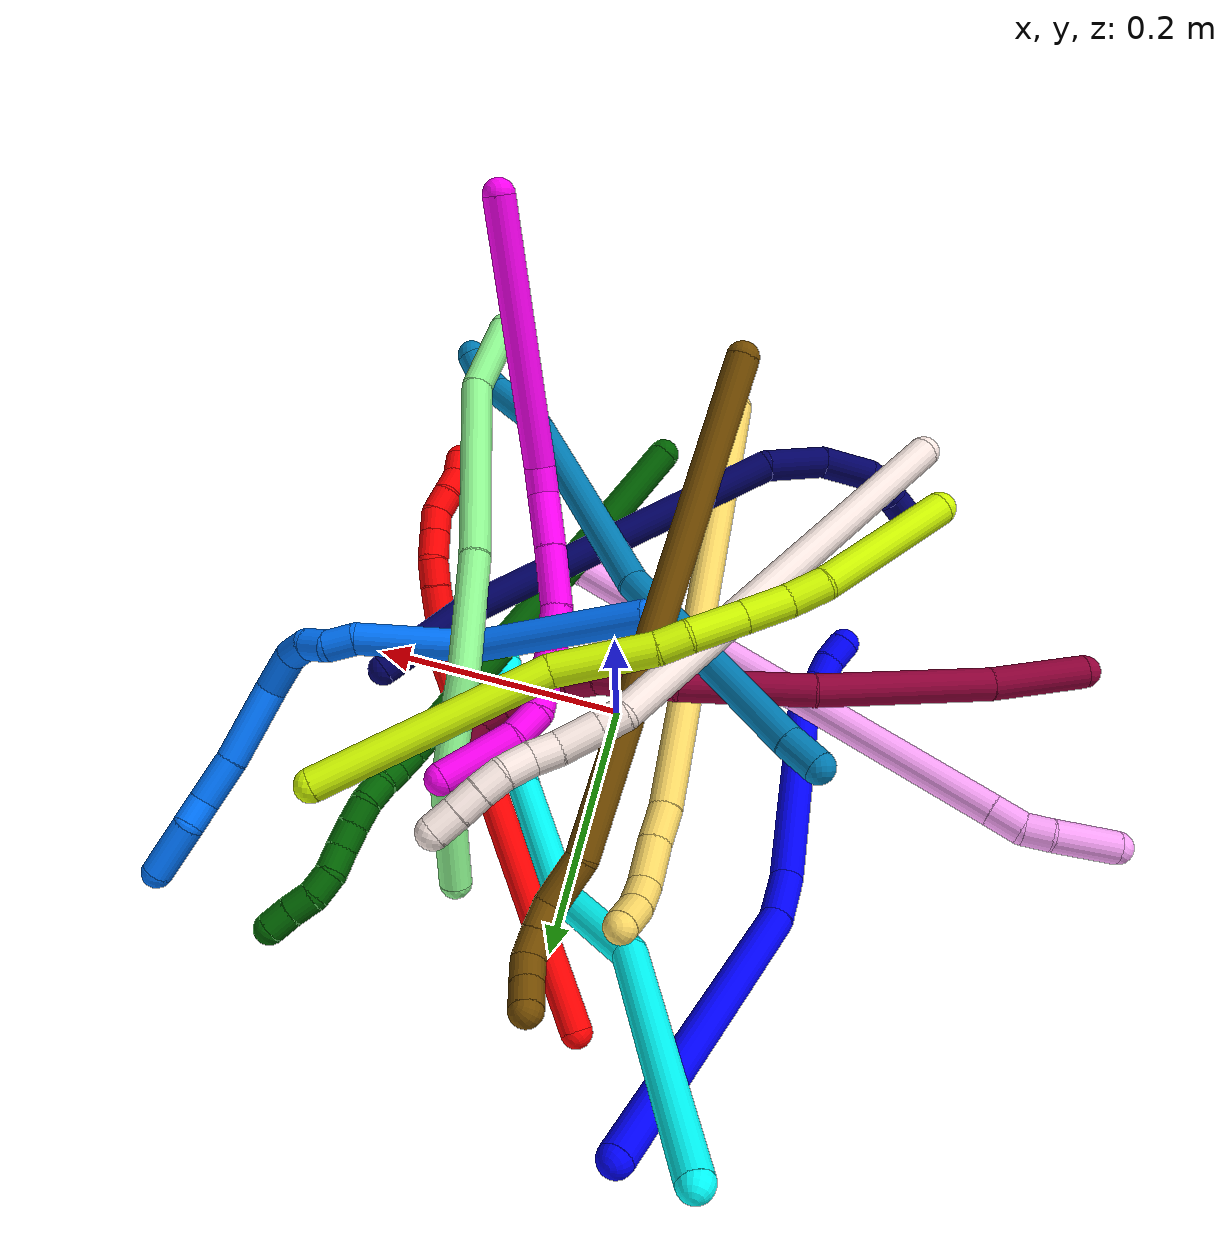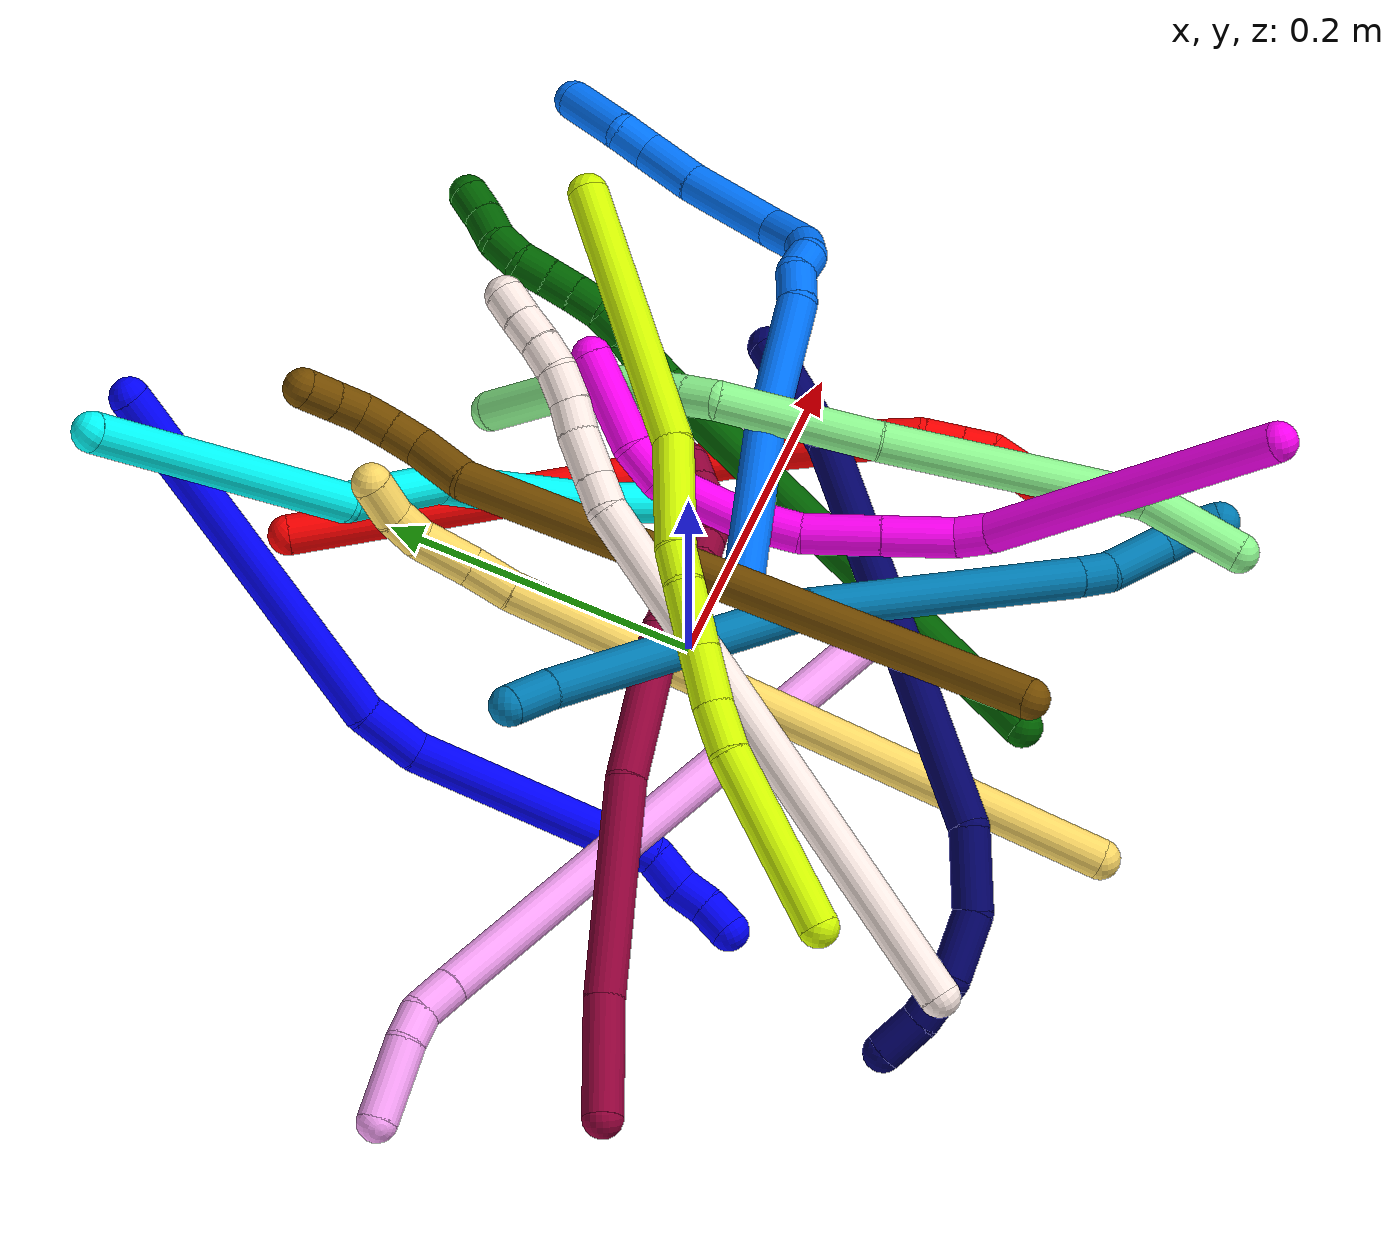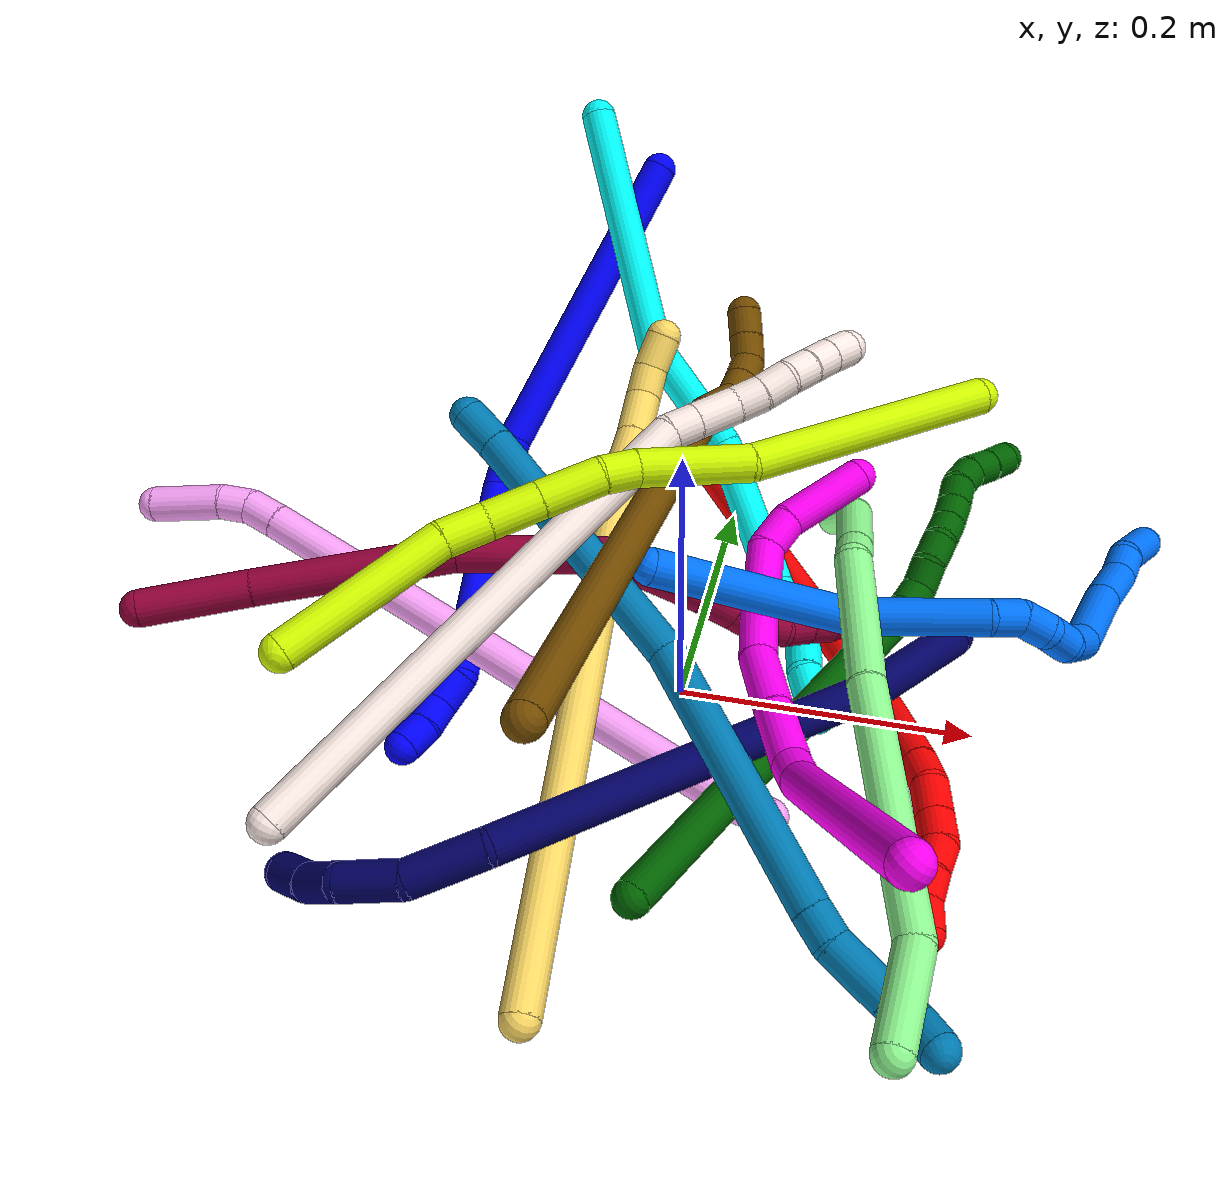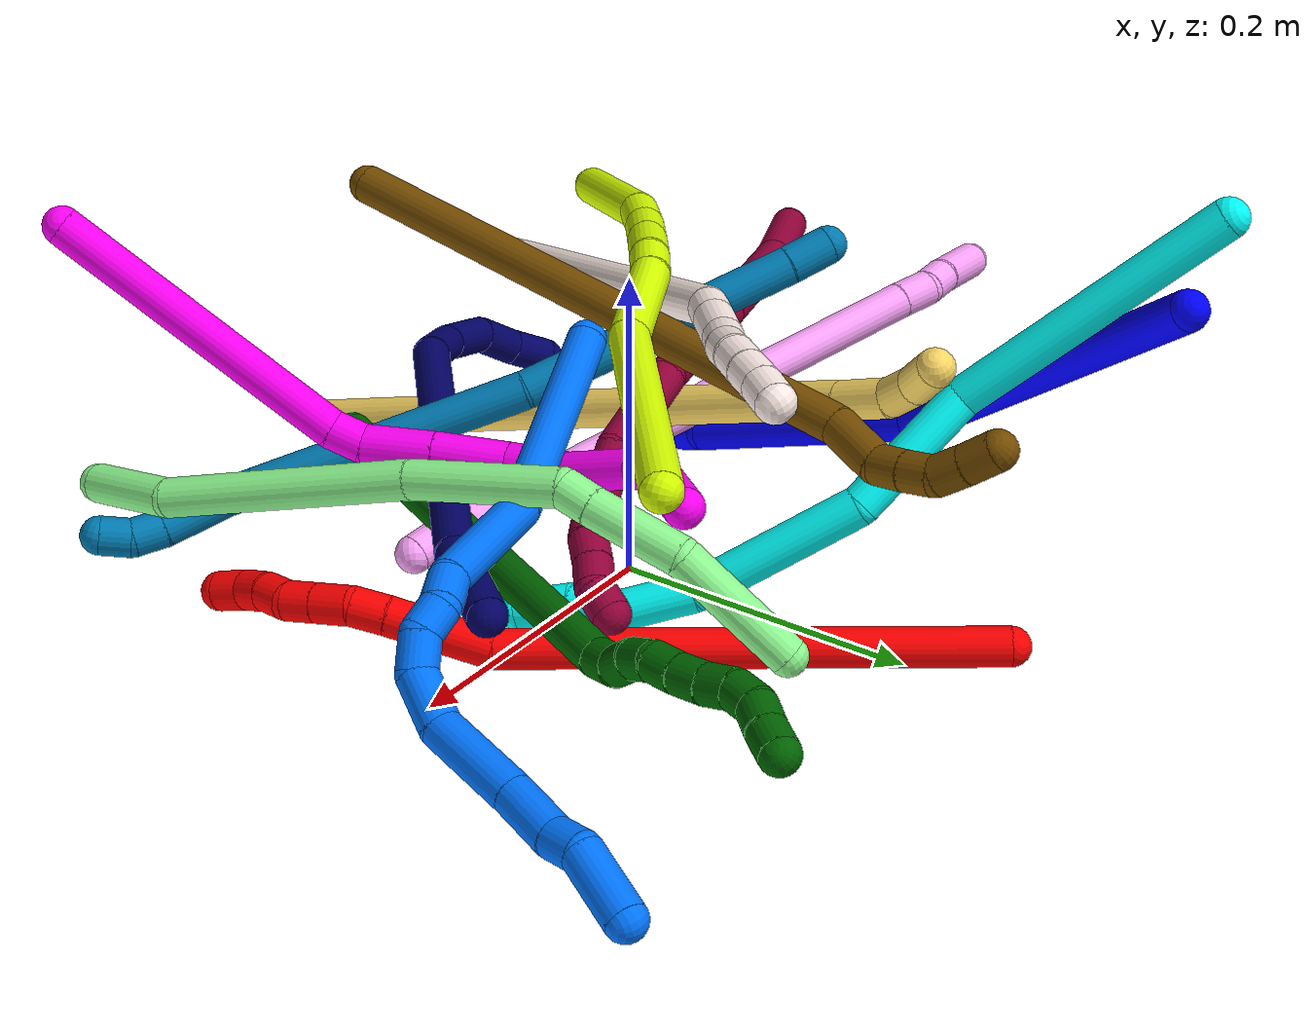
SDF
<sdf version="1.7">
 <world name="default">
  <plugin name="TubeGeneratorPlugin" filename="libtube_generator_plugin.so"/>
  <model name="photoneo_s_sensor">
   <static>1</static>
   <pose>0 0 2 1.57079 1.57079 3.14159</pose>
   <link name="link">
    <inertial><mass>0.1</mass></inertial>
    <sensor name="sensor" type="depth">
     <update_rate>30</update_rate>
     <camera>
      <horizontal_fov>1.22</horizontal_fov>
      <image><width>1920</width><height>1200</height><format>B8G8R8</format></image>
      <clip><near>0.1</near><far>4</far></clip>
      <depth_camera><output>points</output></depth_camera>
     </camera>
     <plugin name="camera_plugin" filename="libgazebo_ros_depth_camera.so">
      <baseline>0.2</baseline>
      <alwaysOn>1</alwaysOn>
      <updateRate>0.0</updateRate>
      <cameraName>camera_ir</cameraName>
      <imageTopicName>/camera/color/image_raw</imageTopicName>
      <cameraInfoTopicName>/camera/color/camera_info</cameraInfoTopicName>
      <depthImageTopicName>/camera/depth/image_raw</depthImageTopicName>
      <depthImageCameraInfoTopicName>/camera/depth/camera_info</depthImageCameraInfoTopicName>
      <pointCloudTopicName>/camera/depth/points</pointCloudTopicName>
      <frameName>fr_optical</frameName>
      <pointCloudCutoff>0.1</pointCloudCutoff>
      <pointCloudCutoffMax>2.0</pointCloudCutoffMax>
      <distortionK1>0</distortionK1>
      <distortionK2>0</distortionK2>
      <distortionK3>0</distortionK3>
      <distortionT1>0</distortionT1>
      <distortionT2>0</distortionT2>
      <CxPrime>0</CxPrime>
      <Cx>0</Cx>
      <Cy>0</Cy>
      <focalLength>0</focalLength>
      <hackBaseline>0</hackBaseline>
     </plugin>
    </sensor>
   </link>
  </model>
  <gravity>0 0 -9.8</gravity>
  <magnetic_field>6e-06 2.3e-05 -4.2e-05</magnetic_field>
  <atmosphere type="adiabatic"/>
  <physics name="default_physics" default="0" type="ode">
   <max_step_size>0.003</max_step_size>
   <real_time_factor>1</real_time_factor>
   <real_time_update_rate>1000</real_time_update_rate>
   <max_contacts>10000</max_contacts>
   <ode>
    <solver>
     <type>quick</type>
     <iters>100</iters>
     <sor>1.3</sor>
     <use_dynamic_moi_rescaling>0</use_dynamic_moi_rescaling>
    </solver>
    <constraints>
     <contact_max_correcting_vel>0</contact_max_correcting_vel>
     <contact_surface_layer>0.001</contact_surface_layer>
     <cfm>0</cfm>
     <erp>0.2</erp>
    </constraints>
   </ode>
  </physics>
  <scene><ambient>0.4 0.4 0.4 1</ambient><background>0.7 0.7 0.7 1</background><shadows>0</shadows></scene>
  <audio><device>default</device></audio>
  <spherical_coordinates>
   <surface_model>EARTH_WGS84</surface_model>
   <latitude_deg>0</latitude_deg>
   <longitude_deg>0</longitude_deg>
   <elevation>0</elevation>
   <heading_deg>0</heading_deg>
  </spherical_coordinates>
  <model name="bin">
   <static>1</static>
   <link name="bottom">
    <collision name="collision-bottom">
     <pose>0 0 -0.01 0 -0 0</pose>
     <geometry><box><size>0.8 0.6 0.02</size></box></geometry>
     <surface>
      <friction><ode><mu>100</mu><mu2>100</mu2></ode></friction>
      <contact><collide_bitmask>65535</collide_bitmask></contact>
     </surface>
    </collision>
   </link>
   <link name="west_wall">
    <collision name="collision-west_wall">
     <pose>-0.41 0 0.1 0 -0 0</pose>
     <geometry><box><size>0.02 0.6 0.2</size></box></geometry>
     <surface>
      <friction><ode><mu>100</mu><mu2>100</mu2></ode></friction>
      <contact><collide_bitmask>65535</collide_bitmask></contact>
     </surface>
    </collision>
   </link>
   <link name="east_wall">
    <collision name="collision-east_wall">
     <pose>0.41 0 0.1 0 -0 0</pose>
     <geometry><box><size>0.02 0.6 0.2</size></box></geometry>
     <surface>
      <friction><ode><mu>100</mu><mu2>100</mu2></ode></friction>
      <contact><collide_bitmask>65535</collide_bitmask></contact>
     </surface>
    </collision>
   </link>
   <link name="south_wall">
    <collision name="collision-south_wall">
     <pose>0 -0.31 0.1 0 -0 0</pose>
     <geometry><box><size>0.8 0.02 0.2</size></box></geometry>
     <surface>
      <friction><ode><mu>100</mu><mu2>100</mu2></ode></friction>
      <contact><collide_bitmask>65535</collide_bitmask></contact>
     </surface>
    </collision>
   </link>
   <link name="north_wall">
    <collision name="collision-north_wall">
     <pose>0 0.31 0.1 0 -0 0</pose>
     <geometry><box><size>0.8 0.02 0.2</size></box></geometry>
     <surface>
      <friction><ode><mu>100</mu><mu2>100</mu2></ode></friction>
      <contact><collide_bitmask>65535</collide_bitmask></contact>
     </surface>
    </collision>
   </link>
  </model>
  <model name="1">
   <static>0</static>
   <link name="1">
    <collision name="collision-cylinder-e_1_1_4">
     <pose>-0.005596 -0.027599 -0.115909 2.90784 -0.046932 -0.394594</pose>
     <geometry><cylinder><radius>0.0125</radius><length>0.238562</length></cylinder></geometry>
     <surface>
      <friction><ode><mu>1.16</mu><mu2>1.16</mu2><slip1>0</slip1><slip2>0</slip2></ode></friction>
      <contact><ode><kp>1e+06</kp><kd>1</kd><max_vel>0</max_vel><min_depth>0.001</min_depth></ode></contact>
     </surface>
    </collision>
    <visual name="visual-cylinder-e_1_1_4">
     <pose>-0.005596 -0.027599 -0.115909 2.90784 -0.046932 -0.394594</pose>
     <geometry><cylinder><radius>0.0125</radius><length>0.238562</length></cylinder></geometry>
     <material><ambient>0 0 1 1</ambient></material>
    </visual>
    <collision name="collision-cylinder-e_2_4_5">
     <pose>-0.009926 -0.064398 -0.249499 2.66175 0.063418 0.257884</pose>
     <geometry><cylinder><radius>0.0125</radius><length>0.039944</length></cylinder></geometry>
     <surface>
      <friction><ode><mu>1.16</mu><mu2>1.16</mu2><slip1>0</slip1><slip2>0</slip2></ode></friction>
      <contact><ode><kp>1e+06</kp><kd>1</kd><max_vel>0</max_vel><min_depth>0.001</min_depth></ode></contact>
     </surface>
    </collision>
    <visual name="visual-cylinder-e_2_4_5">
     <pose>-0.009926 -0.064398 -0.249499 2.66175 0.063418 0.257884</pose>
     <geometry><cylinder><radius>0.0125</radius><length>0.039944</length></cylinder></geometry>
     <material><ambient>0 0 1 1</ambient></material>
    </visual>
    <collision name="collision-cylinder-e_3_5_6">
     <pose>-0.009202 -0.128324 -0.323468 2.37028 -0.006903 -0.017002</pose>
     <geometry><cylinder><radius>0.0125</radius><length>0.157015</length></cylinder></geometry>
     <surface>
      <friction><ode><mu>1.16</mu><mu2>1.16</mu2><slip1>0</slip1><slip2>0</slip2></ode></friction>
      <contact><ode><kp>1e+06</kp><kd>1</kd><max_vel>0</max_vel><min_depth>0.001</min_depth></ode></contact>
     </surface>
    </collision>
    <visual name="visual-cylinder-e_3_5_6">
     <pose>-0.009202 -0.128324 -0.323468 2.37028 -0.006903 -0.017002</pose>
     <geometry><cylinder><radius>0.0125</radius><length>0.157015</length></cylinder></geometry>
     <material><ambient>0 0 1 1</ambient></material>
    </visual>
    <collision name="collision-cylinder-e_4_6_7">
     <pose>-0.012711 -0.187087 -0.390715 2.78848 -0.248746 -1.22241</pose>
     <geometry><cylinder><radius>0.0125</radius><length>0.024099</length></cylinder></geometry>
     <surface>
      <friction><ode><mu>1.16</mu><mu2>1.16</mu2><slip1>0</slip1><slip2>0</slip2></ode></friction>
      <contact><ode><kp>1e+06</kp><kd>1</kd><max_vel>0</max_vel><min_depth>0.001</min_depth></ode></contact>
     </surface>
    </collision>
    <visual name="visual-cylinder-e_4_6_7">
     <pose>-0.012711 -0.187087 -0.390715 2.78848 -0.248746 -1.22241</pose>
     <geometry><cylinder><radius>0.0125</radius><length>0.024099</length></cylinder></geometry>
     <material><ambient>0 0 1 1</ambient></material>
    </visual>
    <collision name="collision-cylinder-e_5_7_8">
     <pose>-0.019027 -0.197235 -0.409031 2.44873 -0.336929 -0.880586</pose>
     <geometry><cylinder><radius>0.0125</radius><length>0.020268</length></cylinder></geometry>
     <surface>
      <friction><ode><mu>1.16</mu><mu2>1.16</mu2><slip1>0</slip1><slip2>0</slip2></ode></friction>
      <contact><ode><kp>1e+06</kp><kd>1</kd><max_vel>0</max_vel><min_depth>0.001</min_depth></ode></contact>
     </surface>
    </collision>
    <visual name="visual-cylinder-e_5_7_8">
     <pose>-0.019027 -0.197235 -0.409031 2.44873 -0.336929 -0.880586</pose>
     <geometry><cylinder><radius>0.0125</radius><length>0.020268</length></cylinder></geometry>
     <material><ambient>0 0 1 1</ambient></material>
    </visual>
    <collision name="collision-cylinder-e_6_8_2">
     <pose>-0.02729 -0.207819 -0.423939 2.60648 -0.510324 -1.52115</pose>
     <geometry><cylinder><radius>0.0125</radius><length>0.020113</length></cylinder></geometry>
     <surface>
      <friction><ode><mu>1.16</mu><mu2>1.16</mu2><slip1>0</slip1><slip2>0</slip2></ode></friction>
      <contact><ode><kp>1e+06</kp><kd>1</kd><max_vel>0</max_vel><min_depth>0.001</min_depth></ode></contact>
     </surface>
    </collision>
    <visual name="visual-cylinder-e_6_8_2">
     <pose>-0.02729 -0.207819 -0.423939 2.60648 -0.510324 -1.52115</pose>
     <geometry><cylinder><radius>0.0125</radius><length>0.020113</length></cylinder></geometry>
     <material><ambient>0 0 1 1</ambient></material>
    </visual>
    <collision name="collision-sphere-2">
     <pose>-0.032202 -0.212293 -0.431487 0 -0 0</pose>
     <geometry><sphere><radius>0.0125</radius></sphere></geometry>
     <surface>
      <friction><ode><mu>1.16</mu><mu2>1.16</mu2><slip1>0</slip1><slip2>0</slip2></ode></friction>
      <contact><ode><kp>1e+06</kp><kd>1</kd><max_vel>0</max_vel><min_depth>0.001</min_depth></ode></contact>
     </surface>
    </collision>
    <visual name="visual-sphere-2">
     <pose>-0.032202 -0.212293 -0.431487 0 -0 0</pose>
     <geometry><sphere><radius>0.0125</radius></sphere></geometry>
     <material><ambient>0 0 1 1</ambient></material>
    </visual>
    <collision name="collision-sphere-4">
     <pose>-0.011192 -0.055197 -0.231819 0 -0 0</pose>
     <geometry><sphere><radius>0.0125</radius></sphere></geometry>
     <surface>
      <friction><ode><mu>1.16</mu><mu2>1.16</mu2><slip1>0</slip1><slip2>0</slip2></ode></friction>
      <contact><ode><kp>1e+06</kp><kd>1</kd><max_vel>0</max_vel><min_depth>0.001</min_depth></ode></contact>
     </surface>
    </collision>
    <visual name="visual-sphere-4">
     <pose>-0.011192 -0.055197 -0.231819 0 -0 0</pose>
     <geometry><sphere><radius>0.0125</radius></sphere></geometry>
     <material><ambient>0 0 1 1</ambient></material>
    </visual>
    <collision name="collision-sphere-1">
     <geometry><sphere><radius>0.0125</radius></sphere></geometry>
     <surface>
      <friction><ode><mu>1.16</mu><mu2>1.16</mu2><slip1>0</slip1><slip2>0</slip2></ode></friction>
      <contact><ode><kp>1e+06</kp><kd>1</kd><max_vel>0</max_vel><min_depth>0.001</min_depth></ode></contact>
     </surface>
    </collision>
    <visual name="visual-sphere-1">
     <geometry><sphere><radius>0.0125</radius></sphere></geometry>
     <material><ambient>0 0 1 1</ambient></material>
    </visual>
    <collision name="collision-sphere-8">
     <pose>-0.022378 -0.203344 -0.41639 0 -0 0</pose>
     <geometry><sphere><radius>0.0125</radius></sphere></geometry>
     <surface>
      <friction><ode><mu>1.16</mu><mu2>1.16</mu2><slip1>0</slip1><slip2>0</slip2></ode></friction>
      <contact><ode><kp>1e+06</kp><kd>1</kd><max_vel>0</max_vel><min_depth>0.001</min_depth></ode></contact>
     </surface>
    </collision>
    <visual name="visual-sphere-8">
     <pose>-0.022378 -0.203344 -0.41639 0 -0 0</pose>
     <geometry><sphere><radius>0.0125</radius></sphere></geometry>
     <material><ambient>0 0 1 1</ambient></material>
    </visual>
    <collision name="collision-sphere-5">
     <pose>-0.008661 -0.0736 -0.26718 0 -0 0</pose>
     <geometry><sphere><radius>0.0125</radius></sphere></geometry>
     <surface>
      <friction><ode><mu>1.16</mu><mu2>1.16</mu2><slip1>0</slip1><slip2>0</slip2></ode></friction>
      <contact><ode><kp>1e+06</kp><kd>1</kd><max_vel>0</max_vel><min_depth>0.001</min_depth></ode></contact>
     </surface>
    </collision>
    <visual name="visual-sphere-5">
     <pose>-0.008661 -0.0736 -0.26718 0 -0 0</pose>
     <geometry><sphere><radius>0.0125</radius></sphere></geometry>
     <material><ambient>0 0 1 1</ambient></material>
    </visual>
    <collision name="collision-sphere-6">
     <pose>-0.009744 -0.183048 -0.379757 0 -0 0</pose>
     <geometry><sphere><radius>0.0125</radius></sphere></geometry>
     <surface>
      <friction><ode><mu>1.16</mu><mu2>1.16</mu2><slip1>0</slip1><slip2>0</slip2></ode></friction>
      <contact><ode><kp>1e+06</kp><kd>1</kd><max_vel>0</max_vel><min_depth>0.001</min_depth></ode></contact>
     </surface>
    </collision>
    <visual name="visual-sphere-6">
     <pose>-0.009744 -0.183048 -0.379757 0 -0 0</pose>
     <geometry><sphere><radius>0.0125</radius></sphere></geometry>
     <material><ambient>0 0 1 1</ambient></material>
    </visual>
    <collision name="collision-sphere-7">
     <pose>-0.015677 -0.191126 -0.401672 0 -0 0</pose>
     <geometry><sphere><radius>0.0125</radius></sphere></geometry>
     <surface>
      <friction><ode><mu>1.16</mu><mu2>1.16</mu2><slip1>0</slip1><slip2>0</slip2></ode></friction>
      <contact><ode><kp>1e+06</kp><kd>1</kd><max_vel>0</max_vel><min_depth>0.001</min_depth></ode></contact>
     </surface>
    </collision>
    <visual name="visual-sphere-7">
     <pose>-0.015677 -0.191126 -0.401672 0 -0 0</pose>
     <geometry><sphere><radius>0.0125</radius></sphere></geometry>
     <material><ambient>0 0 1 1</ambient></material>
    </visual>
    <inertial>
     <pose>-0.008834 -0.083982 -0.229279 0 -0 0</pose>
     <mass>0.5</mass>
     <inertia>
      <ixx>0.00094</ixx>
      <ixy>0</ixy>
      <ixz>0</ixz>
      <iyy>-0.001725</iyy>
      <iyz>0</iyz>
      <izz>0.000522</izz>
     </inertia>
    </inertial>
   </link>
   <pose>-0.086959 0.32077 0.230772 -0.417349 0.681276 0.352336</pose>
  </model>
  <model name="2">
   <static>0</static>
   <link name="2">
    <collision name="collision-cylinder-e_1_1_4">
     <pose>0.049771 -0.120198 -0.082406 2.17178 0.329097 0.610627</pose>
     <geometry><cylinder><radius>0.0125</radius><length>0.307997</length></cylinder></geometry>
     <surface>
      <friction><ode><mu>1.16</mu><mu2>1.16</mu2><slip1>0</slip1><slip2>0</slip2></ode></friction>
      <contact><ode><kp>1e+06</kp><kd>1</kd><max_vel>0</max_vel><min_depth>0.001</min_depth></ode></contact>
     </surface>
    </collision>
    <visual name="visual-cylinder-e_1_1_4">
     <pose>0.049771 -0.120198 -0.082406 2.17178 0.329097 0.610627</pose>
     <geometry><cylinder><radius>0.0125</radius><length>0.307997</length></cylinder></geometry>
     <material><ambient>1 0 0 1</ambient></material>
    </visual>
    <collision name="collision-cylinder-e_2_4_5">
     <pose>0.100787 -0.269382 -0.180263 2.06053 0.03791 0.063153</pose>
     <geometry><cylinder><radius>0.0125</radius><length>0.065739</length></cylinder></geometry>
     <surface>
      <friction><ode><mu>1.16</mu><mu2>1.16</mu2><slip1>0</slip1><slip2>0</slip2></ode></friction>
      <contact><ode><kp>1e+06</kp><kd>1</kd><max_vel>0</max_vel><min_depth>0.001</min_depth></ode></contact>
     </surface>
    </collision>
    <visual name="visual-cylinder-e_2_4_5">
     <pose>0.100787 -0.269382 -0.180263 2.06053 0.03791 0.063153</pose>
     <geometry><cylinder><radius>0.0125</radius><length>0.065739</length></cylinder></geometry>
     <material><ambient>1 0 0 1</ambient></material>
    </visual>
    <collision name="collision-cylinder-e_3_5_6">
     <pose>0.10247 -0.307739 -0.201701 2.13935 0.039279 0.071686</pose>
     <geometry><cylinder><radius>0.0125</radius><length>0.02226</length></cylinder></geometry>
     <surface>
      <friction><ode><mu>1.16</mu><mu2>1.16</mu2><slip1>0</slip1><slip2>0</slip2></ode></friction>
      <contact><ode><kp>1e+06</kp><kd>1</kd><max_vel>0</max_vel><min_depth>0.001</min_depth></ode></contact>
     </surface>
    </collision>
    <visual name="visual-cylinder-e_3_5_6">
     <pose>0.10247 -0.307739 -0.201701 2.13935 0.039279 0.071686</pose>
     <geometry><cylinder><radius>0.0125</radius><length>0.02226</length></cylinder></geometry>
     <material><ambient>1 0 0 1</ambient></material>
    </visual>
    <collision name="collision-cylinder-e_4_6_7">
     <pose>0.103639 -0.324666 -0.216952 2.45736 0.061177 0.171421</pose>
     <geometry><cylinder><radius>0.0125</radius><length>0.023952</length></cylinder></geometry>
     <surface>
      <friction><ode><mu>1.16</mu><mu2>1.16</mu2><slip1>0</slip1><slip2>0</slip2></ode></friction>
      <contact><ode><kp>1e+06</kp><kd>1</kd><max_vel>0</max_vel><min_depth>0.001</min_depth></ode></contact>
     </surface>
    </collision>
    <visual name="visual-cylinder-e_4_6_7">
     <pose>0.103639 -0.324666 -0.216952 2.45736 0.061177 0.171421</pose>
     <geometry><cylinder><radius>0.0125</radius><length>0.023952</length></cylinder></geometry>
     <material><ambient>1 0 0 1</ambient></material>
    </visual>
    <collision name="collision-cylinder-e_5_7_8">
     <pose>0.105009 -0.338509 -0.233966 2.46016 0.063813 0.179564</pose>
     <geometry><cylinder><radius>0.0125</radius><length>0.020001</length></cylinder></geometry>
     <surface>
      <friction><ode><mu>1.16</mu><mu2>1.16</mu2><slip1>0</slip1><slip2>0</slip2></ode></friction>
      <contact><ode><kp>1e+06</kp><kd>1</kd><max_vel>0</max_vel><min_depth>0.001</min_depth></ode></contact>
     </surface>
    </collision>
    <visual name="visual-cylinder-e_5_7_8">
     <pose>0.105009 -0.338509 -0.233966 2.46016 0.063813 0.179564</pose>
     <geometry><cylinder><radius>0.0125</radius><length>0.020001</length></cylinder></geometry>
     <material><ambient>1 0 0 1</ambient></material>
    </visual>
    <collision name="collision-cylinder-e_6_8_9">
     <pose>0.102604 -0.349234 -0.250149 2.65698 -0.309044 -1.12468</pose>
     <geometry><cylinder><radius>0.0125</radius><length>0.020004</length></cylinder></geometry>
     <surface>
      <friction><ode><mu>1.16</mu><mu2>1.16</mu2><slip1>0</slip1><slip2>0</slip2></ode></friction>
      <contact><ode><kp>1e+06</kp><kd>1</kd><max_vel>0</max_vel><min_depth>0.001</min_depth></ode></contact>
     </surface>
    </collision>
    <visual name="visual-cylinder-e_6_8_9">
     <pose>0.102604 -0.349234 -0.250149 2.65698 -0.309044 -1.12468</pose>
     <geometry><cylinder><radius>0.0125</radius><length>0.020004</length></cylinder></geometry>
     <material><ambient>1 0 0 1</ambient></material>
    </visual>
    <collision name="collision-cylinder-e_7_9_10">
     <pose>0.097997 -0.357035 -0.26789 2.79504 -0.156853 -0.844038</pose>
     <geometry><cylinder><radius>0.0125</radius><length>0.020042</length></cylinder></geometry>
     <surface>
      <friction><ode><mu>1.16</mu><mu2>1.16</mu2><slip1>0</slip1><slip2>0</slip2></ode></friction>
      <contact><ode><kp>1e+06</kp><kd>1</kd><max_vel>0</max_vel><min_depth>0.001</min_depth></ode></contact>
     </surface>
    </collision>
    <visual name="visual-cylinder-e_7_9_10">
     <pose>0.097997 -0.357035 -0.26789 2.79504 -0.156853 -0.844038</pose>
     <geometry><cylinder><radius>0.0125</radius><length>0.020042</length></cylinder></geometry>
     <material><ambient>1 0 0 1</ambient></material>
    </visual>
    <collision name="collision-cylinder-e_8_10_2">
     <pose>0.097232 -0.365342 -0.285856 2.62257 0.08009 0.299561</pose>
     <geometry><cylinder><radius>0.0125</radius><length>0.020004</length></cylinder></geometry>
     <surface>
      <friction><ode><mu>1.16</mu><mu2>1.16</mu2><slip1>0</slip1><slip2>0</slip2></ode></friction>
      <contact><ode><kp>1e+06</kp><kd>1</kd><max_vel>0</max_vel><min_depth>0.001</min_depth></ode></contact>
     </surface>
    </collision>
    <visual name="visual-cylinder-e_8_10_2">
     <pose>0.097232 -0.365342 -0.285856 2.62257 0.08009 0.299561</pose>
     <geometry><cylinder><radius>0.0125</radius><length>0.020004</length></cylinder></geometry>
     <material><ambient>1 0 0 1</ambient></material>
    </visual>
    <collision name="collision-sphere-2">
     <pose>0.098032 -0.370288 -0.294513 0 -0 0</pose>
     <geometry><sphere><radius>0.0125</radius></sphere></geometry>
     <surface>
      <friction><ode><mu>1.16</mu><mu2>1.16</mu2><slip1>0</slip1><slip2>0</slip2></ode></friction>
      <contact><ode><kp>1e+06</kp><kd>1</kd><max_vel>0</max_vel><min_depth>0.001</min_depth></ode></contact>
     </surface>
    </collision>
    <visual name="visual-sphere-2">
     <pose>0.098032 -0.370288 -0.294513 0 -0 0</pose>
     <geometry><sphere><radius>0.0125</radius></sphere></geometry>
     <material><ambient>1 0 0 1</ambient></material>
    </visual>
    <collision name="collision-sphere-10">
     <pose>0.096431 -0.360397 -0.2772 0 -0 0</pose>
     <geometry><sphere><radius>0.0125</radius></sphere></geometry>
     <surface>
      <friction><ode><mu>1.16</mu><mu2>1.16</mu2><slip1>0</slip1><slip2>0</slip2></ode></friction>
      <contact><ode><kp>1e+06</kp><kd>1</kd><max_vel>0</max_vel><min_depth>0.001</min_depth></ode></contact>
     </surface>
    </collision>
    <visual name="visual-sphere-10">
     <pose>0.096431 -0.360397 -0.2772 0 -0 0</pose>
     <geometry><sphere><radius>0.0125</radius></sphere></geometry>
     <material><ambient>1 0 0 1</ambient></material>
    </visual>
    <collision name="collision-sphere-9">
     <pose>0.099562 -0.353673 -0.25858 0 -0 0</pose>
     <geometry><sphere><radius>0.0125</radius></sphere></geometry>
     <surface>
      <friction><ode><mu>1.16</mu><mu2>1.16</mu2><slip1>0</slip1><slip2>0</slip2></ode></friction>
      <contact><ode><kp>1e+06</kp><kd>1</kd><max_vel>0</max_vel><min_depth>0.001</min_depth></ode></contact>
     </surface>
    </collision>
    <visual name="visual-sphere-9">
     <pose>0.099562 -0.353673 -0.25858 0 -0 0</pose>
     <geometry><sphere><radius>0.0125</radius></sphere></geometry>
     <material><ambient>1 0 0 1</ambient></material>
    </visual>
    <collision name="collision-sphere-4">
     <pose>0.099541 -0.240397 -0.164812 0 -0 0</pose>
     <geometry><sphere><radius>0.0125</radius></sphere></geometry>
     <surface>
      <friction><ode><mu>1.16</mu><mu2>1.16</mu2><slip1>0</slip1><slip2>0</slip2></ode></friction>
      <contact><ode><kp>1e+06</kp><kd>1</kd><max_vel>0</max_vel><min_depth>0.001</min_depth></ode></contact>
     </surface>
    </collision>
    <visual name="visual-sphere-4">
     <pose>0.099541 -0.240397 -0.164812 0 -0 0</pose>
     <geometry><sphere><radius>0.0125</radius></sphere></geometry>
     <material><ambient>1 0 0 1</ambient></material>
    </visual>
    <collision name="collision-sphere-1">
     <geometry><sphere><radius>0.0125</radius></sphere></geometry>
     <surface>
      <friction><ode><mu>1.16</mu><mu2>1.16</mu2><slip1>0</slip1><slip2>0</slip2></ode></friction>
      <contact><ode><kp>1e+06</kp><kd>1</kd><max_vel>0</max_vel><min_depth>0.001</min_depth></ode></contact>
     </surface>
    </collision>
    <visual name="visual-sphere-1">
     <geometry><sphere><radius>0.0125</radius></sphere></geometry>
     <material><ambient>1 0 0 1</ambient></material>
    </visual>
    <collision name="collision-sphere-8">
     <pose>0.105647 -0.344795 -0.241718 0 -0 0</pose>
     <geometry><sphere><radius>0.0125</radius></sphere></geometry>
     <surface>
      <friction><ode><mu>1.16</mu><mu2>1.16</mu2><slip1>0</slip1><slip2>0</slip2></ode></friction>
      <contact><ode><kp>1e+06</kp><kd>1</kd><max_vel>0</max_vel><min_depth>0.001</min_depth></ode></contact>
     </surface>
    </collision>
    <visual name="visual-sphere-8">
     <pose>0.105647 -0.344795 -0.241718 0 -0 0</pose>
     <geometry><sphere><radius>0.0125</radius></sphere></geometry>
     <material><ambient>1 0 0 1</ambient></material>
    </visual>
    <collision name="collision-sphere-5">
     <pose>0.102033 -0.298367 -0.195713 0 -0 0</pose>
     <geometry><sphere><radius>0.0125</radius></sphere></geometry>
     <surface>
      <friction><ode><mu>1.16</mu><mu2>1.16</mu2><slip1>0</slip1><slip2>0</slip2></ode></friction>
      <contact><ode><kp>1e+06</kp><kd>1</kd><max_vel>0</max_vel><min_depth>0.001</min_depth></ode></contact>
     </surface>
    </collision>
    <visual name="visual-sphere-5">
     <pose>0.102033 -0.298367 -0.195713 0 -0 0</pose>
     <geometry><sphere><radius>0.0125</radius></sphere></geometry>
     <material><ambient>1 0 0 1</ambient></material>
    </visual>
    <collision name="collision-sphere-6">
     <pose>0.102907 -0.317111 -0.207689 0 -0 0</pose>
     <geometry><sphere><radius>0.0125</radius></sphere></geometry>
     <surface>
      <friction><ode><mu>1.16</mu><mu2>1.16</mu2><slip1>0</slip1><slip2>0</slip2></ode></friction>
      <contact><ode><kp>1e+06</kp><kd>1</kd><max_vel>0</max_vel><min_depth>0.001</min_depth></ode></contact>
     </surface>
    </collision>
    <visual name="visual-sphere-6">
     <pose>0.102907 -0.317111 -0.207689 0 -0 0</pose>
     <geometry><sphere><radius>0.0125</radius></sphere></geometry>
     <material><ambient>1 0 0 1</ambient></material>
    </visual>
    <collision name="collision-sphere-7">
     <pose>0.104371 -0.332222 -0.226215 0 -0 0</pose>
     <geometry><sphere><radius>0.0125</radius></sphere></geometry>
     <surface>
      <friction><ode><mu>1.16</mu><mu2>1.16</mu2><slip1>0</slip1><slip2>0</slip2></ode></friction>
      <contact><ode><kp>1e+06</kp><kd>1</kd><max_vel>0</max_vel><min_depth>0.001</min_depth></ode></contact>
     </surface>
    </collision>
    <visual name="visual-sphere-7">
     <pose>0.104371 -0.332222 -0.226215 0 -0 0</pose>
     <geometry><sphere><radius>0.0125</radius></sphere></geometry>
     <material><ambient>1 0 0 1</ambient></material>
    </visual>
    <inertial>
     <pose>0.06956 -0.195154 -0.135377 0 -0 0</pose>
     <mass>0.5</mass>
     <inertia>
      <ixx>0.003267</ixx>
      <ixy>0</ixy>
      <ixz>0</ixz>
      <iyy>0.000521</iyy>
      <iyz>0</iyz>
      <izz>0.001124</izz>
     </inertia>
    </inertial>
   </link>
   <pose>-0.036448 0.25226 0.013014 -0.780236 0.49466 0.244346</pose>
  </model>
  <model name="3">
   <static>0</static>
   <link name="3">
    <collision name="collision-cylinder-e_1_1_4">
     <pose>0.033941 -0.014342 -0.085465 2.97533 0.373292 2.31055</pose>
     <geometry><cylinder><radius>0.0125</radius><length>0.18614</length></cylinder></geometry>
     <surface>
      <friction><ode><mu>1.16</mu><mu2>1.16</mu2><slip1>0</slip1><slip2>0</slip2></ode></friction>
      <contact><ode><kp>1e+06</kp><kd>1</kd><max_vel>0</max_vel><min_depth>0.001</min_depth></ode></contact>
     </surface>
    </collision>
    <visual name="visual-cylinder-e_1_1_4">
     <pose>0.033941 -0.014342 -0.085465 2.97533 0.373292 2.31055</pose>
     <geometry><cylinder><radius>0.0125</radius><length>0.18614</length></cylinder></geometry>
     <material><ambient>0.003922 1 0.996078 1</ambient></material>
    </visual>
    <collision name="collision-cylinder-e_2_4_5">
     <pose>0.097947 -0.040353 -0.200239 2.76267 0.761369 2.24792</pose>
     <geometry><cylinder><radius>0.0125</radius><length>0.087157</length></cylinder></geometry>
     <surface>
      <friction><ode><mu>1.16</mu><mu2>1.16</mu2><slip1>0</slip1><slip2>0</slip2></ode></friction>
      <contact><ode><kp>1e+06</kp><kd>1</kd><max_vel>0</max_vel><min_depth>0.001</min_depth></ode></contact>
     </surface>
    </collision>
    <visual name="visual-cylinder-e_2_4_5">
     <pose>0.097947 -0.040353 -0.200239 2.76267 0.761369 2.24792</pose>
     <geometry><cylinder><radius>0.0125</radius><length>0.087157</length></cylinder></geometry>
     <material><ambient>0.003922 1 0.996078 1</ambient></material>
    </visual>
    <collision name="collision-cylinder-e_3_5_6">
     <pose>0.147623 -0.069289 -0.279862 2.81101 0.353191 1.63821</pose>
     <geometry><cylinder><radius>0.0125</radius><length>0.113388</length></cylinder></geometry>
     <surface>
      <friction><ode><mu>1.16</mu><mu2>1.16</mu2><slip1>0</slip1><slip2>0</slip2></ode></friction>
      <contact><ode><kp>1e+06</kp><kd>1</kd><max_vel>0</max_vel><min_depth>0.001</min_depth></ode></contact>
     </surface>
    </collision>
    <visual name="visual-cylinder-e_3_5_6">
     <pose>0.147623 -0.069289 -0.279862 2.81101 0.353191 1.63821</pose>
     <geometry><cylinder><radius>0.0125</radius><length>0.113388</length></cylinder></geometry>
     <material><ambient>0.003922 1 0.996078 1</ambient></material>
    </visual>
    <collision name="collision-cylinder-e_4_6_7">
     <pose>0.17195 -0.099192 -0.351433 2.60526 0.188507 0.662686</pose>
     <geometry><cylinder><radius>0.0125</radius><length>0.050349</length></cylinder></geometry>
     <surface>
      <friction><ode><mu>1.16</mu><mu2>1.16</mu2><slip1>0</slip1><slip2>0</slip2></ode></friction>
      <contact><ode><kp>1e+06</kp><kd>1</kd><max_vel>0</max_vel><min_depth>0.001</min_depth></ode></contact>
     </surface>
    </collision>
    <visual name="visual-cylinder-e_4_6_7">
     <pose>0.17195 -0.099192 -0.351433 2.60526 0.188507 0.662686</pose>
     <geometry><cylinder><radius>0.0125</radius><length>0.050349</length></cylinder></geometry>
     <material><ambient>0.003922 1 0.996078 1</ambient></material>
    </visual>
    <collision name="collision-cylinder-e_5_7_8">
     <pose>0.172896 -0.118671 -0.384638 2.62149 -0.267366 -0.935974</pose>
     <geometry><cylinder><radius>0.0125</radius><length>0.028554</length></cylinder></geometry>
     <surface>
      <friction><ode><mu>1.16</mu><mu2>1.16</mu2><slip1>0</slip1><slip2>0</slip2></ode></friction>
      <contact><ode><kp>1e+06</kp><kd>1</kd><max_vel>0</max_vel><min_depth>0.001</min_depth></ode></contact>
     </surface>
    </collision>
    <visual name="visual-cylinder-e_5_7_8">
     <pose>0.172896 -0.118671 -0.384638 2.62149 -0.267366 -0.935974</pose>
     <geometry><cylinder><radius>0.0125</radius><length>0.028554</length></cylinder></geometry>
     <material><ambient>0.003922 1 0.996078 1</ambient></material>
    </visual>
    <collision name="collision-cylinder-e_6_8_2">
     <pose>0.16994 -0.133498 -0.411806 2.65847 0.047406 0.191862</pose>
     <geometry><cylinder><radius>0.0125</radius><length>0.034412</length></cylinder></geometry>
     <surface>
      <friction><ode><mu>1.16</mu><mu2>1.16</mu2><slip1>0</slip1><slip2>0</slip2></ode></friction>
      <contact><ode><kp>1e+06</kp><kd>1</kd><max_vel>0</max_vel><min_depth>0.001</min_depth></ode></contact>
     </surface>
    </collision>
    <visual name="visual-cylinder-e_6_8_2">
     <pose>0.16994 -0.133498 -0.411806 2.65847 0.047406 0.191862</pose>
     <geometry><cylinder><radius>0.0125</radius><length>0.034412</length></cylinder></geometry>
     <material><ambient>0.003922 1 0.996078 1</ambient></material>
    </visual>
    <collision name="collision-sphere-2">
     <pose>0.170755 -0.141482 -0.427026 0 -0 0</pose>
     <geometry><sphere><radius>0.0125</radius></sphere></geometry>
     <surface>
      <friction><ode><mu>1.16</mu><mu2>1.16</mu2><slip1>0</slip1><slip2>0</slip2></ode></friction>
      <contact><ode><kp>1e+06</kp><kd>1</kd><max_vel>0</max_vel><min_depth>0.001</min_depth></ode></contact>
     </surface>
    </collision>
    <visual name="visual-sphere-2">
     <pose>0.170755 -0.141482 -0.427026 0 -0 0</pose>
     <geometry><sphere><radius>0.0125</radius></sphere></geometry>
     <material><ambient>0.003922 1 0.996078 1</ambient></material>
    </visual>
    <collision name="collision-sphere-4">
     <pose>0.067882 -0.028683 -0.170931 0 -0 0</pose>
     <geometry><sphere><radius>0.0125</radius></sphere></geometry>
     <surface>
      <friction><ode><mu>1.16</mu><mu2>1.16</mu2><slip1>0</slip1><slip2>0</slip2></ode></friction>
      <contact><ode><kp>1e+06</kp><kd>1</kd><max_vel>0</max_vel><min_depth>0.001</min_depth></ode></contact>
     </surface>
    </collision>
    <visual name="visual-sphere-4">
     <pose>0.067882 -0.028683 -0.170931 0 -0 0</pose>
     <geometry><sphere><radius>0.0125</radius></sphere></geometry>
     <material><ambient>0.003922 1 0.996078 1</ambient></material>
    </visual>
    <collision name="collision-sphere-1">
     <geometry><sphere><radius>0.0125</radius></sphere></geometry>
     <surface>
      <friction><ode><mu>1.16</mu><mu2>1.16</mu2><slip1>0</slip1><slip2>0</slip2></ode></friction>
      <contact><ode><kp>1e+06</kp><kd>1</kd><max_vel>0</max_vel><min_depth>0.001</min_depth></ode></contact>
     </surface>
    </collision>
    <visual name="visual-sphere-1">
     <geometry><sphere><radius>0.0125</radius></sphere></geometry>
     <material><ambient>0.003922 1 0.996078 1</ambient></material>
    </visual>
    <collision name="collision-sphere-8">
     <pose>0.169124 -0.125514 -0.396587 0 -0 0</pose>
     <geometry><sphere><radius>0.0125</radius></sphere></geometry>
     <surface>
      <friction><ode><mu>1.16</mu><mu2>1.16</mu2><slip1>0</slip1><slip2>0</slip2></ode></friction>
      <contact><ode><kp>1e+06</kp><kd>1</kd><max_vel>0</max_vel><min_depth>0.001</min_depth></ode></contact>
     </surface>
    </collision>
    <visual name="visual-sphere-8">
     <pose>0.169124 -0.125514 -0.396587 0 -0 0</pose>
     <geometry><sphere><radius>0.0125</radius></sphere></geometry>
     <material><ambient>0.003922 1 0.996078 1</ambient></material>
    </visual>
    <collision name="collision-sphere-5">
     <pose>0.128012 -0.052022 -0.229547 0 -0 0</pose>
     <geometry><sphere><radius>0.0125</radius></sphere></geometry>
     <surface>
      <friction><ode><mu>1.16</mu><mu2>1.16</mu2><slip1>0</slip1><slip2>0</slip2></ode></friction>
      <contact><ode><kp>1e+06</kp><kd>1</kd><max_vel>0</max_vel><min_depth>0.001</min_depth></ode></contact>
     </surface>
    </collision>
    <visual name="visual-sphere-5">
     <pose>0.128012 -0.052022 -0.229547 0 -0 0</pose>
     <geometry><sphere><radius>0.0125</radius></sphere></geometry>
     <material><ambient>0.003922 1 0.996078 1</ambient></material>
    </visual>
    <collision name="collision-sphere-6">
     <pose>0.167233 -0.086556 -0.330176 0 -0 0</pose>
     <geometry><sphere><radius>0.0125</radius></sphere></geometry>
     <surface>
      <friction><ode><mu>1.16</mu><mu2>1.16</mu2><slip1>0</slip1><slip2>0</slip2></ode></friction>
      <contact><ode><kp>1e+06</kp><kd>1</kd><max_vel>0</max_vel><min_depth>0.001</min_depth></ode></contact>
     </surface>
    </collision>
    <visual name="visual-sphere-6">
     <pose>0.167233 -0.086556 -0.330176 0 -0 0</pose>
     <geometry><sphere><radius>0.0125</radius></sphere></geometry>
     <material><ambient>0.003922 1 0.996078 1</ambient></material>
    </visual>
    <collision name="collision-sphere-7">
     <pose>0.176668 -0.111828 -0.372689 0 -0 0</pose>
     <geometry><sphere><radius>0.0125</radius></sphere></geometry>
     <surface>
      <friction><ode><mu>1.16</mu><mu2>1.16</mu2><slip1>0</slip1><slip2>0</slip2></ode></friction>
      <contact><ode><kp>1e+06</kp><kd>1</kd><max_vel>0</max_vel><min_depth>0.001</min_depth></ode></contact>
     </surface>
    </collision>
    <visual name="visual-sphere-7">
     <pose>0.176668 -0.111828 -0.372689 0 -0 0</pose>
     <geometry><sphere><radius>0.0125</radius></sphere></geometry>
     <material><ambient>0.003922 1 0.996078 1</ambient></material>
    </visual>
    <inertial>
     <pose>0.102071 -0.05404 -0.215884 0 -0 0</pose>
     <mass>0.5</mass>
     <inertia>
      <ixx>0.000185</ixx>
      <ixy>0</ixy>
      <ixz>0</ixz>
      <iyy>0.000962</iyy>
      <iyz>0</iyz>
      <izz>-0.00017</izz>
     </inertia>
    </inertial>
   </link>
   <pose>-0.133542 0.31966 0.270418 -0.80203 0.66205 0.56889</pose>
  </model>
  <model name="4">
   <static>0</static>
   <link name="4">
    <collision name="collision-cylinder-e_1_1_4">
     <pose>-0.010393 -0.003518 0.007599 0.433533 -0.892576 -0.209976</pose>
     <geometry><cylinder><radius>0.0125</radius><length>0.026695</length></cylinder></geometry>
     <surface>
      <friction><ode><mu>1.16</mu><mu2>1.16</mu2><slip1>0</slip1><slip2>0</slip2></ode></friction>
      <contact><ode><kp>1e+06</kp><kd>1</kd><max_vel>0</max_vel><min_depth>0.001</min_depth></ode></contact>
     </surface>
    </collision>
    <visual name="visual-cylinder-e_1_1_4">
     <pose>-0.010393 -0.003518 0.007599 0.433533 -0.892576 -0.209976</pose>
     <geometry><cylinder><radius>0.0125</radius><length>0.026695</length></cylinder></geometry>
     <material><ambient>1 0.65098 0.996078 1</ambient></material>
    </visual>
    <collision name="collision-cylinder-e_2_4_5">
     <pose>-0.185767 -0.036052 0.1007 0.327178 -1.07004 -0.19504</pose>
     <geometry><cylinder><radius>0.0125</radius><length>0.376142</length></cylinder></geometry>
     <surface>
      <friction><ode><mu>1.16</mu><mu2>1.16</mu2><slip1>0</slip1><slip2>0</slip2></ode></friction>
      <contact><ode><kp>1e+06</kp><kd>1</kd><max_vel>0</max_vel><min_depth>0.001</min_depth></ode></contact>
     </surface>
    </collision>
    <visual name="visual-cylinder-e_2_4_5">
     <pose>-0.185767 -0.036052 0.1007 0.327178 -1.07004 -0.19504</pose>
     <geometry><cylinder><radius>0.0125</radius><length>0.376142</length></cylinder></geometry>
     <material><ambient>1 0.65098 0.996078 1</ambient></material>
    </visual>
    <collision name="collision-cylinder-e_3_5_6">
     <pose>-0.36195 -0.06746 0.191699 0.410139 -1.07941 -0.247911</pose>
     <geometry><cylinder><radius>0.0125</radius><length>0.025415</length></cylinder></geometry>
     <surface>
      <friction><ode><mu>1.16</mu><mu2>1.16</mu2><slip1>0</slip1><slip2>0</slip2></ode></friction>
      <contact><ode><kp>1e+06</kp><kd>1</kd><max_vel>0</max_vel><min_depth>0.001</min_depth></ode></contact>
     </surface>
    </collision>
    <visual name="visual-cylinder-e_3_5_6">
     <pose>-0.36195 -0.06746 0.191699 0.410139 -1.07941 -0.247911</pose>
     <geometry><cylinder><radius>0.0125</radius><length>0.025415</length></cylinder></geometry>
     <material><ambient>1 0.65098 0.996078 1</ambient></material>
    </visual>
    <collision name="collision-cylinder-e_4_6_7">
     <pose>-0.380272 -0.07461 0.203436 0.651674 -0.736782 -0.259388</pose>
     <geometry><cylinder><radius>0.0125</radius><length>0.021188</length></cylinder></geometry>
     <surface>
      <friction><ode><mu>1.16</mu><mu2>1.16</mu2><slip1>0</slip1><slip2>0</slip2></ode></friction>
      <contact><ode><kp>1e+06</kp><kd>1</kd><max_vel>0</max_vel><min_depth>0.001</min_depth></ode></contact>
     </surface>
    </collision>
    <visual name="visual-cylinder-e_4_6_7">
     <pose>-0.380272 -0.07461 0.203436 0.651674 -0.736782 -0.259388</pose>
     <geometry><cylinder><radius>0.0125</radius><length>0.021188</length></cylinder></geometry>
     <material><ambient>1 0.65098 0.996078 1</ambient></material>
    </visual>
    <collision name="collision-cylinder-e_5_7_2">
     <pose>-0.402773 -0.09493 0.222337 0.887763 -0.654123 -0.319887</pose>
     <geometry><cylinder><radius>0.0125</radius><length>0.050561</length></cylinder></geometry>
     <surface>
      <friction><ode><mu>1.16</mu><mu2>1.16</mu2><slip1>0</slip1><slip2>0</slip2></ode></friction>
      <contact><ode><kp>1e+06</kp><kd>1</kd><max_vel>0</max_vel><min_depth>0.001</min_depth></ode></contact>
     </surface>
    </collision>
    <visual name="visual-cylinder-e_5_7_2">
     <pose>-0.402773 -0.09493 0.222337 0.887763 -0.654123 -0.319887</pose>
     <geometry><cylinder><radius>0.0125</radius><length>0.050561</length></cylinder></geometry>
     <material><ambient>1 0.65098 0.996078 1</ambient></material>
    </visual>
    <collision name="collision-sphere-2">
     <pose>-0.418155 -0.110491 0.234999 0 -0 0</pose>
     <geometry><sphere><radius>0.0125</radius></sphere></geometry>
     <surface>
      <friction><ode><mu>1.16</mu><mu2>1.16</mu2><slip1>0</slip1><slip2>0</slip2></ode></friction>
      <contact><ode><kp>1e+06</kp><kd>1</kd><max_vel>0</max_vel><min_depth>0.001</min_depth></ode></contact>
     </surface>
    </collision>
    <visual name="visual-sphere-2">
     <pose>-0.418155 -0.110491 0.234999 0 -0 0</pose>
     <geometry><sphere><radius>0.0125</radius></sphere></geometry>
     <material><ambient>1 0.65098 0.996078 1</ambient></material>
    </visual>
    <collision name="collision-sphere-7">
     <pose>-0.387391 -0.079369 0.209674 0 -0 0</pose>
     <geometry><sphere><radius>0.0125</radius></sphere></geometry>
     <surface>
      <friction><ode><mu>1.16</mu><mu2>1.16</mu2><slip1>0</slip1><slip2>0</slip2></ode></friction>
      <contact><ode><kp>1e+06</kp><kd>1</kd><max_vel>0</max_vel><min_depth>0.001</min_depth></ode></contact>
     </surface>
    </collision>
    <visual name="visual-sphere-7">
     <pose>-0.387391 -0.079369 0.209674 0 -0 0</pose>
     <geometry><sphere><radius>0.0125</radius></sphere></geometry>
     <material><ambient>1 0.65098 0.996078 1</ambient></material>
    </visual>
    <collision name="collision-sphere-6">
     <pose>-0.373154 -0.069851 0.197198 0 -0 0</pose>
     <geometry><sphere><radius>0.0125</radius></sphere></geometry>
     <surface>
      <friction><ode><mu>1.16</mu><mu2>1.16</mu2><slip1>0</slip1><slip2>0</slip2></ode></friction>
      <contact><ode><kp>1e+06</kp><kd>1</kd><max_vel>0</max_vel><min_depth>0.001</min_depth></ode></contact>
     </surface>
    </collision>
    <visual name="visual-sphere-6">
     <pose>-0.373154 -0.069851 0.197198 0 -0 0</pose>
     <geometry><sphere><radius>0.0125</radius></sphere></geometry>
     <material><ambient>1 0.65098 0.996078 1</ambient></material>
    </visual>
    <collision name="collision-sphere-5">
     <pose>-0.350746 -0.065069 0.1862 0 -0 0</pose>
     <geometry><sphere><radius>0.0125</radius></sphere></geometry>
     <surface>
      <friction><ode><mu>1.16</mu><mu2>1.16</mu2><slip1>0</slip1><slip2>0</slip2></ode></friction>
      <contact><ode><kp>1e+06</kp><kd>1</kd><max_vel>0</max_vel><min_depth>0.001</min_depth></ode></contact>
     </surface>
    </collision>
    <visual name="visual-sphere-5">
     <pose>-0.350746 -0.065069 0.1862 0 -0 0</pose>
     <geometry><sphere><radius>0.0125</radius></sphere></geometry>
     <material><ambient>1 0.65098 0.996078 1</ambient></material>
    </visual>
    <collision name="collision-sphere-1">
     <geometry><sphere><radius>0.0125</radius></sphere></geometry>
     <surface>
      <friction><ode><mu>1.16</mu><mu2>1.16</mu2><slip1>0</slip1><slip2>0</slip2></ode></friction>
      <contact><ode><kp>1e+06</kp><kd>1</kd><max_vel>0</max_vel><min_depth>0.001</min_depth></ode></contact>
     </surface>
    </collision>
    <visual name="visual-sphere-1">
     <geometry><sphere><radius>0.0125</radius></sphere></geometry>
     <material><ambient>1 0.65098 0.996078 1</ambient></material>
    </visual>
    <collision name="collision-sphere-4">
     <pose>-0.020787 -0.007036 0.015199 0 -0 0</pose>
     <geometry><sphere><radius>0.0125</radius></sphere></geometry>
     <surface>
      <friction><ode><mu>1.16</mu><mu2>1.16</mu2><slip1>0</slip1><slip2>0</slip2></ode></friction>
      <contact><ode><kp>1e+06</kp><kd>1</kd><max_vel>0</max_vel><min_depth>0.001</min_depth></ode></contact>
     </surface>
    </collision>
    <visual name="visual-sphere-4">
     <pose>-0.020787 -0.007036 0.015199 0 -0 0</pose>
     <geometry><sphere><radius>0.0125</radius></sphere></geometry>
     <material><ambient>1 0.65098 0.996078 1</ambient></material>
    </visual>
    <inertial>
     <pose>-0.215545 -0.0435 0.117008 0 -0 0</pose>
     <mass>0.5</mass>
     <inertia>
      <ixx>0.001658</ixx>
      <ixy>0</ixy>
      <ixz>0</ixz>
      <iyy>0.003966</iyy>
      <iyz>0</iyz>
      <izz>0.004631</izz>
     </inertia>
    </inertial>
   </link>
   <pose>0.080369 -0.109373 0.011903 0.844909 -0.009752 -0.812643</pose>
  </model>
  <model name="5">
   <static>0</static>
   <link name="5">
    <collision name="collision-cylinder-e_1_1_4">
     <pose>-0.015909 0.178076 0.077765 -1.15906 -0.08169 0.053483</pose>
     <geometry><cylinder><radius>0.0125</radius><length>0.389931</length></cylinder></geometry>
     <surface>
      <friction><ode><mu>1.16</mu><mu2>1.16</mu2><slip1>0</slip1><slip2>0</slip2></ode></friction>
      <contact><ode><kp>1e+06</kp><kd>1</kd><max_vel>0</max_vel><min_depth>0.001</min_depth></ode></contact>
     </surface>
    </collision>
    <visual name="visual-cylinder-e_1_1_4">
     <pose>-0.015909 0.178076 0.077765 -1.15906 -0.08169 0.053483</pose>
     <geometry><cylinder><radius>0.0125</radius><length>0.389931</length></cylinder></geometry>
     <material><ambient>1 0.858824 0.4 1</ambient></material>
    </visual>
    <collision name="collision-cylinder-e_2_4_5">
     <pose>-0.031624 0.368572 0.16208 -1.08551 0.013834 -0.008345</pose>
     <geometry><cylinder><radius>0.0125</radius><length>0.028086</length></cylinder></geometry>
     <surface>
      <friction><ode><mu>1.16</mu><mu2>1.16</mu2><slip1>0</slip1><slip2>0</slip2></ode></friction>
      <contact><ode><kp>1e+06</kp><kd>1</kd><max_vel>0</max_vel><min_depth>0.001</min_depth></ode></contact>
     </surface>
    </collision>
    <visual name="visual-cylinder-e_2_4_5">
     <pose>-0.031624 0.368572 0.16208 -1.08551 0.013834 -0.008345</pose>
     <geometry><cylinder><radius>0.0125</radius><length>0.028086</length></cylinder></geometry>
     <material><ambient>1 0.858824 0.4 1</ambient></material>
    </visual>
    <collision name="collision-cylinder-e_3_5_6">
     <pose>-0.032339 0.396334 0.176463 -1.09873 -0.052748 0.032299</pose>
     <geometry><cylinder><radius>0.0125</radius><length>0.034499</length></cylinder></geometry>
     <surface>
      <friction><ode><mu>1.16</mu><mu2>1.16</mu2><slip1>0</slip1><slip2>0</slip2></ode></friction>
      <contact><ode><kp>1e+06</kp><kd>1</kd><max_vel>0</max_vel><min_depth>0.001</min_depth></ode></contact>
     </surface>
    </collision>
    <visual name="visual-cylinder-e_3_5_6">
     <pose>-0.032339 0.396334 0.176463 -1.09873 -0.052748 0.032299</pose>
     <geometry><cylinder><radius>0.0125</radius><length>0.034499</length></cylinder></geometry>
     <material><ambient>1 0.858824 0.4 1</ambient></material>
    </visual>
    <collision name="collision-cylinder-e_4_6_7">
     <pose>-0.034776 0.419286 0.192524 -0.746407 -0.135442 0.053101</pose>
     <geometry><cylinder><radius>0.0125</radius><length>0.022623</length></cylinder></geometry>
     <surface>
      <friction><ode><mu>1.16</mu><mu2>1.16</mu2><slip1>0</slip1><slip2>0</slip2></ode></friction>
      <contact><ode><kp>1e+06</kp><kd>1</kd><max_vel>0</max_vel><min_depth>0.001</min_depth></ode></contact>
     </surface>
    </collision>
    <visual name="visual-cylinder-e_4_6_7">
     <pose>-0.034776 0.419286 0.192524 -0.746407 -0.135442 0.053101</pose>
     <geometry><cylinder><radius>0.0125</radius><length>0.022623</length></cylinder></geometry>
     <material><ambient>1 0.858824 0.4 1</ambient></material>
    </visual>
    <collision name="collision-cylinder-e_5_7_2">
     <pose>-0.036931 0.433065 0.211526 -0.520068 -0.050526 0.013446</pose>
     <geometry><cylinder><radius>0.0125</radius><length>0.024861</length></cylinder></geometry>
     <surface>
      <friction><ode><mu>1.16</mu><mu2>1.16</mu2><slip1>0</slip1><slip2>0</slip2></ode></friction>
      <contact><ode><kp>1e+06</kp><kd>1</kd><max_vel>0</max_vel><min_depth>0.001</min_depth></ode></contact>
     </surface>
    </collision>
    <visual name="visual-cylinder-e_5_7_2">
     <pose>-0.036931 0.433065 0.211526 -0.520068 -0.050526 0.013446</pose>
     <geometry><cylinder><radius>0.0125</radius><length>0.024861</length></cylinder></geometry>
     <material><ambient>1 0.858824 0.4 1</ambient></material>
    </visual>
    <collision name="collision-sphere-2">
     <pose>-0.037559 0.439235 0.222299 0 -0 0</pose>
     <geometry><sphere><radius>0.0125</radius></sphere></geometry>
     <surface>
      <friction><ode><mu>1.16</mu><mu2>1.16</mu2><slip1>0</slip1><slip2>0</slip2></ode></friction>
      <contact><ode><kp>1e+06</kp><kd>1</kd><max_vel>0</max_vel><min_depth>0.001</min_depth></ode></contact>
     </surface>
    </collision>
    <visual name="visual-sphere-2">
     <pose>-0.037559 0.439235 0.222299 0 -0 0</pose>
     <geometry><sphere><radius>0.0125</radius></sphere></geometry>
     <material><ambient>1 0.858824 0.4 1</ambient></material>
    </visual>
    <collision name="collision-sphere-7">
     <pose>-0.036303 0.426896 0.200752 0 -0 0</pose>
     <geometry><sphere><radius>0.0125</radius></sphere></geometry>
     <surface>
      <friction><ode><mu>1.16</mu><mu2>1.16</mu2><slip1>0</slip1><slip2>0</slip2></ode></friction>
      <contact><ode><kp>1e+06</kp><kd>1</kd><max_vel>0</max_vel><min_depth>0.001</min_depth></ode></contact>
     </surface>
    </collision>
    <visual name="visual-sphere-7">
     <pose>-0.036303 0.426896 0.200752 0 -0 0</pose>
     <geometry><sphere><radius>0.0125</radius></sphere></geometry>
     <material><ambient>1 0.858824 0.4 1</ambient></material>
    </visual>
    <collision name="collision-sphere-6">
     <pose>-0.033249 0.411676 0.184296 0 -0 0</pose>
     <geometry><sphere><radius>0.0125</radius></sphere></geometry>
     <surface>
      <friction><ode><mu>1.16</mu><mu2>1.16</mu2><slip1>0</slip1><slip2>0</slip2></ode></friction>
      <contact><ode><kp>1e+06</kp><kd>1</kd><max_vel>0</max_vel><min_depth>0.001</min_depth></ode></contact>
     </surface>
    </collision>
    <visual name="visual-sphere-6">
     <pose>-0.033249 0.411676 0.184296 0 -0 0</pose>
     <geometry><sphere><radius>0.0125</radius></sphere></geometry>
     <material><ambient>1 0.858824 0.4 1</ambient></material>
    </visual>
    <collision name="collision-sphere-5">
     <pose>-0.03143 0.380993 0.16863 0 -0 0</pose>
     <geometry><sphere><radius>0.0125</radius></sphere></geometry>
     <surface>
      <friction><ode><mu>1.16</mu><mu2>1.16</mu2><slip1>0</slip1><slip2>0</slip2></ode></friction>
      <contact><ode><kp>1e+06</kp><kd>1</kd><max_vel>0</max_vel><min_depth>0.001</min_depth></ode></contact>
     </surface>
    </collision>
    <visual name="visual-sphere-5">
     <pose>-0.03143 0.380993 0.16863 0 -0 0</pose>
     <geometry><sphere><radius>0.0125</radius></sphere></geometry>
     <material><ambient>1 0.858824 0.4 1</ambient></material>
    </visual>
    <collision name="collision-sphere-1">
     <geometry><sphere><radius>0.0125</radius></sphere></geometry>
     <surface>
      <friction><ode><mu>1.16</mu><mu2>1.16</mu2><slip1>0</slip1><slip2>0</slip2></ode></friction>
      <contact><ode><kp>1e+06</kp><kd>1</kd><max_vel>0</max_vel><min_depth>0.001</min_depth></ode></contact>
     </surface>
    </collision>
    <visual name="visual-sphere-1">
     <geometry><sphere><radius>0.0125</radius></sphere></geometry>
     <material><ambient>1 0.858824 0.4 1</ambient></material>
    </visual>
    <collision name="collision-sphere-4">
     <pose>-0.031818 0.356152 0.15553 0 -0 0</pose>
     <geometry><sphere><radius>0.0125</radius></sphere></geometry>
     <surface>
      <friction><ode><mu>1.16</mu><mu2>1.16</mu2><slip1>0</slip1><slip2>0</slip2></ode></friction>
      <contact><ode><kp>1e+06</kp><kd>1</kd><max_vel>0</max_vel><min_depth>0.001</min_depth></ode></contact>
     </surface>
    </collision>
    <visual name="visual-sphere-4">
     <pose>-0.031818 0.356152 0.15553 0 -0 0</pose>
     <geometry><sphere><radius>0.0125</radius></sphere></geometry>
     <material><ambient>1 0.858824 0.4 1</ambient></material>
    </visual>
    <inertial>
     <pose>-0.019824 0.227428 0.101155 0 -0 0</pose>
     <mass>0.5</mass>
     <inertia>
      <ixx>0.005205</ixx>
      <ixy>0</ixy>
      <ixz>0</ixz>
      <iyy>0.002306</iyy>
      <iyz>0</iyz>
      <izz>-0.004113</izz>
     </inertia>
    </inertial>
   </link>
   <pose>-0.030794 -0.285008 0.011486 -0.13774 0.491656 0.137658</pose>
  </model>
  <model name="6">
   <static>0</static>
   <link name="6">
    <collision name="collision-cylinder-e_1_1_4">
     <pose>0.077973 0.127933 0.055223 -1.1633 0.510166 -0.339618</pose>
     <geometry><cylinder><radius>0.0125</radius><length>0.319351</length></cylinder></geometry>
     <surface>
      <friction><ode><mu>1.16</mu><mu2>1.16</mu2><slip1>0</slip1><slip2>0</slip2></ode></friction>
      <contact><ode><kp>1e+06</kp><kd>1</kd><max_vel>0</max_vel><min_depth>0.001</min_depth></ode></contact>
     </surface>
    </collision>
    <visual name="visual-cylinder-e_1_1_4">
     <pose>0.077973 0.127933 0.055223 -1.1633 0.510166 -0.339618</pose>
     <geometry><cylinder><radius>0.0125</radius><length>0.319351</length></cylinder></geometry>
     <material><ambient>0 0.392157 0.003922 1</ambient></material>
    </visual>
    <collision name="collision-cylinder-e_2_4_5">
     <pose>0.158961 0.2642 0.115551 -1.0212 0.299256 -0.16849</pose>
     <geometry><cylinder><radius>0.0125</radius><length>0.020455</length></cylinder></geometry>
     <surface>
      <friction><ode><mu>1.16</mu><mu2>1.16</mu2><slip1>0</slip1><slip2>0</slip2></ode></friction>
      <contact><ode><kp>1e+06</kp><kd>1</kd><max_vel>0</max_vel><min_depth>0.001</min_depth></ode></contact>
     </surface>
    </collision>
    <visual name="visual-cylinder-e_2_4_5">
     <pose>0.158961 0.2642 0.115551 -1.0212 0.299256 -0.16849</pose>
     <geometry><cylinder><radius>0.0125</radius><length>0.020455</length></cylinder></geometry>
     <material><ambient>0 0.392157 0.003922 1</ambient></material>
    </visual>
    <collision name="collision-cylinder-e_3_5_6">
     <pose>0.160677 0.279816 0.127507 -0.815898 -0.129256 0.055927</pose>
     <geometry><cylinder><radius>0.0125</radius><length>0.020165</length></cylinder></geometry>
     <surface>
      <friction><ode><mu>1.16</mu><mu2>1.16</mu2><slip1>0</slip1><slip2>0</slip2></ode></friction>
      <contact><ode><kp>1e+06</kp><kd>1</kd><max_vel>0</max_vel><min_depth>0.001</min_depth></ode></contact>
     </surface>
    </collision>
    <visual name="visual-cylinder-e_3_5_6">
     <pose>0.160677 0.279816 0.127507 -0.815898 -0.129256 0.055927</pose>
     <geometry><cylinder><radius>0.0125</radius><length>0.020165</length></cylinder></geometry>
     <material><ambient>0 0.392157 0.003922 1</ambient></material>
    </visual>
    <collision name="collision-cylinder-e_4_6_7">
     <pose>0.160608 0.295505 0.139634 -1.01032 0.123347 -0.068274</pose>
     <geometry><cylinder><radius>0.0125</radius><length>0.020001</length></cylinder></geometry>
     <surface>
      <friction><ode><mu>1.16</mu><mu2>1.16</mu2><slip1>0</slip1><slip2>0</slip2></ode></friction>
      <contact><ode><kp>1e+06</kp><kd>1</kd><max_vel>0</max_vel><min_depth>0.001</min_depth></ode></contact>
     </surface>
    </collision>
    <visual name="visual-cylinder-e_4_6_7">
     <pose>0.160608 0.295505 0.139634 -1.01032 0.123347 -0.068274</pose>
     <geometry><cylinder><radius>0.0125</radius><length>0.020001</length></cylinder></geometry>
     <material><ambient>0 0.392157 0.003922 1</ambient></material>
    </visual>
    <collision name="collision-cylinder-e_5_7_8">
     <pose>0.165028 0.31305 0.147424 -1.30231 0.324573 -0.248245</pose>
     <geometry><cylinder><radius>0.0125</radius><length>0.020002</length></cylinder></geometry>
     <surface>
      <friction><ode><mu>1.16</mu><mu2>1.16</mu2><slip1>0</slip1><slip2>0</slip2></ode></friction>
      <contact><ode><kp>1e+06</kp><kd>1</kd><max_vel>0</max_vel><min_depth>0.001</min_depth></ode></contact>
     </surface>
    </collision>
    <visual name="visual-cylinder-e_5_7_8">
     <pose>0.165028 0.31305 0.147424 -1.30231 0.324573 -0.248245</pose>
     <geometry><cylinder><radius>0.0125</radius><length>0.020002</length></cylinder></geometry>
     <material><ambient>0 0.392157 0.003922 1</ambient></material>
    </visual>
    <collision name="collision-cylinder-e_6_8_9">
     <pose>0.170584 0.331593 0.152403 -1.31445 0.238869 -0.184682</pose>
     <geometry><cylinder><radius>0.0125</radius><length>0.020011</length></cylinder></geometry>
     <surface>
      <friction><ode><mu>1.16</mu><mu2>1.16</mu2><slip1>0</slip1><slip2>0</slip2></ode></friction>
      <contact><ode><kp>1e+06</kp><kd>1</kd><max_vel>0</max_vel><min_depth>0.001</min_depth></ode></contact>
     </surface>
    </collision>
    <visual name="visual-cylinder-e_6_8_9">
     <pose>0.170584 0.331593 0.152403 -1.31445 0.238869 -0.184682</pose>
     <geometry><cylinder><radius>0.0125</radius><length>0.020011</length></cylinder></geometry>
     <material><ambient>0 0.392157 0.003922 1</ambient></material>
    </visual>
    <collision name="collision-cylinder-e_7_9_10">
     <pose>0.173949 0.350547 0.157663 -1.28612 0.099885 -0.074872</pose>
     <geometry><cylinder><radius>0.0125</radius><length>0.020001</length></cylinder></geometry>
     <surface>
      <friction><ode><mu>1.16</mu><mu2>1.16</mu2><slip1>0</slip1><slip2>0</slip2></ode></friction>
      <contact><ode><kp>1e+06</kp><kd>1</kd><max_vel>0</max_vel><min_depth>0.001</min_depth></ode></contact>
     </surface>
    </collision>
    <visual name="visual-cylinder-e_7_9_10">
     <pose>0.173949 0.350547 0.157663 -1.28612 0.099885 -0.074872</pose>
     <geometry><cylinder><radius>0.0125</radius><length>0.020001</length></cylinder></geometry>
     <material><ambient>0 0.392157 0.003922 1</ambient></material>
    </visual>
    <collision name="collision-cylinder-e_8_10_11">
     <pose>0.17945 0.368396 0.163769 -1.19116 0.466895 -0.319527</pose>
     <geometry><cylinder><radius>0.0125</radius><length>0.020013</length></cylinder></geometry>
     <surface>
      <friction><ode><mu>1.16</mu><mu2>1.16</mu2><slip1>0</slip1><slip2>0</slip2></ode></friction>
      <contact><ode><kp>1e+06</kp><kd>1</kd><max_vel>0</max_vel><min_depth>0.001</min_depth></ode></contact>
     </surface>
    </collision>
    <visual name="visual-cylinder-e_8_10_11">
     <pose>0.17945 0.368396 0.163769 -1.19116 0.466895 -0.319527</pose>
     <geometry><cylinder><radius>0.0125</radius><length>0.020013</length></cylinder></geometry>
     <material><ambient>0 0.392157 0.003922 1</ambient></material>
    </visual>
    <collision name="collision-cylinder-e_9_11_12">
     <pose>0.191051 0.38233 0.171309 -0.926928 0.789092 -0.410332</pose>
     <geometry><cylinder><radius>0.0125</radius><length>0.02</length></cylinder></geometry>
     <surface>
      <friction><ode><mu>1.16</mu><mu2>1.16</mu2><slip1>0</slip1><slip2>0</slip2></ode></friction>
      <contact><ode><kp>1e+06</kp><kd>1</kd><max_vel>0</max_vel><min_depth>0.001</min_depth></ode></contact>
     </surface>
    </collision>
    <visual name="visual-cylinder-e_9_11_12">
     <pose>0.191051 0.38233 0.171309 -0.926928 0.789092 -0.410332</pose>
     <geometry><cylinder><radius>0.0125</radius><length>0.02</length></cylinder></geometry>
     <material><ambient>0 0.392157 0.003922 1</ambient></material>
    </visual>
    <collision name="collision-cylinder-e_10_12_2">
     <pose>0.204884 0.394287 0.179367 -1.0263 0.739001 -0.42974</pose>
     <geometry><cylinder><radius>0.0125</radius><length>0.020001</length></cylinder></geometry>
     <surface>
      <friction><ode><mu>1.16</mu><mu2>1.16</mu2><slip1>0</slip1><slip2>0</slip2></ode></friction>
      <contact><ode><kp>1e+06</kp><kd>1</kd><max_vel>0</max_vel><min_depth>0.001</min_depth></ode></contact>
     </surface>
    </collision>
    <visual name="visual-cylinder-e_10_12_2">
     <pose>0.204884 0.394287 0.179367 -1.0263 0.739001 -0.42974</pose>
     <geometry><cylinder><radius>0.0125</radius><length>0.020001</length></cylinder></geometry>
     <material><ambient>0 0.392157 0.003922 1</ambient></material>
    </visual>
    <collision name="collision-sphere-2">
     <pose>0.21162 0.40061 0.183196 0 -0 0</pose>
     <geometry><sphere><radius>0.0125</radius></sphere></geometry>
     <surface>
      <friction><ode><mu>1.16</mu><mu2>1.16</mu2><slip1>0</slip1><slip2>0</slip2></ode></friction>
      <contact><ode><kp>1e+06</kp><kd>1</kd><max_vel>0</max_vel><min_depth>0.001</min_depth></ode></contact>
     </surface>
    </collision>
    <visual name="visual-sphere-2">
     <pose>0.21162 0.40061 0.183196 0 -0 0</pose>
     <geometry><sphere><radius>0.0125</radius></sphere></geometry>
     <material><ambient>0 0.392157 0.003922 1</ambient></material>
    </visual>
    <collision name="collision-sphere-12">
     <pose>0.198149 0.387964 0.175538 0 -0 0</pose>
     <geometry><sphere><radius>0.0125</radius></sphere></geometry>
     <surface>
      <friction><ode><mu>1.16</mu><mu2>1.16</mu2><slip1>0</slip1><slip2>0</slip2></ode></friction>
      <contact><ode><kp>1e+06</kp><kd>1</kd><max_vel>0</max_vel><min_depth>0.001</min_depth></ode></contact>
     </surface>
    </collision>
    <visual name="visual-sphere-12">
     <pose>0.198149 0.387964 0.175538 0 -0 0</pose>
     <geometry><sphere><radius>0.0125</radius></sphere></geometry>
     <material><ambient>0 0.392157 0.003922 1</ambient></material>
    </visual>
    <collision name="collision-sphere-11">
     <pose>0.183954 0.376695 0.16708 0 -0 0</pose>
     <geometry><sphere><radius>0.0125</radius></sphere></geometry>
     <surface>
      <friction><ode><mu>1.16</mu><mu2>1.16</mu2><slip1>0</slip1><slip2>0</slip2></ode></friction>
      <contact><ode><kp>1e+06</kp><kd>1</kd><max_vel>0</max_vel><min_depth>0.001</min_depth></ode></contact>
     </surface>
    </collision>
    <visual name="visual-sphere-11">
     <pose>0.183954 0.376695 0.16708 0 -0 0</pose>
     <geometry><sphere><radius>0.0125</radius></sphere></geometry>
     <material><ambient>0 0.392157 0.003922 1</ambient></material>
    </visual>
    <collision name="collision-sphere-10">
     <pose>0.174946 0.360097 0.160457 0 -0 0</pose>
     <geometry><sphere><radius>0.0125</radius></sphere></geometry>
     <surface>
      <friction><ode><mu>1.16</mu><mu2>1.16</mu2><slip1>0</slip1><slip2>0</slip2></ode></friction>
      <contact><ode><kp>1e+06</kp><kd>1</kd><max_vel>0</max_vel><min_depth>0.001</min_depth></ode></contact>
     </surface>
    </collision>
    <visual name="visual-sphere-10">
     <pose>0.174946 0.360097 0.160457 0 -0 0</pose>
     <geometry><sphere><radius>0.0125</radius></sphere></geometry>
     <material><ambient>0 0.392157 0.003922 1</ambient></material>
    </visual>
    <collision name="collision-sphere-9">
     <pose>0.172951 0.340997 0.154868 0 -0 0</pose>
     <geometry><sphere><radius>0.0125</radius></sphere></geometry>
     <surface>
      <friction><ode><mu>1.16</mu><mu2>1.16</mu2><slip1>0</slip1><slip2>0</slip2></ode></friction>
      <contact><ode><kp>1e+06</kp><kd>1</kd><max_vel>0</max_vel><min_depth>0.001</min_depth></ode></contact>
     </surface>
    </collision>
    <visual name="visual-sphere-9">
     <pose>0.172951 0.340997 0.154868 0 -0 0</pose>
     <geometry><sphere><radius>0.0125</radius></sphere></geometry>
     <material><ambient>0 0.392157 0.003922 1</ambient></material>
    </visual>
    <collision name="collision-sphere-4">
     <pose>0.155946 0.255867 0.110446 0 -0 0</pose>
     <geometry><sphere><radius>0.0125</radius></sphere></geometry>
     <surface>
      <friction><ode><mu>1.16</mu><mu2>1.16</mu2><slip1>0</slip1><slip2>0</slip2></ode></friction>
      <contact><ode><kp>1e+06</kp><kd>1</kd><max_vel>0</max_vel><min_depth>0.001</min_depth></ode></contact>
     </surface>
    </collision>
    <visual name="visual-sphere-4">
     <pose>0.155946 0.255867 0.110446 0 -0 0</pose>
     <geometry><sphere><radius>0.0125</radius></sphere></geometry>
     <material><ambient>0 0.392157 0.003922 1</ambient></material>
    </visual>
    <collision name="collision-sphere-1">
     <geometry><sphere><radius>0.0125</radius></sphere></geometry>
     <surface>
      <friction><ode><mu>1.16</mu><mu2>1.16</mu2><slip1>0</slip1><slip2>0</slip2></ode></friction>
      <contact><ode><kp>1e+06</kp><kd>1</kd><max_vel>0</max_vel><min_depth>0.001</min_depth></ode></contact>
     </surface>
    </collision>
    <visual name="visual-sphere-1">
     <geometry><sphere><radius>0.0125</radius></sphere></geometry>
     <material><ambient>0 0.392157 0.003922 1</ambient></material>
    </visual>
    <collision name="collision-sphere-8">
     <pose>0.168217 0.322189 0.149938 0 -0 0</pose>
     <geometry><sphere><radius>0.0125</radius></sphere></geometry>
     <surface>
      <friction><ode><mu>1.16</mu><mu2>1.16</mu2><slip1>0</slip1><slip2>0</slip2></ode></friction>
      <contact><ode><kp>1e+06</kp><kd>1</kd><max_vel>0</max_vel><min_depth>0.001</min_depth></ode></contact>
     </surface>
    </collision>
    <visual name="visual-sphere-8">
     <pose>0.168217 0.322189 0.149938 0 -0 0</pose>
     <geometry><sphere><radius>0.0125</radius></sphere></geometry>
     <material><ambient>0 0.392157 0.003922 1</ambient></material>
    </visual>
    <collision name="collision-sphere-5">
     <pose>0.161977 0.272534 0.120656 0 -0 0</pose>
     <geometry><sphere><radius>0.0125</radius></sphere></geometry>
     <surface>
      <friction><ode><mu>1.16</mu><mu2>1.16</mu2><slip1>0</slip1><slip2>0</slip2></ode></friction>
      <contact><ode><kp>1e+06</kp><kd>1</kd><max_vel>0</max_vel><min_depth>0.001</min_depth></ode></contact>
     </surface>
    </collision>
    <visual name="visual-sphere-5">
     <pose>0.161977 0.272534 0.120656 0 -0 0</pose>
     <geometry><sphere><radius>0.0125</radius></sphere></geometry>
     <material><ambient>0 0.392157 0.003922 1</ambient></material>
    </visual>
    <collision name="collision-sphere-6">
     <pose>0.159377 0.287099 0.134358 0 -0 0</pose>
     <geometry><sphere><radius>0.0125</radius></sphere></geometry>
     <surface>
      <friction><ode><mu>1.16</mu><mu2>1.16</mu2><slip1>0</slip1><slip2>0</slip2></ode></friction>
      <contact><ode><kp>1e+06</kp><kd>1</kd><max_vel>0</max_vel><min_depth>0.001</min_depth></ode></contact>
     </surface>
    </collision>
    <visual name="visual-sphere-6">
     <pose>0.159377 0.287099 0.134358 0 -0 0</pose>
     <geometry><sphere><radius>0.0125</radius></sphere></geometry>
     <material><ambient>0 0.392157 0.003922 1</ambient></material>
    </visual>
    <collision name="collision-sphere-7">
     <pose>0.161838 0.303911 0.14491 0 -0 0</pose>
     <geometry><sphere><radius>0.0125</radius></sphere></geometry>
     <surface>
      <friction><ode><mu>1.16</mu><mu2>1.16</mu2><slip1>0</slip1><slip2>0</slip2></ode></friction>
      <contact><ode><kp>1e+06</kp><kd>1</kd><max_vel>0</max_vel><min_depth>0.001</min_depth></ode></contact>
     </surface>
    </collision>
    <visual name="visual-sphere-7">
     <pose>0.161838 0.303911 0.14491 0 -0 0</pose>
     <geometry><sphere><radius>0.0125</radius></sphere></geometry>
     <material><ambient>0 0.392157 0.003922 1</ambient></material>
    </visual>
    <inertial>
     <pose>0.112617 0.201253 0.089612 0 -0 0</pose>
     <mass>0.5</mass>
     <inertia>
      <ixx>0.001477</ixx>
      <ixy>0</ixy>
      <ixz>0</ixz>
      <iyy>0.000669</iyy>
      <iyz>0</iyz>
      <izz>-0.003516</izz>
     </inertia>
    </inertial>
   </link>
   <pose>0.016632 -0.212682 0.042211 0.129451 0.777028 0.312955</pose>
  </model>
  <model name="7">
   <static>0</static>
   <link name="7">
    <collision name="collision-cylinder-e_1_1_4">
     <pose>-0.027642 -0.012289 0.023159 0.487871 -0.811846 -0.213133</pose>
     <geometry><cylinder><radius>0.0125</radius><length>0.076196</length></cylinder></geometry>
     <surface>
      <friction><ode><mu>1.16</mu><mu2>1.16</mu2><slip1>0</slip1><slip2>0</slip2></ode></friction>
      <contact><ode><kp>1e+06</kp><kd>1</kd><max_vel>0</max_vel><min_depth>0.001</min_depth></ode></contact>
     </surface>
    </collision>
    <visual name="visual-cylinder-e_1_1_4">
     <pose>-0.027642 -0.012289 0.023159 0.487871 -0.811846 -0.213133</pose>
     <geometry><cylinder><radius>0.0125</radius><length>0.076196</length></cylinder></geometry>
     <material><ambient>0.003922 0 0.403922 1</ambient></material>
    </visual>
    <collision name="collision-cylinder-e_2_4_5">
     <pose>-0.163722 -0.077631 0.107741 0.712401 -0.928271 -0.368305</pose>
     <geometry><cylinder><radius>0.0125</radius><length>0.270895</length></cylinder></geometry>
     <surface>
      <friction><ode><mu>1.16</mu><mu2>1.16</mu2><slip1>0</slip1><slip2>0</slip2></ode></friction>
      <contact><ode><kp>1e+06</kp><kd>1</kd><max_vel>0</max_vel><min_depth>0.001</min_depth></ode></contact>
     </surface>
    </collision>
    <visual name="visual-cylinder-e_2_4_5">
     <pose>-0.163722 -0.077631 0.107741 0.712401 -0.928271 -0.368305</pose>
     <geometry><cylinder><radius>0.0125</radius><length>0.270895</length></cylinder></geometry>
     <material><ambient>0.003922 0 0.403922 1</ambient></material>
    </visual>
    <collision name="collision-cylinder-e_3_5_6">
     <pose>-0.288953 -0.148745 0.175711 1.22307 -0.718354 -0.51487</pose>
     <geometry><cylinder><radius>0.0125</radius><length>0.051035</length></cylinder></geometry>
     <surface>
      <friction><ode><mu>1.16</mu><mu2>1.16</mu2><slip1>0</slip1><slip2>0</slip2></ode></friction>
      <contact><ode><kp>1e+06</kp><kd>1</kd><max_vel>0</max_vel><min_depth>0.001</min_depth></ode></contact>
     </surface>
    </collision>
    <visual name="visual-cylinder-e_3_5_6">
     <pose>-0.288953 -0.148745 0.175711 1.22307 -0.718354 -0.51487</pose>
     <geometry><cylinder><radius>0.0125</radius><length>0.051035</length></cylinder></geometry>
     <material><ambient>0.003922 0 0.403922 1</ambient></material>
    </visual>
    <collision name="collision-cylinder-e_4_6_7">
     <pose>-0.31946 -0.182256 0.179779 1.72992 -0.719618 -0.831303</pose>
     <geometry><cylinder><radius>0.0125</radius><length>0.04161</length></cylinder></geometry>
     <surface>
      <friction><ode><mu>1.16</mu><mu2>1.16</mu2><slip1>0</slip1><slip2>0</slip2></ode></friction>
      <contact><ode><kp>1e+06</kp><kd>1</kd><max_vel>0</max_vel><min_depth>0.001</min_depth></ode></contact>
     </surface>
    </collision>
    <visual name="visual-cylinder-e_4_6_7">
     <pose>-0.31946 -0.182256 0.179779 1.72992 -0.719618 -0.831303</pose>
     <geometry><cylinder><radius>0.0125</radius><length>0.04161</length></cylinder></geometry>
     <material><ambient>0.003922 0 0.403922 1</ambient></material>
    </visual>
    <collision name="collision-cylinder-e_5_7_8">
     <pose>-0.337131 -0.211762 0.172138 1.92268 -0.258404 -0.368012</pose>
     <geometry><cylinder><radius>0.0125</radius><length>0.030977</length></cylinder></geometry>
     <surface>
      <friction><ode><mu>1.16</mu><mu2>1.16</mu2><slip1>0</slip1><slip2>0</slip2></ode></friction>
      <contact><ode><kp>1e+06</kp><kd>1</kd><max_vel>0</max_vel><min_depth>0.001</min_depth></ode></contact>
     </surface>
    </collision>
    <visual name="visual-cylinder-e_5_7_8">
     <pose>-0.337131 -0.211762 0.172138 1.92268 -0.258404 -0.368012</pose>
     <geometry><cylinder><radius>0.0125</radius><length>0.030977</length></cylinder></geometry>
     <material><ambient>0.003922 0 0.403922 1</ambient></material>
    </visual>
    <collision name="collision-cylinder-e_6_8_2">
     <pose>-0.344523 -0.237685 0.159115 2.15595 -0.236753 -0.4359</pose>
     <geometry><cylinder><radius>0.0125</radius><length>0.029286</length></cylinder></geometry>
     <surface>
      <friction><ode><mu>1.16</mu><mu2>1.16</mu2><slip1>0</slip1><slip2>0</slip2></ode></friction>
      <contact><ode><kp>1e+06</kp><kd>1</kd><max_vel>0</max_vel><min_depth>0.001</min_depth></ode></contact>
     </surface>
    </collision>
    <visual name="visual-cylinder-e_6_8_2">
     <pose>-0.344523 -0.237685 0.159115 2.15595 -0.236753 -0.4359</pose>
     <geometry><cylinder><radius>0.0125</radius><length>0.029286</length></cylinder></geometry>
     <material><ambient>0.003922 0 0.403922 1</ambient></material>
    </visual>
    <collision name="collision-sphere-2">
     <pose>-0.347958 -0.249552 0.151253 0 -0 0</pose>
     <geometry><sphere><radius>0.0125</radius></sphere></geometry>
     <surface>
      <friction><ode><mu>1.16</mu><mu2>1.16</mu2><slip1>0</slip1><slip2>0</slip2></ode></friction>
      <contact><ode><kp>1e+06</kp><kd>1</kd><max_vel>0</max_vel><min_depth>0.001</min_depth></ode></contact>
     </surface>
    </collision>
    <visual name="visual-sphere-2">
     <pose>-0.347958 -0.249552 0.151253 0 -0 0</pose>
     <geometry><sphere><radius>0.0125</radius></sphere></geometry>
     <material><ambient>0.003922 0 0.403922 1</ambient></material>
    </visual>
    <collision name="collision-sphere-4">
     <pose>-0.055285 -0.024579 0.046318 0 -0 0</pose>
     <geometry><sphere><radius>0.0125</radius></sphere></geometry>
     <surface>
      <friction><ode><mu>1.16</mu><mu2>1.16</mu2><slip1>0</slip1><slip2>0</slip2></ode></friction>
      <contact><ode><kp>1e+06</kp><kd>1</kd><max_vel>0</max_vel><min_depth>0.001</min_depth></ode></contact>
     </surface>
    </collision>
    <visual name="visual-sphere-4">
     <pose>-0.055285 -0.024579 0.046318 0 -0 0</pose>
     <geometry><sphere><radius>0.0125</radius></sphere></geometry>
     <material><ambient>0.003922 0 0.403922 1</ambient></material>
    </visual>
    <collision name="collision-sphere-1">
     <geometry><sphere><radius>0.0125</radius></sphere></geometry>
     <surface>
      <friction><ode><mu>1.16</mu><mu2>1.16</mu2><slip1>0</slip1><slip2>0</slip2></ode></friction>
      <contact><ode><kp>1e+06</kp><kd>1</kd><max_vel>0</max_vel><min_depth>0.001</min_depth></ode></contact>
     </surface>
    </collision>
    <visual name="visual-sphere-1">
     <geometry><sphere><radius>0.0125</radius></sphere></geometry>
     <material><ambient>0.003922 0 0.403922 1</ambient></material>
    </visual>
    <collision name="collision-sphere-8">
     <pose>-0.341089 -0.225819 0.166977 0 -0 0</pose>
     <geometry><sphere><radius>0.0125</radius></sphere></geometry>
     <surface>
      <friction><ode><mu>1.16</mu><mu2>1.16</mu2><slip1>0</slip1><slip2>0</slip2></ode></friction>
      <contact><ode><kp>1e+06</kp><kd>1</kd><max_vel>0</max_vel><min_depth>0.001</min_depth></ode></contact>
     </surface>
    </collision>
    <visual name="visual-sphere-8">
     <pose>-0.341089 -0.225819 0.166977 0 -0 0</pose>
     <geometry><sphere><radius>0.0125</radius></sphere></geometry>
     <material><ambient>0.003922 0 0.403922 1</ambient></material>
    </visual>
    <collision name="collision-sphere-5">
     <pose>-0.272159 -0.130683 0.169165 0 -0 0</pose>
     <geometry><sphere><radius>0.0125</radius></sphere></geometry>
     <surface>
      <friction><ode><mu>1.16</mu><mu2>1.16</mu2><slip1>0</slip1><slip2>0</slip2></ode></friction>
      <contact><ode><kp>1e+06</kp><kd>1</kd><max_vel>0</max_vel><min_depth>0.001</min_depth></ode></contact>
     </surface>
    </collision>
    <visual name="visual-sphere-5">
     <pose>-0.272159 -0.130683 0.169165 0 -0 0</pose>
     <geometry><sphere><radius>0.0125</radius></sphere></geometry>
     <material><ambient>0.003922 0 0.403922 1</ambient></material>
    </visual>
    <collision name="collision-sphere-6">
     <pose>-0.305748 -0.166807 0.182258 0 -0 0</pose>
     <geometry><sphere><radius>0.0125</radius></sphere></geometry>
     <surface>
      <friction><ode><mu>1.16</mu><mu2>1.16</mu2><slip1>0</slip1><slip2>0</slip2></ode></friction>
      <contact><ode><kp>1e+06</kp><kd>1</kd><max_vel>0</max_vel><min_depth>0.001</min_depth></ode></contact>
     </surface>
    </collision>
    <visual name="visual-sphere-6">
     <pose>-0.305748 -0.166807 0.182258 0 -0 0</pose>
     <geometry><sphere><radius>0.0125</radius></sphere></geometry>
     <material><ambient>0.003922 0 0.403922 1</ambient></material>
    </visual>
    <collision name="collision-sphere-7">
     <pose>-0.333173 -0.197705 0.1773 0 -0 0</pose>
     <geometry><sphere><radius>0.0125</radius></sphere></geometry>
     <surface>
      <friction><ode><mu>1.16</mu><mu2>1.16</mu2><slip1>0</slip1><slip2>0</slip2></ode></friction>
      <contact><ode><kp>1e+06</kp><kd>1</kd><max_vel>0</max_vel><min_depth>0.001</min_depth></ode></contact>
     </surface>
    </collision>
    <visual name="visual-sphere-7">
     <pose>-0.333173 -0.197705 0.1773 0 -0 0</pose>
     <geometry><sphere><radius>0.0125</radius></sphere></geometry>
     <material><ambient>0.003922 0 0.403922 1</ambient></material>
    </visual>
    <inertial>
     <pose>-0.190061 -0.101324 0.114783 0 -0 0</pose>
     <mass>0.5</mass>
     <inertia>
      <ixx>0.000573</ixx>
      <ixy>0</ixy>
      <ixz>0</ixz>
      <iyy>0.00114</iyy>
      <iyz>0</iyz>
      <izz>0.002078</izz>
     </inertia>
    </inertial>
   </link>
   <pose>0.179619 0.027998 0.061516 1.8111 0.564492 0.378481</pose>
  </model>
  <model name="8">
   <static>0</static>
   <link name="8">
    <collision name="collision-cylinder-e_1_1_4">
     <pose>0.01712 -0.003471 -0.032153 3.03405 0.486865 2.71477</pose>
     <geometry><cylinder><radius>0.0125</radius><length>0.073183</length></cylinder></geometry>
     <surface>
      <friction><ode><mu>1.16</mu><mu2>1.16</mu2><slip1>0</slip1><slip2>0</slip2></ode></friction>
      <contact><ode><kp>1e+06</kp><kd>1</kd><max_vel>0</max_vel><min_depth>0.001</min_depth></ode></contact>
     </surface>
    </collision>
    <visual name="visual-cylinder-e_1_1_4">
     <pose>0.01712 -0.003471 -0.032153 3.03405 0.486865 2.71477</pose>
     <geometry><cylinder><radius>0.0125</radius><length>0.073183</length></cylinder></geometry>
     <material><ambient>0.584314 0 0.227451 1</ambient></material>
    </visual>
    <collision name="collision-cylinder-e_2_4_5">
     <pose>0.064573 -0.007056 -0.124447 3.13969 0.46714 3.13361</pose>
     <geometry><cylinder><radius>0.0125</radius><length>0.134715</length></cylinder></geometry>
     <surface>
      <friction><ode><mu>1.16</mu><mu2>1.16</mu2><slip1>0</slip1><slip2>0</slip2></ode></friction>
      <contact><ode><kp>1e+06</kp><kd>1</kd><max_vel>0</max_vel><min_depth>0.001</min_depth></ode></contact>
     </surface>
    </collision>
    <visual name="visual-cylinder-e_2_4_5">
     <pose>0.064573 -0.007056 -0.124447 3.13969 0.46714 3.13361</pose>
     <geometry><cylinder><radius>0.0125</radius><length>0.134715</length></cylinder></geometry>
     <material><ambient>0.584314 0 0.227451 1</ambient></material>
    </visual>
    <collision name="collision-cylinder-e_3_5_6">
     <pose>0.124472 -0.003503 -0.225073 -3.05124 0.628814 -2.86532</pose>
     <geometry><cylinder><radius>0.0125</radius><length>0.100531</length></cylinder></geometry>
     <surface>
      <friction><ode><mu>1.16</mu><mu2>1.16</mu2><slip1>0</slip1><slip2>0</slip2></ode></friction>
      <contact><ode><kp>1e+06</kp><kd>1</kd><max_vel>0</max_vel><min_depth>0.001</min_depth></ode></contact>
     </surface>
    </collision>
    <visual name="visual-cylinder-e_3_5_6">
     <pose>0.124472 -0.003503 -0.225073 -3.05124 0.628814 -2.86532</pose>
     <geometry><cylinder><radius>0.0125</radius><length>0.100531</length></cylinder></geometry>
     <material><ambient>0.584314 0 0.227451 1</ambient></material>
    </visual>
    <collision name="collision-cylinder-e_4_6_7">
     <pose>0.182064 0.003477 -0.281874 -2.94131 1.03478 -2.79209</pose>
     <geometry><cylinder><radius>0.0125</radius><length>0.065198</length></cylinder></geometry>
     <surface>
      <friction><ode><mu>1.16</mu><mu2>1.16</mu2><slip1>0</slip1><slip2>0</slip2></ode></friction>
      <contact><ode><kp>1e+06</kp><kd>1</kd><max_vel>0</max_vel><min_depth>0.001</min_depth></ode></contact>
     </surface>
    </collision>
    <visual name="visual-cylinder-e_4_6_7">
     <pose>0.182064 0.003477 -0.281874 -2.94131 1.03478 -2.79209</pose>
     <geometry><cylinder><radius>0.0125</radius><length>0.065198</length></cylinder></geometry>
     <material><ambient>0.584314 0 0.227451 1</ambient></material>
    </visual>
    <collision name="collision-cylinder-e_5_7_8">
     <pose>0.221631 0.005241 -0.302655 2.80774 1.18208 2.64959</pose>
     <geometry><cylinder><radius>0.0125</radius><length>0.02494</length></cylinder></geometry>
     <surface>
      <friction><ode><mu>1.16</mu><mu2>1.16</mu2><slip1>0</slip1><slip2>0</slip2></ode></friction>
      <contact><ode><kp>1e+06</kp><kd>1</kd><max_vel>0</max_vel><min_depth>0.001</min_depth></ode></contact>
     </surface>
    </collision>
    <visual name="visual-cylinder-e_5_7_8">
     <pose>0.221631 0.005241 -0.302655 2.80774 1.18208 2.64959</pose>
     <geometry><cylinder><radius>0.0125</radius><length>0.02494</length></cylinder></geometry>
     <material><ambient>0.584314 0 0.227451 1</ambient></material>
    </visual>
    <collision name="collision-cylinder-e_6_8_9">
     <pose>0.242899 0.002548 -0.310714 2.83331 1.20097 2.6954</pose>
     <geometry><cylinder><radius>0.0125</radius><length>0.020869</length></cylinder></geometry>
     <surface>
      <friction><ode><mu>1.16</mu><mu2>1.16</mu2><slip1>0</slip1><slip2>0</slip2></ode></friction>
      <contact><ode><kp>1e+06</kp><kd>1</kd><max_vel>0</max_vel><min_depth>0.001</min_depth></ode></contact>
     </surface>
    </collision>
    <visual name="visual-cylinder-e_6_8_9">
     <pose>0.242899 0.002548 -0.310714 2.83331 1.20097 2.6954</pose>
     <geometry><cylinder><radius>0.0125</radius><length>0.020869</length></cylinder></geometry>
     <material><ambient>0.584314 0 0.227451 1</ambient></material>
    </visual>
    <collision name="collision-cylinder-e_7_9_10">
     <pose>0.260593 -0.001036 -0.320024 2.73827 0.908231 2.34836</pose>
     <geometry><cylinder><radius>0.0125</radius><length>0.020206</length></cylinder></geometry>
     <surface>
      <friction><ode><mu>1.16</mu><mu2>1.16</mu2><slip1>0</slip1><slip2>0</slip2></ode></friction>
      <contact><ode><kp>1e+06</kp><kd>1</kd><max_vel>0</max_vel><min_depth>0.001</min_depth></ode></contact>
     </surface>
    </collision>
    <visual name="visual-cylinder-e_7_9_10">
     <pose>0.260593 -0.001036 -0.320024 2.73827 0.908231 2.34836</pose>
     <geometry><cylinder><radius>0.0125</radius><length>0.020206</length></cylinder></geometry>
     <material><ambient>0.584314 0 0.227451 1</ambient></material>
    </visual>
    <collision name="collision-cylinder-e_8_10_11">
     <pose>0.27496 -0.008692 -0.331692 2.42189 0.680054 1.50926</pose>
     <geometry><cylinder><radius>0.0125</radius><length>0.020358</length></cylinder></geometry>
     <surface>
      <friction><ode><mu>1.16</mu><mu2>1.16</mu2><slip1>0</slip1><slip2>0</slip2></ode></friction>
      <contact><ode><kp>1e+06</kp><kd>1</kd><max_vel>0</max_vel><min_depth>0.001</min_depth></ode></contact>
     </surface>
    </collision>
    <visual name="visual-cylinder-e_8_10_11">
     <pose>0.27496 -0.008692 -0.331692 2.42189 0.680054 1.50926</pose>
     <geometry><cylinder><radius>0.0125</radius><length>0.020358</length></cylinder></geometry>
     <material><ambient>0.584314 0 0.227451 1</ambient></material>
    </visual>
    <collision name="collision-cylinder-e_9_11_12">
     <pose>0.287942 -0.018247 -0.343797 2.5275 0.718358 1.73903</pose>
     <geometry><cylinder><radius>0.0125</radius><length>0.02</length></cylinder></geometry>
     <surface>
      <friction><ode><mu>1.16</mu><mu2>1.16</mu2><slip1>0</slip1><slip2>0</slip2></ode></friction>
      <contact><ode><kp>1e+06</kp><kd>1</kd><max_vel>0</max_vel><min_depth>0.001</min_depth></ode></contact>
     </surface>
    </collision>
    <visual name="visual-cylinder-e_9_11_12">
     <pose>0.287942 -0.018247 -0.343797 2.5275 0.718358 1.73903</pose>
     <geometry><cylinder><radius>0.0125</radius><length>0.02</length></cylinder></geometry>
     <material><ambient>0.584314 0 0.227451 1</ambient></material>
    </visual>
    <collision name="collision-cylinder-e_10_12_2">
     <pose>0.299537 -0.030477 -0.353498 1.99324 0.525153 0.787609</pose>
     <geometry><cylinder><radius>0.0125</radius><length>0.02</length></cylinder></geometry>
     <surface>
      <friction><ode><mu>1.16</mu><mu2>1.16</mu2><slip1>0</slip1><slip2>0</slip2></ode></friction>
      <contact><ode><kp>1e+06</kp><kd>1</kd><max_vel>0</max_vel><min_depth>0.001</min_depth></ode></contact>
     </surface>
    </collision>
    <visual name="visual-cylinder-e_10_12_2">
     <pose>0.299537 -0.030477 -0.353498 1.99324 0.525153 0.787609</pose>
     <geometry><cylinder><radius>0.0125</radius><length>0.02</length></cylinder></geometry>
     <material><ambient>0.584314 0 0.227451 1</ambient></material>
    </visual>
    <collision name="collision-sphere-2">
     <pose>0.30455 -0.038369 -0.357045 0 -0 0</pose>
     <geometry><sphere><radius>0.0125</radius></sphere></geometry>
     <surface>
      <friction><ode><mu>1.16</mu><mu2>1.16</mu2><slip1>0</slip1><slip2>0</slip2></ode></friction>
      <contact><ode><kp>1e+06</kp><kd>1</kd><max_vel>0</max_vel><min_depth>0.001</min_depth></ode></contact>
     </surface>
    </collision>
    <visual name="visual-sphere-2">
     <pose>0.30455 -0.038369 -0.357045 0 -0 0</pose>
     <geometry><sphere><radius>0.0125</radius></sphere></geometry>
     <material><ambient>0.584314 0 0.227451 1</ambient></material>
    </visual>
    <collision name="collision-sphere-12">
     <pose>0.294524 -0.022585 -0.34995 0 -0 0</pose>
     <geometry><sphere><radius>0.0125</radius></sphere></geometry>
     <surface>
      <friction><ode><mu>1.16</mu><mu2>1.16</mu2><slip1>0</slip1><slip2>0</slip2></ode></friction>
      <contact><ode><kp>1e+06</kp><kd>1</kd><max_vel>0</max_vel><min_depth>0.001</min_depth></ode></contact>
     </surface>
    </collision>
    <visual name="visual-sphere-12">
     <pose>0.294524 -0.022585 -0.34995 0 -0 0</pose>
     <geometry><sphere><radius>0.0125</radius></sphere></geometry>
     <material><ambient>0.584314 0 0.227451 1</ambient></material>
    </visual>
    <collision name="collision-sphere-11">
     <pose>0.281361 -0.013909 -0.337644 0 -0 0</pose>
     <geometry><sphere><radius>0.0125</radius></sphere></geometry>
     <surface>
      <friction><ode><mu>1.16</mu><mu2>1.16</mu2><slip1>0</slip1><slip2>0</slip2></ode></friction>
      <contact><ode><kp>1e+06</kp><kd>1</kd><max_vel>0</max_vel><min_depth>0.001</min_depth></ode></contact>
     </surface>
    </collision>
    <visual name="visual-sphere-11">
     <pose>0.281361 -0.013909 -0.337644 0 -0 0</pose>
     <geometry><sphere><radius>0.0125</radius></sphere></geometry>
     <material><ambient>0.584314 0 0.227451 1</ambient></material>
    </visual>
    <collision name="collision-sphere-10">
     <pose>0.268559 -0.003475 -0.32574 0 -0 0</pose>
     <geometry><sphere><radius>0.0125</radius></sphere></geometry>
     <surface>
      <friction><ode><mu>1.16</mu><mu2>1.16</mu2><slip1>0</slip1><slip2>0</slip2></ode></friction>
      <contact><ode><kp>1e+06</kp><kd>1</kd><max_vel>0</max_vel><min_depth>0.001</min_depth></ode></contact>
     </surface>
    </collision>
    <visual name="visual-sphere-10">
     <pose>0.268559 -0.003475 -0.32574 0 -0 0</pose>
     <geometry><sphere><radius>0.0125</radius></sphere></geometry>
     <material><ambient>0.584314 0 0.227451 1</ambient></material>
    </visual>
    <collision name="collision-sphere-9">
     <pose>0.252628 0.001404 -0.314308 0 -0 0</pose>
     <geometry><sphere><radius>0.0125</radius></sphere></geometry>
     <surface>
      <friction><ode><mu>1.16</mu><mu2>1.16</mu2><slip1>0</slip1><slip2>0</slip2></ode></friction>
      <contact><ode><kp>1e+06</kp><kd>1</kd><max_vel>0</max_vel><min_depth>0.001</min_depth></ode></contact>
     </surface>
    </collision>
    <visual name="visual-sphere-9">
     <pose>0.252628 0.001404 -0.314308 0 -0 0</pose>
     <geometry><sphere><radius>0.0125</radius></sphere></geometry>
     <material><ambient>0.584314 0 0.227451 1</ambient></material>
    </visual>
    <collision name="collision-sphere-4">
     <pose>0.034239 -0.006942 -0.064306 0 -0 0</pose>
     <geometry><sphere><radius>0.0125</radius></sphere></geometry>
     <surface>
      <friction><ode><mu>1.16</mu><mu2>1.16</mu2><slip1>0</slip1><slip2>0</slip2></ode></friction>
      <contact><ode><kp>1e+06</kp><kd>1</kd><max_vel>0</max_vel><min_depth>0.001</min_depth></ode></contact>
     </surface>
    </collision>
    <visual name="visual-sphere-4">
     <pose>0.034239 -0.006942 -0.064306 0 -0 0</pose>
     <geometry><sphere><radius>0.0125</radius></sphere></geometry>
     <material><ambient>0.584314 0 0.227451 1</ambient></material>
    </visual>
    <collision name="collision-sphere-1">
     <geometry><sphere><radius>0.0125</radius></sphere></geometry>
     <surface>
      <friction><ode><mu>1.16</mu><mu2>1.16</mu2><slip1>0</slip1><slip2>0</slip2></ode></friction>
      <contact><ode><kp>1e+06</kp><kd>1</kd><max_vel>0</max_vel><min_depth>0.001</min_depth></ode></contact>
     </surface>
    </collision>
    <visual name="visual-sphere-1">
     <geometry><sphere><radius>0.0125</radius></sphere></geometry>
     <material><ambient>0.584314 0 0.227451 1</ambient></material>
    </visual>
    <collision name="collision-sphere-8">
     <pose>0.23317 0.003692 -0.30712 0 -0 0</pose>
     <geometry><sphere><radius>0.0125</radius></sphere></geometry>
     <surface>
      <friction><ode><mu>1.16</mu><mu2>1.16</mu2><slip1>0</slip1><slip2>0</slip2></ode></friction>
      <contact><ode><kp>1e+06</kp><kd>1</kd><max_vel>0</max_vel><min_depth>0.001</min_depth></ode></contact>
     </surface>
    </collision>
    <visual name="visual-sphere-8">
     <pose>0.23317 0.003692 -0.30712 0 -0 0</pose>
     <geometry><sphere><radius>0.0125</radius></sphere></geometry>
     <material><ambient>0.584314 0 0.227451 1</ambient></material>
    </visual>
    <collision name="collision-sphere-5">
     <pose>0.094906 -0.007171 -0.184588 0 -0 0</pose>
     <geometry><sphere><radius>0.0125</radius></sphere></geometry>
     <surface>
      <friction><ode><mu>1.16</mu><mu2>1.16</mu2><slip1>0</slip1><slip2>0</slip2></ode></friction>
      <contact><ode><kp>1e+06</kp><kd>1</kd><max_vel>0</max_vel><min_depth>0.001</min_depth></ode></contact>
     </surface>
    </collision>
    <visual name="visual-sphere-5">
     <pose>0.094906 -0.007171 -0.184588 0 -0 0</pose>
     <geometry><sphere><radius>0.0125</radius></sphere></geometry>
     <material><ambient>0.584314 0 0.227451 1</ambient></material>
    </visual>
    <collision name="collision-sphere-6">
     <pose>0.154037 0.000165 -0.265558 0 -0 0</pose>
     <geometry><sphere><radius>0.0125</radius></sphere></geometry>
     <surface>
      <friction><ode><mu>1.16</mu><mu2>1.16</mu2><slip1>0</slip1><slip2>0</slip2></ode></friction>
      <contact><ode><kp>1e+06</kp><kd>1</kd><max_vel>0</max_vel><min_depth>0.001</min_depth></ode></contact>
     </surface>
    </collision>
    <visual name="visual-sphere-6">
     <pose>0.154037 0.000165 -0.265558 0 -0 0</pose>
     <geometry><sphere><radius>0.0125</radius></sphere></geometry>
     <material><ambient>0.584314 0 0.227451 1</ambient></material>
    </visual>
    <collision name="collision-sphere-7">
     <pose>0.210091 0.00679 -0.29819 0 -0 0</pose>
     <geometry><sphere><radius>0.0125</radius></sphere></geometry>
     <surface>
      <friction><ode><mu>1.16</mu><mu2>1.16</mu2><slip1>0</slip1><slip2>0</slip2></ode></friction>
      <contact><ode><kp>1e+06</kp><kd>1</kd><max_vel>0</max_vel><min_depth>0.001</min_depth></ode></contact>
     </surface>
    </collision>
    <visual name="visual-sphere-7">
     <pose>0.210091 0.00679 -0.29819 0 -0 0</pose>
     <geometry><sphere><radius>0.0125</radius></sphere></geometry>
     <material><ambient>0.584314 0 0.227451 1</ambient></material>
    </visual>
    <inertial>
     <pose>0.135089 -0.004637 -0.202639 0 -0 0</pose>
     <mass>0.5</mass>
     <inertia>
      <ixx>-0.000279</ixx>
      <ixy>0</ixy>
      <ixz>0</ixz>
      <iyy>0.000351</iyy>
      <iyz>0</iyz>
      <izz>-0.000222</izz>
     </inertia>
    </inertial>
   </link>
   <pose>-0.337891 -0.097997 0.096809 2.66917 0.92171 -0.09179</pose>
  </model>
  <model name="9">
   <static>0</static>
   <link name="9">
    <collision name="collision-cylinder-e_1_1_4">
     <pose>0.007081 -0.008221 -0.009608 2.43388 0.510503 1.22999</pose>
     <geometry><cylinder><radius>0.0125</radius><length>0.028986</length></cylinder></geometry>
     <surface>
      <friction><ode><mu>1.16</mu><mu2>1.16</mu2><slip1>0</slip1><slip2>0</slip2></ode></friction>
      <contact><ode><kp>1e+06</kp><kd>1</kd><max_vel>0</max_vel><min_depth>0.001</min_depth></ode></contact>
     </surface>
    </collision>
    <visual name="visual-cylinder-e_1_1_4">
     <pose>0.007081 -0.008221 -0.009608 2.43388 0.510503 1.22999</pose>
     <geometry><cylinder><radius>0.0125</radius><length>0.028986</length></cylinder></geometry>
     <material><ambient>0 0.490196 0.709804 1</ambient></material>
    </visual>
    <collision name="collision-cylinder-e_2_4_5">
     <pose>0.059933 -0.062643 -0.084722 2.52731 0.518814 1.39345</pose>
     <geometry><cylinder><radius>0.0125</radius><length>0.184614</length></cylinder></geometry>
     <surface>
      <friction><ode><mu>1.16</mu><mu2>1.16</mu2><slip1>0</slip1><slip2>0</slip2></ode></friction>
      <contact><ode><kp>1e+06</kp><kd>1</kd><max_vel>0</max_vel><min_depth>0.001</min_depth></ode></contact>
     </surface>
    </collision>
    <visual name="visual-cylinder-e_2_4_5">
     <pose>0.059933 -0.062643 -0.084722 2.52731 0.518814 1.39345</pose>
     <geometry><cylinder><radius>0.0125</radius><length>0.184614</length></cylinder></geometry>
     <material><ambient>0 0.490196 0.709804 1</ambient></material>
    </visual>
    <collision name="collision-cylinder-e_3_5_6">
     <pose>0.150869 -0.139085 -0.222761 2.7466 0.52163 1.85491</pose>
     <geometry><cylinder><radius>0.0125</radius><length>0.181277</length></cylinder></geometry>
     <surface>
      <friction><ode><mu>1.16</mu><mu2>1.16</mu2><slip1>0</slip1><slip2>0</slip2></ode></friction>
      <contact><ode><kp>1e+06</kp><kd>1</kd><max_vel>0</max_vel><min_depth>0.001</min_depth></ode></contact>
     </surface>
    </collision>
    <visual name="visual-cylinder-e_3_5_6">
     <pose>0.150869 -0.139085 -0.222761 2.7466 0.52163 1.85491</pose>
     <geometry><cylinder><radius>0.0125</radius><length>0.181277</length></cylinder></geometry>
     <material><ambient>0 0.490196 0.709804 1</ambient></material>
    </visual>
    <collision name="collision-cylinder-e_4_6_7">
     <pose>0.201296 -0.1734 -0.303903 2.6994 0.504741 1.70774</pose>
     <geometry><cylinder><radius>0.0125</radius><length>0.021763</length></cylinder></geometry>
     <surface>
      <friction><ode><mu>1.16</mu><mu2>1.16</mu2><slip1>0</slip1><slip2>0</slip2></ode></friction>
      <contact><ode><kp>1e+06</kp><kd>1</kd><max_vel>0</max_vel><min_depth>0.001</min_depth></ode></contact>
     </surface>
    </collision>
    <visual name="visual-cylinder-e_4_6_7">
     <pose>0.201296 -0.1734 -0.303903 2.6994 0.504741 1.70774</pose>
     <geometry><cylinder><radius>0.0125</radius><length>0.021763</length></cylinder></geometry>
     <material><ambient>0 0.490196 0.709804 1</ambient></material>
    </visual>
    <collision name="collision-cylinder-e_5_7_8">
     <pose>0.215975 -0.190338 -0.326545 2.39971 0.459398 1.08256</pose>
     <geometry><cylinder><radius>0.0125</radius><length>0.042476</length></cylinder></geometry>
     <surface>
      <friction><ode><mu>1.16</mu><mu2>1.16</mu2><slip1>0</slip1><slip2>0</slip2></ode></friction>
      <contact><ode><kp>1e+06</kp><kd>1</kd><max_vel>0</max_vel><min_depth>0.001</min_depth></ode></contact>
     </surface>
    </collision>
    <visual name="visual-cylinder-e_5_7_8">
     <pose>0.215975 -0.190338 -0.326545 2.39971 0.459398 1.08256</pose>
     <geometry><cylinder><radius>0.0125</radius><length>0.042476</length></cylinder></geometry>
     <material><ambient>0 0.490196 0.709804 1</ambient></material>
    </visual>
    <collision name="collision-cylinder-e_6_8_9">
     <pose>0.228499 -0.209421 -0.348262 2.4611 0.304501 0.817968</pose>
     <geometry><cylinder><radius>0.0125</radius><length>0.020726</length></cylinder></geometry>
     <surface>
      <friction><ode><mu>1.16</mu><mu2>1.16</mu2><slip1>0</slip1><slip2>0</slip2></ode></friction>
      <contact><ode><kp>1e+06</kp><kd>1</kd><max_vel>0</max_vel><min_depth>0.001</min_depth></ode></contact>
     </surface>
    </collision>
    <visual name="visual-cylinder-e_6_8_9">
     <pose>0.228499 -0.209421 -0.348262 2.4611 0.304501 0.817968</pose>
     <geometry><cylinder><radius>0.0125</radius><length>0.020726</length></cylinder></geometry>
     <material><ambient>0 0.490196 0.709804 1</ambient></material>
    </visual>
    <collision name="collision-cylinder-e_7_9_2">
     <pose>0.232112 -0.219173 -0.365373 2.78307 0.050297 0.275858</pose>
     <geometry><cylinder><radius>0.0125</radius><length>0.020158</length></cylinder></geometry>
     <surface>
      <friction><ode><mu>1.16</mu><mu2>1.16</mu2><slip1>0</slip1><slip2>0</slip2></ode></friction>
      <contact><ode><kp>1e+06</kp><kd>1</kd><max_vel>0</max_vel><min_depth>0.001</min_depth></ode></contact>
     </surface>
    </collision>
    <visual name="visual-cylinder-e_7_9_2">
     <pose>0.232112 -0.219173 -0.365373 2.78307 0.050297 0.275858</pose>
     <geometry><cylinder><radius>0.0125</radius><length>0.020158</length></cylinder></geometry>
     <material><ambient>0 0.490196 0.709804 1</ambient></material>
    </visual>
    <collision name="collision-sphere-2">
     <pose>0.232619 -0.222705 -0.374799 0 -0 0</pose>
     <geometry><sphere><radius>0.0125</radius></sphere></geometry>
     <surface>
      <friction><ode><mu>1.16</mu><mu2>1.16</mu2><slip1>0</slip1><slip2>0</slip2></ode></friction>
      <contact><ode><kp>1e+06</kp><kd>1</kd><max_vel>0</max_vel><min_depth>0.001</min_depth></ode></contact>
     </surface>
    </collision>
    <visual name="visual-sphere-2">
     <pose>0.232619 -0.222705 -0.374799 0 -0 0</pose>
     <geometry><sphere><radius>0.0125</radius></sphere></geometry>
     <material><ambient>0 0.490196 0.709804 1</ambient></material>
    </visual>
    <collision name="collision-sphere-9">
     <pose>0.231606 -0.215641 -0.355947 0 -0 0</pose>
     <geometry><sphere><radius>0.0125</radius></sphere></geometry>
     <surface>
      <friction><ode><mu>1.16</mu><mu2>1.16</mu2><slip1>0</slip1><slip2>0</slip2></ode></friction>
      <contact><ode><kp>1e+06</kp><kd>1</kd><max_vel>0</max_vel><min_depth>0.001</min_depth></ode></contact>
     </surface>
    </collision>
    <visual name="visual-sphere-9">
     <pose>0.231606 -0.215641 -0.355947 0 -0 0</pose>
     <geometry><sphere><radius>0.0125</radius></sphere></geometry>
     <material><ambient>0 0.490196 0.709804 1</ambient></material>
    </visual>
    <collision name="collision-sphere-4">
     <pose>0.014163 -0.016441 -0.019216 0 -0 0</pose>
     <geometry><sphere><radius>0.0125</radius></sphere></geometry>
     <surface>
      <friction><ode><mu>1.16</mu><mu2>1.16</mu2><slip1>0</slip1><slip2>0</slip2></ode></friction>
      <contact><ode><kp>1e+06</kp><kd>1</kd><max_vel>0</max_vel><min_depth>0.001</min_depth></ode></contact>
     </surface>
    </collision>
    <visual name="visual-sphere-4">
     <pose>0.014163 -0.016441 -0.019216 0 -0 0</pose>
     <geometry><sphere><radius>0.0125</radius></sphere></geometry>
     <material><ambient>0 0.490196 0.709804 1</ambient></material>
    </visual>
    <collision name="collision-sphere-1">
     <geometry><sphere><radius>0.0125</radius></sphere></geometry>
     <surface>
      <friction><ode><mu>1.16</mu><mu2>1.16</mu2><slip1>0</slip1><slip2>0</slip2></ode></friction>
      <contact><ode><kp>1e+06</kp><kd>1</kd><max_vel>0</max_vel><min_depth>0.001</min_depth></ode></contact>
     </surface>
    </collision>
    <visual name="visual-sphere-1">
     <geometry><sphere><radius>0.0125</radius></sphere></geometry>
     <material><ambient>0 0.490196 0.709804 1</ambient></material>
    </visual>
    <collision name="collision-sphere-8">
     <pose>0.225392 -0.2032 -0.340578 0 -0 0</pose>
     <geometry><sphere><radius>0.0125</radius></sphere></geometry>
     <surface>
      <friction><ode><mu>1.16</mu><mu2>1.16</mu2><slip1>0</slip1><slip2>0</slip2></ode></friction>
      <contact><ode><kp>1e+06</kp><kd>1</kd><max_vel>0</max_vel><min_depth>0.001</min_depth></ode></contact>
     </surface>
    </collision>
    <visual name="visual-sphere-8">
     <pose>0.225392 -0.2032 -0.340578 0 -0 0</pose>
     <geometry><sphere><radius>0.0125</radius></sphere></geometry>
     <material><ambient>0 0.490196 0.709804 1</ambient></material>
    </visual>
    <collision name="collision-sphere-5">
     <pose>0.105704 -0.108846 -0.150228 0 -0 0</pose>
     <geometry><sphere><radius>0.0125</radius></sphere></geometry>
     <surface>
      <friction><ode><mu>1.16</mu><mu2>1.16</mu2><slip1>0</slip1><slip2>0</slip2></ode></friction>
      <contact><ode><kp>1e+06</kp><kd>1</kd><max_vel>0</max_vel><min_depth>0.001</min_depth></ode></contact>
     </surface>
    </collision>
    <visual name="visual-sphere-5">
     <pose>0.105704 -0.108846 -0.150228 0 -0 0</pose>
     <geometry><sphere><radius>0.0125</radius></sphere></geometry>
     <material><ambient>0 0.490196 0.709804 1</ambient></material>
    </visual>
    <collision name="collision-sphere-6">
     <pose>0.196033 -0.169325 -0.295295 0 -0 0</pose>
     <geometry><sphere><radius>0.0125</radius></sphere></geometry>
     <surface>
      <friction><ode><mu>1.16</mu><mu2>1.16</mu2><slip1>0</slip1><slip2>0</slip2></ode></friction>
      <contact><ode><kp>1e+06</kp><kd>1</kd><max_vel>0</max_vel><min_depth>0.001</min_depth></ode></contact>
     </surface>
    </collision>
    <visual name="visual-sphere-6">
     <pose>0.196033 -0.169325 -0.295295 0 -0 0</pose>
     <geometry><sphere><radius>0.0125</radius></sphere></geometry>
     <material><ambient>0 0.490196 0.709804 1</ambient></material>
    </visual>
    <collision name="collision-sphere-7">
     <pose>0.206558 -0.177476 -0.312512 0 -0 0</pose>
     <geometry><sphere><radius>0.0125</radius></sphere></geometry>
     <surface>
      <friction><ode><mu>1.16</mu><mu2>1.16</mu2><slip1>0</slip1><slip2>0</slip2></ode></friction>
      <contact><ode><kp>1e+06</kp><kd>1</kd><max_vel>0</max_vel><min_depth>0.001</min_depth></ode></contact>
     </surface>
    </collision>
    <visual name="visual-sphere-7">
     <pose>0.206558 -0.177476 -0.312512 0 -0 0</pose>
     <geometry><sphere><radius>0.0125</radius></sphere></geometry>
     <material><ambient>0 0.490196 0.709804 1</ambient></material>
    </visual>
    <inertial>
     <pose>0.123176 -0.115266 -0.182737 0 -0 0</pose>
     <mass>0.5</mass>
     <inertia>
      <ixx>0.000869</ixx>
      <ixy>0</ixy>
      <ixz>0</ixz>
      <iyy>0.001162</iyy>
      <iyz>0</iyz>
      <izz>-0.000107</izz>
     </inertia>
    </inertial>
   </link>
   <pose>-0.154824 0.044718 0.179345 -2.97069 1.37875 -1.05735</pose>
  </model>
  <model name="10">
   <static>0</static>
   <link name="10">
    <collision name="collision-cylinder-e_1_1_4">
     <pose>-0.033069 0.090934 -0.033218 -1.92103 -0.329153 0.46632</pose>
     <geometry><cylinder><radius>0.0125</radius><length>0.204607</length></cylinder></geometry>
     <surface>
      <friction><ode><mu>1.16</mu><mu2>1.16</mu2><slip1>0</slip1><slip2>0</slip2></ode></friction>
      <contact><ode><kp>1e+06</kp><kd>1</kd><max_vel>0</max_vel><min_depth>0.001</min_depth></ode></contact>
     </surface>
    </collision>
    <visual name="visual-cylinder-e_1_1_4">
     <pose>-0.033069 0.090934 -0.033218 -1.92103 -0.329153 0.46632</pose>
     <geometry><cylinder><radius>0.0125</radius><length>0.204607</length></cylinder></geometry>
     <material><ambient>1 0 0.964706 1</ambient></material>
    </visual>
    <collision name="collision-cylinder-e_2_4_5">
     <pose>-0.071653 0.191394 -0.067666 -1.69924 -0.521275 0.589085</pose>
     <geometry><cylinder><radius>0.0125</radius><length>0.022152</length></cylinder></geometry>
     <surface>
      <friction><ode><mu>1.16</mu><mu2>1.16</mu2><slip1>0</slip1><slip2>0</slip2></ode></friction>
      <contact><ode><kp>1e+06</kp><kd>1</kd><max_vel>0</max_vel><min_depth>0.001</min_depth></ode></contact>
     </surface>
    </collision>
    <visual name="visual-cylinder-e_2_4_5">
     <pose>-0.071653 0.191394 -0.067666 -1.69924 -0.521275 0.589085</pose>
     <geometry><cylinder><radius>0.0125</radius><length>0.022152</length></cylinder></geometry>
     <material><ambient>1 0 0.964706 1</ambient></material>
    </visual>
    <collision name="collision-cylinder-e_3_5_6">
     <pose>-0.092792 0.217107 -0.065337 -1.35439 -0.755886 0.617998</pose>
     <geometry><cylinder><radius>0.0125</radius><length>0.045554</length></cylinder></geometry>
     <surface>
      <friction><ode><mu>1.16</mu><mu2>1.16</mu2><slip1>0</slip1><slip2>0</slip2></ode></friction>
      <contact><ode><kp>1e+06</kp><kd>1</kd><max_vel>0</max_vel><min_depth>0.001</min_depth></ode></contact>
     </surface>
    </collision>
    <visual name="visual-cylinder-e_3_5_6">
     <pose>-0.092792 0.217107 -0.065337 -1.35439 -0.755886 0.617998</pose>
     <geometry><cylinder><radius>0.0125</radius><length>0.045554</length></cylinder></geometry>
     <material><ambient>1 0 0.964706 1</ambient></material>
    </visual>
    <collision name="collision-cylinder-e_4_6_7">
     <pose>-0.124292 0.251066 -0.058223 -1.37336 -0.719399 0.598074</pose>
     <geometry><cylinder><radius>0.0125</radius><length>0.048189</length></cylinder></geometry>
     <surface>
      <friction><ode><mu>1.16</mu><mu2>1.16</mu2><slip1>0</slip1><slip2>0</slip2></ode></friction>
      <contact><ode><kp>1e+06</kp><kd>1</kd><max_vel>0</max_vel><min_depth>0.001</min_depth></ode></contact>
     </surface>
    </collision>
    <visual name="visual-cylinder-e_4_6_7">
     <pose>-0.124292 0.251066 -0.058223 -1.37336 -0.719399 0.598074</pose>
     <geometry><cylinder><radius>0.0125</radius><length>0.048189</length></cylinder></geometry>
     <material><ambient>1 0 0.964706 1</ambient></material>
    </visual>
    <collision name="collision-cylinder-e_5_7_8">
     <pose>-0.151053 0.28395 -0.047744 -1.14118 -0.57976 0.378299</pose>
     <geometry><cylinder><radius>0.0125</radius><length>0.039739</length></cylinder></geometry>
     <surface>
      <friction><ode><mu>1.16</mu><mu2>1.16</mu2><slip1>0</slip1><slip2>0</slip2></ode></friction>
      <contact><ode><kp>1e+06</kp><kd>1</kd><max_vel>0</max_vel><min_depth>0.001</min_depth></ode></contact>
     </surface>
    </collision>
    <visual name="visual-cylinder-e_5_7_8">
     <pose>-0.151053 0.28395 -0.047744 -1.14118 -0.57976 0.378299</pose>
     <geometry><cylinder><radius>0.0125</radius><length>0.039739</length></cylinder></geometry>
     <material><ambient>1 0 0.964706 1</ambient></material>
    </visual>
    <collision name="collision-cylinder-e_6_8_9">
     <pose>-0.176506 0.314614 -0.026577 -0.829249 -0.604517 0.272779</pose>
     <geometry><cylinder><radius>0.0125</radius><length>0.051262</length></cylinder></geometry>
     <surface>
      <friction><ode><mu>1.16</mu><mu2>1.16</mu2><slip1>0</slip1><slip2>0</slip2></ode></friction>
      <contact><ode><kp>1e+06</kp><kd>1</kd><max_vel>0</max_vel><min_depth>0.001</min_depth></ode></contact>
     </surface>
    </collision>
    <visual name="visual-cylinder-e_6_8_9">
     <pose>-0.176506 0.314614 -0.026577 -0.829249 -0.604517 0.272779</pose>
     <geometry><cylinder><radius>0.0125</radius><length>0.051262</length></cylinder></geometry>
     <material><ambient>1 0 0.964706 1</ambient></material>
    </visual>
    <collision name="collision-cylinder-e_7_9_10">
     <pose>-0.192728 0.338331 -0.002143 -0.675558 -0.125987 0.044303</pose>
     <geometry><cylinder><radius>0.0125</radius><length>0.026325</length></cylinder></geometry>
     <surface>
      <friction><ode><mu>1.16</mu><mu2>1.16</mu2><slip1>0</slip1><slip2>0</slip2></ode></friction>
      <contact><ode><kp>1e+06</kp><kd>1</kd><max_vel>0</max_vel><min_depth>0.001</min_depth></ode></contact>
     </surface>
    </collision>
    <visual name="visual-cylinder-e_7_9_10">
     <pose>-0.192728 0.338331 -0.002143 -0.675558 -0.125987 0.044303</pose>
     <geometry><cylinder><radius>0.0125</radius><length>0.026325</length></cylinder></geometry>
     <material><ambient>1 0 0.964706 1</ambient></material>
    </visual>
    <collision name="collision-cylinder-e_8_10_2">
     <pose>-0.188626 0.365308 0.032117 -0.663388 0.186225 -0.064303</pose>
     <geometry><cylinder><radius>0.0125</radius><length>0.062172</length></cylinder></geometry>
     <surface>
      <friction><ode><mu>1.16</mu><mu2>1.16</mu2><slip1>0</slip1><slip2>0</slip2></ode></friction>
      <contact><ode><kp>1e+06</kp><kd>1</kd><max_vel>0</max_vel><min_depth>0.001</min_depth></ode></contact>
     </surface>
    </collision>
    <visual name="visual-cylinder-e_8_10_2">
     <pose>-0.188626 0.365308 0.032117 -0.663388 0.186225 -0.064303</pose>
     <geometry><cylinder><radius>0.0125</radius><length>0.062172</length></cylinder></geometry>
     <material><ambient>1 0 0.964706 1</ambient></material>
    </visual>
    <collision name="collision-sphere-2">
     <pose>-0.182871 0.38412 0.056187 0 -0 0</pose>
     <geometry><sphere><radius>0.0125</radius></sphere></geometry>
     <surface>
      <friction><ode><mu>1.16</mu><mu2>1.16</mu2><slip1>0</slip1><slip2>0</slip2></ode></friction>
      <contact><ode><kp>1e+06</kp><kd>1</kd><max_vel>0</max_vel><min_depth>0.001</min_depth></ode></contact>
     </surface>
    </collision>
    <visual name="visual-sphere-2">
     <pose>-0.182871 0.38412 0.056187 0 -0 0</pose>
     <geometry><sphere><radius>0.0125</radius></sphere></geometry>
     <material><ambient>1 0 0.964706 1</ambient></material>
    </visual>
    <collision name="collision-sphere-10">
     <pose>-0.194382 0.346497 0.008048 0 -0 0</pose>
     <geometry><sphere><radius>0.0125</radius></sphere></geometry>
     <surface>
      <friction><ode><mu>1.16</mu><mu2>1.16</mu2><slip1>0</slip1><slip2>0</slip2></ode></friction>
      <contact><ode><kp>1e+06</kp><kd>1</kd><max_vel>0</max_vel><min_depth>0.001</min_depth></ode></contact>
     </surface>
    </collision>
    <visual name="visual-sphere-10">
     <pose>-0.194382 0.346497 0.008048 0 -0 0</pose>
     <geometry><sphere><radius>0.0125</radius></sphere></geometry>
     <material><ambient>1 0 0.964706 1</ambient></material>
    </visual>
    <collision name="collision-sphere-9">
     <pose>-0.191074 0.330165 -0.012333 0 -0 0</pose>
     <geometry><sphere><radius>0.0125</radius></sphere></geometry>
     <surface>
      <friction><ode><mu>1.16</mu><mu2>1.16</mu2><slip1>0</slip1><slip2>0</slip2></ode></friction>
      <contact><ode><kp>1e+06</kp><kd>1</kd><max_vel>0</max_vel><min_depth>0.001</min_depth></ode></contact>
     </surface>
    </collision>
    <visual name="visual-sphere-9">
     <pose>-0.191074 0.330165 -0.012333 0 -0 0</pose>
     <geometry><sphere><radius>0.0125</radius></sphere></geometry>
     <material><ambient>1 0 0.964706 1</ambient></material>
    </visual>
    <collision name="collision-sphere-4">
     <pose>-0.066137 0.181869 -0.066435 0 -0 0</pose>
     <geometry><sphere><radius>0.0125</radius></sphere></geometry>
     <surface>
      <friction><ode><mu>1.16</mu><mu2>1.16</mu2><slip1>0</slip1><slip2>0</slip2></ode></friction>
      <contact><ode><kp>1e+06</kp><kd>1</kd><max_vel>0</max_vel><min_depth>0.001</min_depth></ode></contact>
     </surface>
    </collision>
    <visual name="visual-sphere-4">
     <pose>-0.066137 0.181869 -0.066435 0 -0 0</pose>
     <geometry><sphere><radius>0.0125</radius></sphere></geometry>
     <material><ambient>1 0 0.964706 1</ambient></material>
    </visual>
    <collision name="collision-sphere-1">
     <geometry><sphere><radius>0.0125</radius></sphere></geometry>
     <surface>
      <friction><ode><mu>1.16</mu><mu2>1.16</mu2><slip1>0</slip1><slip2>0</slip2></ode></friction>
      <contact><ode><kp>1e+06</kp><kd>1</kd><max_vel>0</max_vel><min_depth>0.001</min_depth></ode></contact>
     </surface>
    </collision>
    <visual name="visual-sphere-1">
     <geometry><sphere><radius>0.0125</radius></sphere></geometry>
     <material><ambient>1 0 0.964706 1</ambient></material>
    </visual>
    <collision name="collision-sphere-8">
     <pose>-0.161938 0.299062 -0.040821 0 -0 0</pose>
     <geometry><sphere><radius>0.0125</radius></sphere></geometry>
     <surface>
      <friction><ode><mu>1.16</mu><mu2>1.16</mu2><slip1>0</slip1><slip2>0</slip2></ode></friction>
      <contact><ode><kp>1e+06</kp><kd>1</kd><max_vel>0</max_vel><min_depth>0.001</min_depth></ode></contact>
     </surface>
    </collision>
    <visual name="visual-sphere-8">
     <pose>-0.161938 0.299062 -0.040821 0 -0 0</pose>
     <geometry><sphere><radius>0.0125</radius></sphere></geometry>
     <material><ambient>1 0 0.964706 1</ambient></material>
    </visual>
    <collision name="collision-sphere-5">
     <pose>-0.077169 0.20092 -0.068896 0 -0 0</pose>
     <geometry><sphere><radius>0.0125</radius></sphere></geometry>
     <surface>
      <friction><ode><mu>1.16</mu><mu2>1.16</mu2><slip1>0</slip1><slip2>0</slip2></ode></friction>
      <contact><ode><kp>1e+06</kp><kd>1</kd><max_vel>0</max_vel><min_depth>0.001</min_depth></ode></contact>
     </surface>
    </collision>
    <visual name="visual-sphere-5">
     <pose>-0.077169 0.20092 -0.068896 0 -0 0</pose>
     <geometry><sphere><radius>0.0125</radius></sphere></geometry>
     <material><ambient>1 0 0.964706 1</ambient></material>
    </visual>
    <collision name="collision-sphere-6">
     <pose>-0.108415 0.233295 -0.061778 0 -0 0</pose>
     <geometry><sphere><radius>0.0125</radius></sphere></geometry>
     <surface>
      <friction><ode><mu>1.16</mu><mu2>1.16</mu2><slip1>0</slip1><slip2>0</slip2></ode></friction>
      <contact><ode><kp>1e+06</kp><kd>1</kd><max_vel>0</max_vel><min_depth>0.001</min_depth></ode></contact>
     </surface>
    </collision>
    <visual name="visual-sphere-6">
     <pose>-0.108415 0.233295 -0.061778 0 -0 0</pose>
     <geometry><sphere><radius>0.0125</radius></sphere></geometry>
     <material><ambient>1 0 0.964706 1</ambient></material>
    </visual>
    <collision name="collision-sphere-7">
     <pose>-0.140168 0.268838 -0.054668 0 -0 0</pose>
     <geometry><sphere><radius>0.0125</radius></sphere></geometry>
     <surface>
      <friction><ode><mu>1.16</mu><mu2>1.16</mu2><slip1>0</slip1><slip2>0</slip2></ode></friction>
      <contact><ode><kp>1e+06</kp><kd>1</kd><max_vel>0</max_vel><min_depth>0.001</min_depth></ode></contact>
     </surface>
    </collision>
    <visual name="visual-sphere-7">
     <pose>-0.140168 0.268838 -0.054668 0 -0 0</pose>
     <geometry><sphere><radius>0.0125</radius></sphere></geometry>
     <material><ambient>1 0 0.964706 1</ambient></material>
    </visual>
    <inertial>
     <pose>-0.100843 0.207729 -0.030794 0 -0 0</pose>
     <mass>0.5</mass>
     <inertia>
      <ixx>0.000971</ixx>
      <ixy>0</ixy>
      <ixz>0</ixz>
      <iyy>0.000273</iyy>
      <iyz>0</iyz>
      <izz>-0.000427</izz>
     </inertia>
    </inertial>
   </link>
   <pose>0.169668 -0.302922 0.218959 -0.640768 0.409411 -0.448661</pose>
  </model>
  <model name="11">
   <static>0</static>
   <link name="11">
    <collision name="collision-cylinder-e_1_1_4">
     <pose>0.000906 0.171107 0.028857 -1.40372 0.005223 -0.004416</pose>
     <geometry><cylinder><radius>0.0125</radius><length>0.347052</length></cylinder></geometry>
     <surface>
      <friction><ode><mu>1.16</mu><mu2>1.16</mu2><slip1>0</slip1><slip2>0</slip2></ode></friction>
      <contact><ode><kp>1e+06</kp><kd>1</kd><max_vel>0</max_vel><min_depth>0.001</min_depth></ode></contact>
     </surface>
    </collision>
    <visual name="visual-cylinder-e_1_1_4">
     <pose>0.000906 0.171107 0.028857 -1.40372 0.005223 -0.004416</pose>
     <geometry><cylinder><radius>0.0125</radius><length>0.347052</length></cylinder></geometry>
     <material><ambient>1 0.933333 0.909804 1</ambient></material>
    </visual>
    <collision name="collision-cylinder-e_2_4_5">
     <pose>0.002767 0.350965 0.062544 -1.06634 0.095156 -0.056187</pose>
     <geometry><cylinder><radius>0.0125</radius><length>0.020081</length></cylinder></geometry>
     <surface>
      <friction><ode><mu>1.16</mu><mu2>1.16</mu2><slip1>0</slip1><slip2>0</slip2></ode></friction>
      <contact><ode><kp>1e+06</kp><kd>1</kd><max_vel>0</max_vel><min_depth>0.001</min_depth></ode></contact>
     </surface>
    </collision>
    <visual name="visual-cylinder-e_2_4_5">
     <pose>0.002767 0.350965 0.062544 -1.06634 0.095156 -0.056187</pose>
     <geometry><cylinder><radius>0.0125</radius><length>0.020081</length></cylinder></geometry>
     <material><ambient>1 0.933333 0.909804 1</ambient></material>
    </visual>
    <collision name="collision-cylinder-e_3_5_6">
     <pose>0.005201 0.373242 0.074842 -1.06641 0.09551 -0.056401</pose>
     <geometry><cylinder><radius>0.0125</radius><length>0.031044</length></cylinder></geometry>
     <surface>
      <friction><ode><mu>1.16</mu><mu2>1.16</mu2><slip1>0</slip1><slip2>0</slip2></ode></friction>
      <contact><ode><kp>1e+06</kp><kd>1</kd><max_vel>0</max_vel><min_depth>0.001</min_depth></ode></contact>
     </surface>
    </collision>
    <visual name="visual-cylinder-e_3_5_6">
     <pose>0.005201 0.373242 0.074842 -1.06641 0.09551 -0.056401</pose>
     <geometry><cylinder><radius>0.0125</radius><length>0.031044</length></cylinder></geometry>
     <material><ambient>1 0.933333 0.909804 1</ambient></material>
    </visual>
    <collision name="collision-cylinder-e_4_6_7">
     <pose>0.006283 0.395436 0.087568 -1.02545 -0.039232 0.022087</pose>
     <geometry><cylinder><radius>0.0125</radius><length>0.020292</length></cylinder></geometry>
     <surface>
      <friction><ode><mu>1.16</mu><mu2>1.16</mu2><slip1>0</slip1><slip2>0</slip2></ode></friction>
      <contact><ode><kp>1e+06</kp><kd>1</kd><max_vel>0</max_vel><min_depth>0.001</min_depth></ode></contact>
     </surface>
    </collision>
    <visual name="visual-cylinder-e_4_6_7">
     <pose>0.006283 0.395436 0.087568 -1.02545 -0.039232 0.022087</pose>
     <geometry><cylinder><radius>0.0125</radius><length>0.020292</length></cylinder></geometry>
     <material><ambient>1 0.933333 0.909804 1</ambient></material>
    </visual>
    <collision name="collision-cylinder-e_5_7_8">
     <pose>0.005579 0.413959 0.097083 -1.16306 -0.028499 0.018735</pose>
     <geometry><cylinder><radius>0.0125</radius><length>0.021478</length></cylinder></geometry>
     <surface>
      <friction><ode><mu>1.16</mu><mu2>1.16</mu2><slip1>0</slip1><slip2>0</slip2></ode></friction>
      <contact><ode><kp>1e+06</kp><kd>1</kd><max_vel>0</max_vel><min_depth>0.001</min_depth></ode></contact>
     </surface>
    </collision>
    <visual name="visual-cylinder-e_5_7_8">
     <pose>0.005579 0.413959 0.097083 -1.16306 -0.028499 0.018735</pose>
     <geometry><cylinder><radius>0.0125</radius><length>0.021478</length></cylinder></geometry>
     <material><ambient>1 0.933333 0.909804 1</ambient></material>
    </visual>
    <collision name="collision-cylinder-e_6_8_9">
     <pose>0.007445 0.432957 0.104825 -1.20668 0.218378 -0.150788</pose>
     <geometry><cylinder><radius>0.0125</radius><length>0.020047</length></cylinder></geometry>
     <surface>
      <friction><ode><mu>1.16</mu><mu2>1.16</mu2><slip1>0</slip1><slip2>0</slip2></ode></friction>
      <contact><ode><kp>1e+06</kp><kd>1</kd><max_vel>0</max_vel><min_depth>0.001</min_depth></ode></contact>
     </surface>
    </collision>
    <visual name="visual-cylinder-e_6_8_9">
     <pose>0.007445 0.432957 0.104825 -1.20668 0.218378 -0.150788</pose>
     <geometry><cylinder><radius>0.0125</radius><length>0.020047</length></cylinder></geometry>
     <material><ambient>1 0.933333 0.909804 1</ambient></material>
    </visual>
    <collision name="collision-cylinder-e_7_9_10">
     <pose>0.012535 0.451158 0.111383 -1.24367 0.296189 -0.21303</pose>
     <geometry><cylinder><radius>0.0125</radius><length>0.020001</length></cylinder></geometry>
     <surface>
      <friction><ode><mu>1.16</mu><mu2>1.16</mu2><slip1>0</slip1><slip2>0</slip2></ode></friction>
      <contact><ode><kp>1e+06</kp><kd>1</kd><max_vel>0</max_vel><min_depth>0.001</min_depth></ode></contact>
     </surface>
    </collision>
    <visual name="visual-cylinder-e_7_9_10">
     <pose>0.012535 0.451158 0.111383 -1.24367 0.296189 -0.21303</pose>
     <geometry><cylinder><radius>0.0125</radius><length>0.020001</length></cylinder></geometry>
     <material><ambient>1 0.933333 0.909804 1</ambient></material>
    </visual>
    <collision name="collision-cylinder-e_8_10_2">
     <pose>0.018434 0.469071 0.118029 -1.1873 0.302471 -0.204974</pose>
     <geometry><cylinder><radius>0.0125</radius><length>0.020006</length></cylinder></geometry>
     <surface>
      <friction><ode><mu>1.16</mu><mu2>1.16</mu2><slip1>0</slip1><slip2>0</slip2></ode></friction>
      <contact><ode><kp>1e+06</kp><kd>1</kd><max_vel>0</max_vel><min_depth>0.001</min_depth></ode></contact>
     </surface>
    </collision>
    <visual name="visual-cylinder-e_8_10_2">
     <pose>0.018434 0.469071 0.118029 -1.1873 0.302471 -0.204974</pose>
     <geometry><cylinder><radius>0.0125</radius><length>0.020006</length></cylinder></geometry>
     <material><ambient>1 0.933333 0.909804 1</ambient></material>
    </visual>
    <collision name="collision-sphere-2">
     <pose>0.021414 0.477927 0.121602 0 -0 0</pose>
     <geometry><sphere><radius>0.0125</radius></sphere></geometry>
     <surface>
      <friction><ode><mu>1.16</mu><mu2>1.16</mu2><slip1>0</slip1><slip2>0</slip2></ode></friction>
      <contact><ode><kp>1e+06</kp><kd>1</kd><max_vel>0</max_vel><min_depth>0.001</min_depth></ode></contact>
     </surface>
    </collision>
    <visual name="visual-sphere-2">
     <pose>0.021414 0.477927 0.121602 0 -0 0</pose>
     <geometry><sphere><radius>0.0125</radius></sphere></geometry>
     <material><ambient>1 0.933333 0.909804 1</ambient></material>
    </visual>
    <collision name="collision-sphere-10">
     <pose>0.015454 0.460216 0.114456 0 -0 0</pose>
     <geometry><sphere><radius>0.0125</radius></sphere></geometry>
     <surface>
      <friction><ode><mu>1.16</mu><mu2>1.16</mu2><slip1>0</slip1><slip2>0</slip2></ode></friction>
      <contact><ode><kp>1e+06</kp><kd>1</kd><max_vel>0</max_vel><min_depth>0.001</min_depth></ode></contact>
     </surface>
    </collision>
    <visual name="visual-sphere-10">
     <pose>0.015454 0.460216 0.114456 0 -0 0</pose>
     <geometry><sphere><radius>0.0125</radius></sphere></geometry>
     <material><ambient>1 0.933333 0.909804 1</ambient></material>
    </visual>
    <collision name="collision-sphere-9">
     <pose>0.009616 0.442101 0.10831 0 -0 0</pose>
     <geometry><sphere><radius>0.0125</radius></sphere></geometry>
     <surface>
      <friction><ode><mu>1.16</mu><mu2>1.16</mu2><slip1>0</slip1><slip2>0</slip2></ode></friction>
      <contact><ode><kp>1e+06</kp><kd>1</kd><max_vel>0</max_vel><min_depth>0.001</min_depth></ode></contact>
     </surface>
    </collision>
    <visual name="visual-sphere-9">
     <pose>0.009616 0.442101 0.10831 0 -0 0</pose>
     <geometry><sphere><radius>0.0125</radius></sphere></geometry>
     <material><ambient>1 0.933333 0.909804 1</ambient></material>
    </visual>
    <collision name="collision-sphere-4">
     <pose>0.001813 0.342215 0.057713 0 -0 0</pose>
     <geometry><sphere><radius>0.0125</radius></sphere></geometry>
     <surface>
      <friction><ode><mu>1.16</mu><mu2>1.16</mu2><slip1>0</slip1><slip2>0</slip2></ode></friction>
      <contact><ode><kp>1e+06</kp><kd>1</kd><max_vel>0</max_vel><min_depth>0.001</min_depth></ode></contact>
     </surface>
    </collision>
    <visual name="visual-sphere-4">
     <pose>0.001813 0.342215 0.057713 0 -0 0</pose>
     <geometry><sphere><radius>0.0125</radius></sphere></geometry>
     <material><ambient>1 0.933333 0.909804 1</ambient></material>
    </visual>
    <collision name="collision-sphere-1">
     <geometry><sphere><radius>0.0125</radius></sphere></geometry>
     <surface>
      <friction><ode><mu>1.16</mu><mu2>1.16</mu2><slip1>0</slip1><slip2>0</slip2></ode></friction>
      <contact><ode><kp>1e+06</kp><kd>1</kd><max_vel>0</max_vel><min_depth>0.001</min_depth></ode></contact>
     </surface>
    </collision>
    <visual name="visual-sphere-1">
     <geometry><sphere><radius>0.0125</radius></sphere></geometry>
     <material><ambient>1 0.933333 0.909804 1</ambient></material>
    </visual>
    <collision name="collision-sphere-8">
     <pose>0.005273 0.423813 0.10134 0 -0 0</pose>
     <geometry><sphere><radius>0.0125</radius></sphere></geometry>
     <surface>
      <friction><ode><mu>1.16</mu><mu2>1.16</mu2><slip1>0</slip1><slip2>0</slip2></ode></friction>
      <contact><ode><kp>1e+06</kp><kd>1</kd><max_vel>0</max_vel><min_depth>0.001</min_depth></ode></contact>
     </surface>
    </collision>
    <visual name="visual-sphere-8">
     <pose>0.005273 0.423813 0.10134 0 -0 0</pose>
     <geometry><sphere><radius>0.0125</radius></sphere></geometry>
     <material><ambient>1 0.933333 0.909804 1</ambient></material>
    </visual>
    <collision name="collision-sphere-5">
     <pose>0.003721 0.359715 0.067375 0 -0 0</pose>
     <geometry><sphere><radius>0.0125</radius></sphere></geometry>
     <surface>
      <friction><ode><mu>1.16</mu><mu2>1.16</mu2><slip1>0</slip1><slip2>0</slip2></ode></friction>
      <contact><ode><kp>1e+06</kp><kd>1</kd><max_vel>0</max_vel><min_depth>0.001</min_depth></ode></contact>
     </surface>
    </collision>
    <visual name="visual-sphere-5">
     <pose>0.003721 0.359715 0.067375 0 -0 0</pose>
     <geometry><sphere><radius>0.0125</radius></sphere></geometry>
     <material><ambient>1 0.933333 0.909804 1</ambient></material>
    </visual>
    <collision name="collision-sphere-6">
     <pose>0.006681 0.386769 0.082309 0 -0 0</pose>
     <geometry><sphere><radius>0.0125</radius></sphere></geometry>
     <surface>
      <friction><ode><mu>1.16</mu><mu2>1.16</mu2><slip1>0</slip1><slip2>0</slip2></ode></friction>
      <contact><ode><kp>1e+06</kp><kd>1</kd><max_vel>0</max_vel><min_depth>0.001</min_depth></ode></contact>
     </surface>
    </collision>
    <visual name="visual-sphere-6">
     <pose>0.006681 0.386769 0.082309 0 -0 0</pose>
     <geometry><sphere><radius>0.0125</radius></sphere></geometry>
     <material><ambient>1 0.933333 0.909804 1</ambient></material>
    </visual>
    <collision name="collision-sphere-7">
     <pose>0.005885 0.404104 0.092827 0 -0 0</pose>
     <geometry><sphere><radius>0.0125</radius></sphere></geometry>
     <surface>
      <friction><ode><mu>1.16</mu><mu2>1.16</mu2><slip1>0</slip1><slip2>0</slip2></ode></friction>
      <contact><ode><kp>1e+06</kp><kd>1</kd><max_vel>0</max_vel><min_depth>0.001</min_depth></ode></contact>
     </surface>
    </collision>
    <visual name="visual-sphere-7">
     <pose>0.005885 0.404104 0.092827 0 -0 0</pose>
     <geometry><sphere><radius>0.0125</radius></sphere></geometry>
     <material><ambient>1 0.933333 0.909804 1</ambient></material>
    </visual>
    <inertial>
     <pose>0.003095 0.24404 0.048293 0 -0 0</pose>
     <mass>0.5</mass>
     <inertia>
      <ixx>0.003494</ixx>
      <ixy>0</ixy>
      <ixz>0</ixz>
      <iyy>0.000608</iyy>
      <iyz>0</iyz>
      <izz>-0.00347</izz>
     </inertia>
    </inertial>
   </link>
   <pose>-0.185553 -0.245048 0.092556 2.29033 1.11975 1.98366</pose>
  </model>
  <model name="12">
   <static>0</static>
   <link name="12">
    <collision name="collision-cylinder-e_1_1_4">
     <pose>-0.014557 0.185298 -0.03495 -1.75722 -0.077046 0.092915</pose>
     <geometry><cylinder><radius>0.0125</radius><length>0.378253</length></cylinder></geometry>
     <surface>
      <friction><ode><mu>1.16</mu><mu2>1.16</mu2><slip1>0</slip1><slip2>0</slip2></ode></friction>
      <contact><ode><kp>1e+06</kp><kd>1</kd><max_vel>0</max_vel><min_depth>0.001</min_depth></ode></contact>
     </surface>
    </collision>
    <visual name="visual-cylinder-e_1_1_4">
     <pose>-0.014557 0.185298 -0.03495 -1.75722 -0.077046 0.092915</pose>
     <geometry><cylinder><radius>0.0125</radius><length>0.378253</length></cylinder></geometry>
     <material><ambient>0.466667 0.301961 0 1</ambient></material>
    </visual>
    <collision name="collision-cylinder-e_2_4_5">
     <pose>-0.02523 0.38985 -0.070686 -1.61163 0.198916 -0.20715</pose>
     <geometry><cylinder><radius>0.0125</radius><length>0.039313</length></cylinder></geometry>
     <surface>
      <friction><ode><mu>1.16</mu><mu2>1.16</mu2><slip1>0</slip1><slip2>0</slip2></ode></friction>
      <contact><ode><kp>1e+06</kp><kd>1</kd><max_vel>0</max_vel><min_depth>0.001</min_depth></ode></contact>
     </surface>
    </collision>
    <visual name="visual-cylinder-e_2_4_5">
     <pose>-0.02523 0.38985 -0.070686 -1.61163 0.198916 -0.20715</pose>
     <geometry><cylinder><radius>0.0125</radius><length>0.039313</length></cylinder></geometry>
     <material><ambient>0.466667 0.301961 0 1</ambient></material>
    </visual>
    <collision name="collision-cylinder-e_3_5_6">
     <pose>-0.023716 0.419229 -0.070662 -1.49094 -0.229229 0.211754</pose>
     <geometry><cylinder><radius>0.0125</radius><length>0.020862</length></cylinder></geometry>
     <surface>
      <friction><ode><mu>1.16</mu><mu2>1.16</mu2><slip1>0</slip1><slip2>0</slip2></ode></friction>
      <contact><ode><kp>1e+06</kp><kd>1</kd><max_vel>0</max_vel><min_depth>0.001</min_depth></ode></contact>
     </surface>
    </collision>
    <visual name="visual-cylinder-e_3_5_6">
     <pose>-0.023716 0.419229 -0.070662 -1.49094 -0.229229 0.211754</pose>
     <geometry><cylinder><radius>0.0125</radius><length>0.020862</length></cylinder></geometry>
     <material><ambient>0.466667 0.301961 0 1</ambient></material>
    </visual>
    <collision name="collision-cylinder-e_4_6_7">
     <pose>-0.02892 0.439098 -0.069257 -1.50976 -0.282607 0.266066</pose>
     <geometry><cylinder><radius>0.0125</radius><length>0.020328</length></cylinder></geometry>
     <surface>
      <friction><ode><mu>1.16</mu><mu2>1.16</mu2><slip1>0</slip1><slip2>0</slip2></ode></friction>
      <contact><ode><kp>1e+06</kp><kd>1</kd><max_vel>0</max_vel><min_depth>0.001</min_depth></ode></contact>
     </surface>
    </collision>
    <visual name="visual-cylinder-e_4_6_7">
     <pose>-0.02892 0.439098 -0.069257 -1.50976 -0.282607 0.266066</pose>
     <geometry><cylinder><radius>0.0125</radius><length>0.020328</length></cylinder></geometry>
     <material><ambient>0.466667 0.301961 0 1</ambient></material>
    </visual>
    <collision name="collision-cylinder-e_5_7_8">
     <pose>-0.038765 0.45594 -0.067179 -1.36497 -0.768422 0.63499</pose>
     <geometry><cylinder><radius>0.0125</radius><length>0.020174</length></cylinder></geometry>
     <surface>
      <friction><ode><mu>1.16</mu><mu2>1.16</mu2><slip1>0</slip1><slip2>0</slip2></ode></friction>
      <contact><ode><kp>1e+06</kp><kd>1</kd><max_vel>0</max_vel><min_depth>0.001</min_depth></ode></contact>
     </surface>
    </collision>
    <visual name="visual-cylinder-e_5_7_8">
     <pose>-0.038765 0.45594 -0.067179 -1.36497 -0.768422 0.63499</pose>
     <geometry><cylinder><radius>0.0125</radius><length>0.020174</length></cylinder></geometry>
     <material><ambient>0.466667 0.301961 0 1</ambient></material>
    </visual>
    <collision name="collision-cylinder-e_6_8_2">
     <pose>-0.05343 0.470065 -0.063958 -1.32817 -0.813396 0.650281</pose>
     <geometry><cylinder><radius>0.0125</radius><length>0.021069</length></cylinder></geometry>
     <surface>
      <friction><ode><mu>1.16</mu><mu2>1.16</mu2><slip1>0</slip1><slip2>0</slip2></ode></friction>
      <contact><ode><kp>1e+06</kp><kd>1</kd><max_vel>0</max_vel><min_depth>0.001</min_depth></ode></contact>
     </surface>
    </collision>
    <visual name="visual-cylinder-e_6_8_2">
     <pose>-0.05343 0.470065 -0.063958 -1.32817 -0.813396 0.650281</pose>
     <geometry><cylinder><radius>0.0125</radius><length>0.021069</length></cylinder></geometry>
     <material><ambient>0.466667 0.301961 0 1</ambient></material>
    </visual>
    <collision name="collision-sphere-2">
     <pose>-0.061085 0.47709 -0.062219 0 -0 0</pose>
     <geometry><sphere><radius>0.0125</radius></sphere></geometry>
     <surface>
      <friction><ode><mu>1.16</mu><mu2>1.16</mu2><slip1>0</slip1><slip2>0</slip2></ode></friction>
      <contact><ode><kp>1e+06</kp><kd>1</kd><max_vel>0</max_vel><min_depth>0.001</min_depth></ode></contact>
     </surface>
    </collision>
    <visual name="visual-sphere-2">
     <pose>-0.061085 0.47709 -0.062219 0 -0 0</pose>
     <geometry><sphere><radius>0.0125</radius></sphere></geometry>
     <material><ambient>0.466667 0.301961 0 1</ambient></material>
    </visual>
    <collision name="collision-sphere-4">
     <pose>-0.029114 0.370597 -0.069899 0 -0 0</pose>
     <geometry><sphere><radius>0.0125</radius></sphere></geometry>
     <surface>
      <friction><ode><mu>1.16</mu><mu2>1.16</mu2><slip1>0</slip1><slip2>0</slip2></ode></friction>
      <contact><ode><kp>1e+06</kp><kd>1</kd><max_vel>0</max_vel><min_depth>0.001</min_depth></ode></contact>
     </surface>
    </collision>
    <visual name="visual-sphere-4">
     <pose>-0.029114 0.370597 -0.069899 0 -0 0</pose>
     <geometry><sphere><radius>0.0125</radius></sphere></geometry>
     <material><ambient>0.466667 0.301961 0 1</ambient></material>
    </visual>
    <collision name="collision-sphere-1">
     <geometry><sphere><radius>0.0125</radius></sphere></geometry>
     <surface>
      <friction><ode><mu>1.16</mu><mu2>1.16</mu2><slip1>0</slip1><slip2>0</slip2></ode></friction>
      <contact><ode><kp>1e+06</kp><kd>1</kd><max_vel>0</max_vel><min_depth>0.001</min_depth></ode></contact>
     </surface>
    </collision>
    <visual name="visual-sphere-1">
     <geometry><sphere><radius>0.0125</radius></sphere></geometry>
     <material><ambient>0.466667 0.301961 0 1</ambient></material>
    </visual>
    <collision name="collision-sphere-8">
     <pose>-0.045775 0.463039 -0.065697 0 -0 0</pose>
     <geometry><sphere><radius>0.0125</radius></sphere></geometry>
     <surface>
      <friction><ode><mu>1.16</mu><mu2>1.16</mu2><slip1>0</slip1><slip2>0</slip2></ode></friction>
      <contact><ode><kp>1e+06</kp><kd>1</kd><max_vel>0</max_vel><min_depth>0.001</min_depth></ode></contact>
     </surface>
    </collision>
    <visual name="visual-sphere-8">
     <pose>-0.045775 0.463039 -0.065697 0 -0 0</pose>
     <geometry><sphere><radius>0.0125</radius></sphere></geometry>
     <material><ambient>0.466667 0.301961 0 1</ambient></material>
    </visual>
    <collision name="collision-sphere-5">
     <pose>-0.021345 0.409103 -0.071473 0 -0 0</pose>
     <geometry><sphere><radius>0.0125</radius></sphere></geometry>
     <surface>
      <friction><ode><mu>1.16</mu><mu2>1.16</mu2><slip1>0</slip1><slip2>0</slip2></ode></friction>
      <contact><ode><kp>1e+06</kp><kd>1</kd><max_vel>0</max_vel><min_depth>0.001</min_depth></ode></contact>
     </surface>
    </collision>
    <visual name="visual-sphere-5">
     <pose>-0.021345 0.409103 -0.071473 0 -0 0</pose>
     <geometry><sphere><radius>0.0125</radius></sphere></geometry>
     <material><ambient>0.466667 0.301961 0 1</ambient></material>
    </visual>
    <collision name="collision-sphere-6">
     <pose>-0.026086 0.429355 -0.069852 0 -0 0</pose>
     <geometry><sphere><radius>0.0125</radius></sphere></geometry>
     <surface>
      <friction><ode><mu>1.16</mu><mu2>1.16</mu2><slip1>0</slip1><slip2>0</slip2></ode></friction>
      <contact><ode><kp>1e+06</kp><kd>1</kd><max_vel>0</max_vel><min_depth>0.001</min_depth></ode></contact>
     </surface>
    </collision>
    <visual name="visual-sphere-6">
     <pose>-0.026086 0.429355 -0.069852 0 -0 0</pose>
     <geometry><sphere><radius>0.0125</radius></sphere></geometry>
     <material><ambient>0.466667 0.301961 0 1</ambient></material>
    </visual>
    <collision name="collision-sphere-7">
     <pose>-0.031755 0.44884 -0.068661 0 -0 0</pose>
     <geometry><sphere><radius>0.0125</radius></sphere></geometry>
     <surface>
      <friction><ode><mu>1.16</mu><mu2>1.16</mu2><slip1>0</slip1><slip2>0</slip2></ode></friction>
      <contact><ode><kp>1e+06</kp><kd>1</kd><max_vel>0</max_vel><min_depth>0.001</min_depth></ode></contact>
     </surface>
    </collision>
    <visual name="visual-sphere-7">
     <pose>-0.031755 0.44884 -0.068661 0 -0 0</pose>
     <geometry><sphere><radius>0.0125</radius></sphere></geometry>
     <material><ambient>0.466667 0.301961 0 1</ambient></material>
    </visual>
    <inertial>
     <pose>-0.018977 0.24438 -0.043167 0 -0 0</pose>
     <mass>0.5</mass>
     <inertia>
      <ixx>0.004917</ixx>
      <ixy>0</ixy>
      <ixz>0</ixz>
      <iyy>-0.000345</iyy>
      <iyz>0</iyz>
      <izz>-0.0041</izz>
     </inertia>
    </inertial>
   </link>
   <pose>-0.033371 -0.232494 0.196233 -0.101918 0.741934 -0.307213</pose>
  </model>
  <model name="13">
   <static>0</static>
   <link name="13">
    <collision name="collision-cylinder-e_1_1_4">
     <pose>-0.000461 0.032446 0.002492 -1.49414 -0.014164 0.013118</pose>
     <geometry><cylinder><radius>0.0125</radius><length>0.06509</length></cylinder></geometry>
     <surface>
      <friction><ode><mu>1.16</mu><mu2>1.16</mu2><slip1>0</slip1><slip2>0</slip2></ode></friction>
      <contact><ode><kp>1e+06</kp><kd>1</kd><max_vel>0</max_vel><min_depth>0.001</min_depth></ode></contact>
     </surface>
    </collision>
    <visual name="visual-cylinder-e_1_1_4">
     <pose>-0.000461 0.032446 0.002492 -1.49414 -0.014164 0.013118</pose>
     <geometry><cylinder><radius>0.0125</radius><length>0.06509</length></cylinder></geometry>
     <material><ambient>0.564706 0.984314 0.572549 1</ambient></material>
    </visual>
    <collision name="collision-cylinder-e_2_4_5">
     <pose>-0.031052 0.143234 0.002646 -1.60064 -0.367012 0.377871</pose>
     <geometry><cylinder><radius>0.0125</radius><length>0.167936</length></cylinder></geometry>
     <surface>
      <friction><ode><mu>1.16</mu><mu2>1.16</mu2><slip1>0</slip1><slip2>0</slip2></ode></friction>
      <contact><ode><kp>1e+06</kp><kd>1</kd><max_vel>0</max_vel><min_depth>0.001</min_depth></ode></contact>
     </surface>
    </collision>
    <visual name="visual-cylinder-e_2_4_5">
     <pose>-0.031052 0.143234 0.002646 -1.60064 -0.367012 0.377871</pose>
     <geometry><cylinder><radius>0.0125</radius><length>0.167936</length></cylinder></geometry>
     <material><ambient>0.564706 0.984314 0.572549 1</ambient></material>
    </visual>
    <collision name="collision-cylinder-e_3_5_6">
     <pose>-0.073835 0.270145 -0.003509 -1.64922 -0.2541 0.2746</pose>
     <geometry><cylinder><radius>0.0125</radius><length>0.10067</length></cylinder></geometry>
     <surface>
      <friction><ode><mu>1.16</mu><mu2>1.16</mu2><slip1>0</slip1><slip2>0</slip2></ode></friction>
      <contact><ode><kp>1e+06</kp><kd>1</kd><max_vel>0</max_vel><min_depth>0.001</min_depth></ode></contact>
     </surface>
    </collision>
    <visual name="visual-cylinder-e_3_5_6">
     <pose>-0.073835 0.270145 -0.003509 -1.64922 -0.2541 0.2746</pose>
     <geometry><cylinder><radius>0.0125</radius><length>0.10067</length></cylinder></geometry>
     <material><ambient>0.564706 0.984314 0.572549 1</ambient></material>
    </visual>
    <collision name="collision-cylinder-e_4_6_7">
     <pose>-0.085382 0.328303 -0.011563 -1.9869 0.105152 -0.161228</pose>
     <geometry><cylinder><radius>0.0125</radius><length>0.021085</length></cylinder></geometry>
     <surface>
      <friction><ode><mu>1.16</mu><mu2>1.16</mu2><slip1>0</slip1><slip2>0</slip2></ode></friction>
      <contact><ode><kp>1e+06</kp><kd>1</kd><max_vel>0</max_vel><min_depth>0.001</min_depth></ode></contact>
     </surface>
    </collision>
    <visual name="visual-cylinder-e_4_6_7">
     <pose>-0.085382 0.328303 -0.011563 -1.9869 0.105152 -0.161228</pose>
     <geometry><cylinder><radius>0.0125</radius><length>0.021085</length></cylinder></geometry>
     <material><ambient>0.564706 0.984314 0.572549 1</ambient></material>
    </visual>
    <collision name="collision-cylinder-e_5_7_8">
     <pose>-0.082722 0.365938 -0.028034 -1.9821 0.050715 -0.077429</pose>
     <geometry><cylinder><radius>0.0125</radius><length>0.061273</length></cylinder></geometry>
     <surface>
      <friction><ode><mu>1.16</mu><mu2>1.16</mu2><slip1>0</slip1><slip2>0</slip2></ode></friction>
      <contact><ode><kp>1e+06</kp><kd>1</kd><max_vel>0</max_vel><min_depth>0.001</min_depth></ode></contact>
     </surface>
    </collision>
    <visual name="visual-cylinder-e_5_7_8">
     <pose>-0.082722 0.365938 -0.028034 -1.9821 0.050715 -0.077429</pose>
     <geometry><cylinder><radius>0.0125</radius><length>0.061273</length></cylinder></geometry>
     <material><ambient>0.564706 0.984314 0.572549 1</ambient></material>
    </visual>
    <collision name="collision-cylinder-e_6_8_2">
     <pose>-0.076436 0.421555 -0.071558 -2.41931 0.113011 -0.297312</pose>
     <geometry><cylinder><radius>0.0125</radius><length>0.083945</length></cylinder></geometry>
     <surface>
      <friction><ode><mu>1.16</mu><mu2>1.16</mu2><slip1>0</slip1><slip2>0</slip2></ode></friction>
      <contact><ode><kp>1e+06</kp><kd>1</kd><max_vel>0</max_vel><min_depth>0.001</min_depth></ode></contact>
     </surface>
    </collision>
    <visual name="visual-cylinder-e_6_8_2">
     <pose>-0.076436 0.421555 -0.071558 -2.41931 0.113011 -0.297312</pose>
     <geometry><cylinder><radius>0.0125</radius><length>0.083945</length></cylinder></geometry>
     <material><ambient>0.564706 0.984314 0.572549 1</ambient></material>
    </visual>
    <collision name="collision-sphere-2">
     <pose>-0.071702 0.449126 -0.102849 0 -0 0</pose>
     <geometry><sphere><radius>0.0125</radius></sphere></geometry>
     <surface>
      <friction><ode><mu>1.16</mu><mu2>1.16</mu2><slip1>0</slip1><slip2>0</slip2></ode></friction>
      <contact><ode><kp>1e+06</kp><kd>1</kd><max_vel>0</max_vel><min_depth>0.001</min_depth></ode></contact>
     </surface>
    </collision>
    <visual name="visual-sphere-2">
     <pose>-0.071702 0.449126 -0.102849 0 -0 0</pose>
     <geometry><sphere><radius>0.0125</radius></sphere></geometry>
     <material><ambient>0.564706 0.984314 0.572549 1</ambient></material>
    </visual>
    <collision name="collision-sphere-4">
     <pose>-0.000922 0.064893 0.004984 0 -0 0</pose>
     <geometry><sphere><radius>0.0125</radius></sphere></geometry>
     <surface>
      <friction><ode><mu>1.16</mu><mu2>1.16</mu2><slip1>0</slip1><slip2>0</slip2></ode></friction>
      <contact><ode><kp>1e+06</kp><kd>1</kd><max_vel>0</max_vel><min_depth>0.001</min_depth></ode></contact>
     </surface>
    </collision>
    <visual name="visual-sphere-4">
     <pose>-0.000922 0.064893 0.004984 0 -0 0</pose>
     <geometry><sphere><radius>0.0125</radius></sphere></geometry>
     <material><ambient>0.564706 0.984314 0.572549 1</ambient></material>
    </visual>
    <collision name="collision-sphere-1">
     <geometry><sphere><radius>0.0125</radius></sphere></geometry>
     <surface>
      <friction><ode><mu>1.16</mu><mu2>1.16</mu2><slip1>0</slip1><slip2>0</slip2></ode></friction>
      <contact><ode><kp>1e+06</kp><kd>1</kd><max_vel>0</max_vel><min_depth>0.001</min_depth></ode></contact>
     </surface>
    </collision>
    <visual name="visual-sphere-1">
     <geometry><sphere><radius>0.0125</radius></sphere></geometry>
     <material><ambient>0.564706 0.984314 0.572549 1</ambient></material>
    </visual>
    <collision name="collision-sphere-8">
     <pose>-0.081169 0.393984 -0.040267 0 -0 0</pose>
     <geometry><sphere><radius>0.0125</radius></sphere></geometry>
     <surface>
      <friction><ode><mu>1.16</mu><mu2>1.16</mu2><slip1>0</slip1><slip2>0</slip2></ode></friction>
      <contact><ode><kp>1e+06</kp><kd>1</kd><max_vel>0</max_vel><min_depth>0.001</min_depth></ode></contact>
     </surface>
    </collision>
    <visual name="visual-sphere-8">
     <pose>-0.081169 0.393984 -0.040267 0 -0 0</pose>
     <geometry><sphere><radius>0.0125</radius></sphere></geometry>
     <material><ambient>0.564706 0.984314 0.572549 1</ambient></material>
    </visual>
    <collision name="collision-sphere-5">
     <pose>-0.061182 0.221576 0.000307 0 -0 0</pose>
     <geometry><sphere><radius>0.0125</radius></sphere></geometry>
     <surface>
      <friction><ode><mu>1.16</mu><mu2>1.16</mu2><slip1>0</slip1><slip2>0</slip2></ode></friction>
      <contact><ode><kp>1e+06</kp><kd>1</kd><max_vel>0</max_vel><min_depth>0.001</min_depth></ode></contact>
     </surface>
    </collision>
    <visual name="visual-sphere-5">
     <pose>-0.061182 0.221576 0.000307 0 -0 0</pose>
     <geometry><sphere><radius>0.0125</radius></sphere></geometry>
     <material><ambient>0.564706 0.984314 0.572549 1</ambient></material>
    </visual>
    <collision name="collision-sphere-6">
     <pose>-0.086488 0.318714 -0.007326 0 -0 0</pose>
     <geometry><sphere><radius>0.0125</radius></sphere></geometry>
     <surface>
      <friction><ode><mu>1.16</mu><mu2>1.16</mu2><slip1>0</slip1><slip2>0</slip2></ode></friction>
      <contact><ode><kp>1e+06</kp><kd>1</kd><max_vel>0</max_vel><min_depth>0.001</min_depth></ode></contact>
     </surface>
    </collision>
    <visual name="visual-sphere-6">
     <pose>-0.086488 0.318714 -0.007326 0 -0 0</pose>
     <geometry><sphere><radius>0.0125</radius></sphere></geometry>
     <material><ambient>0.564706 0.984314 0.572549 1</ambient></material>
    </visual>
    <collision name="collision-sphere-7">
     <pose>-0.084275 0.337892 -0.015801 0 -0 0</pose>
     <geometry><sphere><radius>0.0125</radius></sphere></geometry>
     <surface>
      <friction><ode><mu>1.16</mu><mu2>1.16</mu2><slip1>0</slip1><slip2>0</slip2></ode></friction>
      <contact><ode><kp>1e+06</kp><kd>1</kd><max_vel>0</max_vel><min_depth>0.001</min_depth></ode></contact>
     </surface>
    </collision>
    <visual name="visual-sphere-7">
     <pose>-0.084275 0.337892 -0.015801 0 -0 0</pose>
     <geometry><sphere><radius>0.0125</radius></sphere></geometry>
     <material><ambient>0.564706 0.984314 0.572549 1</ambient></material>
    </visual>
    <inertial>
     <pose>-0.051926 0.236187 -0.01543 0 -0 0</pose>
     <mass>0.5</mass>
     <inertia>
      <ixx>0.000669</ixx>
      <ixy>0</ixy>
      <ixz>0</ixz>
      <iyy>0.000177</iyy>
      <iyz>0</iyz>
      <izz>-0.00039</izz>
     </inertia>
    </inertial>
   </link>
   <pose>0.174807 -0.287156 0.048876 0.109633 0.494624 0.011004</pose>
  </model>
  <model name="14">
   <static>0</static>
   <link name="14">
    <collision name="collision-cylinder-e_1_1_4">
     <pose>0.042455 -0.00113 0.055128 0.020493 0.656146 0.006976</pose>
     <geometry><cylinder><radius>0.0125</radius><length>0.139181</length></cylinder></geometry>
     <surface>
      <friction><ode><mu>1.16</mu><mu2>1.16</mu2><slip1>0</slip1><slip2>0</slip2></ode></friction>
      <contact><ode><kp>1e+06</kp><kd>1</kd><max_vel>0</max_vel><min_depth>0.001</min_depth></ode></contact>
     </surface>
    </collision>
    <visual name="visual-cylinder-e_1_1_4">
     <pose>0.042455 -0.00113 0.055128 0.020493 0.656146 0.006976</pose>
     <geometry><cylinder><radius>0.0125</radius><length>0.139181</length></cylinder></geometry>
     <material><ambient>0 0.462745 1 1</ambient></material>
    </visual>
    <collision name="collision-cylinder-e_2_4_5">
     <pose>0.102702 0.012497 0.149194 -0.362259 0.403814 -0.07494</pose>
     <geometry><cylinder><radius>0.0125</radius><length>0.090563</length></cylinder></geometry>
     <surface>
      <friction><ode><mu>1.16</mu><mu2>1.16</mu2><slip1>0</slip1><slip2>0</slip2></ode></friction>
      <contact><ode><kp>1e+06</kp><kd>1</kd><max_vel>0</max_vel><min_depth>0.001</min_depth></ode></contact>
     </surface>
    </collision>
    <visual name="visual-cylinder-e_2_4_5">
     <pose>0.102702 0.012497 0.149194 -0.362259 0.403814 -0.07494</pose>
     <geometry><cylinder><radius>0.0125</radius><length>0.090563</length></cylinder></geometry>
     <material><ambient>0 0.462745 1 1</ambient></material>
    </visual>
    <collision name="collision-cylinder-e_3_5_6">
     <pose>0.128339 0.029402 0.196643 -0.247261 0.729213 -0.094785</pose>
     <geometry><cylinder><radius>0.0125</radius><length>0.023548</length></cylinder></geometry>
     <surface>
      <friction><ode><mu>1.16</mu><mu2>1.16</mu2><slip1>0</slip1><slip2>0</slip2></ode></friction>
      <contact><ode><kp>1e+06</kp><kd>1</kd><max_vel>0</max_vel><min_depth>0.001</min_depth></ode></contact>
     </surface>
    </collision>
    <visual name="visual-cylinder-e_3_5_6">
     <pose>0.128339 0.029402 0.196643 -0.247261 0.729213 -0.094785</pose>
     <geometry><cylinder><radius>0.0125</radius><length>0.023548</length></cylinder></geometry>
     <material><ambient>0 0.462745 1 1</ambient></material>
    </visual>
    <collision name="collision-cylinder-e_4_6_7">
     <pose>0.14013 0.02988 0.214219 0.182313 0.404528 0.037486</pose>
     <geometry><cylinder><radius>0.0125</radius><length>0.02005</length></cylinder></geometry>
     <surface>
      <friction><ode><mu>1.16</mu><mu2>1.16</mu2><slip1>0</slip1><slip2>0</slip2></ode></friction>
      <contact><ode><kp>1e+06</kp><kd>1</kd><max_vel>0</max_vel><min_depth>0.001</min_depth></ode></contact>
     </surface>
    </collision>
    <visual name="visual-cylinder-e_4_6_7">
     <pose>0.14013 0.02988 0.214219 0.182313 0.404528 0.037486</pose>
     <geometry><cylinder><radius>0.0125</radius><length>0.02005</length></cylinder></geometry>
     <material><ambient>0 0.462745 1 1</ambient></material>
    </visual>
    <collision name="collision-cylinder-e_5_7_8">
     <pose>0.152592 0.024281 0.229866 0.537929 0.837929 0.244283</pose>
     <geometry><cylinder><radius>0.0125</radius><length>0.022918</length></cylinder></geometry>
     <surface>
      <friction><ode><mu>1.16</mu><mu2>1.16</mu2><slip1>0</slip1><slip2>0</slip2></ode></friction>
      <contact><ode><kp>1e+06</kp><kd>1</kd><max_vel>0</max_vel><min_depth>0.001</min_depth></ode></contact>
     </surface>
    </collision>
    <visual name="visual-cylinder-e_5_7_8">
     <pose>0.152592 0.024281 0.229866 0.537929 0.837929 0.244283</pose>
     <geometry><cylinder><radius>0.0125</radius><length>0.022918</length></cylinder></geometry>
     <material><ambient>0 0.462745 1 1</ambient></material>
    </visual>
    <collision name="collision-cylinder-e_6_8_9">
     <pose>0.177652 0.018003 0.239475 0.660323 1.3432 0.5319</pose>
     <geometry><cylinder><radius>0.0125</radius><length>0.033962</length></cylinder></geometry>
     <surface>
      <friction><ode><mu>1.16</mu><mu2>1.16</mu2><slip1>0</slip1><slip2>0</slip2></ode></friction>
      <contact><ode><kp>1e+06</kp><kd>1</kd><max_vel>0</max_vel><min_depth>0.001</min_depth></ode></contact>
     </surface>
    </collision>
    <visual name="visual-cylinder-e_6_8_9">
     <pose>0.177652 0.018003 0.239475 0.660323 1.3432 0.5319</pose>
     <geometry><cylinder><radius>0.0125</radius><length>0.033962</length></cylinder></geometry>
     <material><ambient>0 0.462745 1 1</ambient></material>
    </visual>
    <collision name="collision-cylinder-e_7_9_10">
     <pose>0.225198 0.023005 0.240867 -1.78962 1.3325 -1.55081</pose>
     <geometry><cylinder><radius>0.0125</radius><length>0.063809</length></cylinder></geometry>
     <surface>
      <friction><ode><mu>1.16</mu><mu2>1.16</mu2><slip1>0</slip1><slip2>0</slip2></ode></friction>
      <contact><ode><kp>1e+06</kp><kd>1</kd><max_vel>0</max_vel><min_depth>0.001</min_depth></ode></contact>
     </surface>
    </collision>
    <visual name="visual-cylinder-e_7_9_10">
     <pose>0.225198 0.023005 0.240867 -1.78962 1.3325 -1.55081</pose>
     <geometry><cylinder><radius>0.0125</radius><length>0.063809</length></cylinder></geometry>
     <material><ambient>0 0.462745 1 1</ambient></material>
    </visual>
    <collision name="collision-cylinder-e_8_10_11">
     <pose>0.274631 0.035419 0.239747 -1.46944 1.30138 -1.20497</pose>
     <geometry><cylinder><radius>0.0125</radius><length>0.038238</length></cylinder></geometry>
     <surface>
      <friction><ode><mu>1.16</mu><mu2>1.16</mu2><slip1>0</slip1><slip2>0</slip2></ode></friction>
      <contact><ode><kp>1e+06</kp><kd>1</kd><max_vel>0</max_vel><min_depth>0.001</min_depth></ode></contact>
     </surface>
    </collision>
    <visual name="visual-cylinder-e_8_10_11">
     <pose>0.274631 0.035419 0.239747 -1.46944 1.30138 -1.20497</pose>
     <geometry><cylinder><radius>0.0125</radius><length>0.038238</length></cylinder></geometry>
     <material><ambient>0 0.462745 1 1</ambient></material>
    </visual>
    <collision name="collision-cylinder-e_9_11_12">
     <pose>0.302558 0.045682 0.239096 -1.79141 1.05947 -1.26302</pose>
     <geometry><cylinder><radius>0.0125</radius><length>0.021783</length></cylinder></geometry>
     <surface>
      <friction><ode><mu>1.16</mu><mu2>1.16</mu2><slip1>0</slip1><slip2>0</slip2></ode></friction>
      <contact><ode><kp>1e+06</kp><kd>1</kd><max_vel>0</max_vel><min_depth>0.001</min_depth></ode></contact>
     </surface>
    </collision>
    <visual name="visual-cylinder-e_9_11_12">
     <pose>0.302558 0.045682 0.239096 -1.79141 1.05947 -1.26302</pose>
     <geometry><cylinder><radius>0.0125</radius><length>0.021783</length></cylinder></geometry>
     <material><ambient>0 0.462745 1 1</ambient></material>
    </visual>
    <collision name="collision-cylinder-e_10_12_2">
     <pose>0.3348 0.052703 0.24062 -0.595024 1.42891 -0.519822</pose>
     <geometry><cylinder><radius>0.0125</radius><length>0.045948</length></cylinder></geometry>
     <surface>
      <friction><ode><mu>1.16</mu><mu2>1.16</mu2><slip1>0</slip1><slip2>0</slip2></ode></friction>
      <contact><ode><kp>1e+06</kp><kd>1</kd><max_vel>0</max_vel><min_depth>0.001</min_depth></ode></contact>
     </surface>
    </collision>
    <visual name="visual-cylinder-e_10_12_2">
     <pose>0.3348 0.052703 0.24062 -0.595024 1.42891 -0.519822</pose>
     <geometry><cylinder><radius>0.0125</radius><length>0.045948</length></cylinder></geometry>
     <material><ambient>0 0.462745 1 1</ambient></material>
    </visual>
    <collision name="collision-sphere-2">
     <pose>0.357544 0.054524 0.24331 0 -0 0</pose>
     <geometry><sphere><radius>0.0125</radius></sphere></geometry>
     <surface>
      <friction><ode><mu>1.16</mu><mu2>1.16</mu2><slip1>0</slip1><slip2>0</slip2></ode></friction>
      <contact><ode><kp>1e+06</kp><kd>1</kd><max_vel>0</max_vel><min_depth>0.001</min_depth></ode></contact>
     </surface>
    </collision>
    <visual name="visual-sphere-2">
     <pose>0.357544 0.054524 0.24331 0 -0 0</pose>
     <geometry><sphere><radius>0.0125</radius></sphere></geometry>
     <material><ambient>0 0.462745 1 1</ambient></material>
    </visual>
    <collision name="collision-sphere-12">
     <pose>0.312057 0.050882 0.237929 0 -0 0</pose>
     <geometry><sphere><radius>0.0125</radius></sphere></geometry>
     <surface>
      <friction><ode><mu>1.16</mu><mu2>1.16</mu2><slip1>0</slip1><slip2>0</slip2></ode></friction>
      <contact><ode><kp>1e+06</kp><kd>1</kd><max_vel>0</max_vel><min_depth>0.001</min_depth></ode></contact>
     </surface>
    </collision>
    <visual name="visual-sphere-12">
     <pose>0.312057 0.050882 0.237929 0 -0 0</pose>
     <geometry><sphere><radius>0.0125</radius></sphere></geometry>
     <material><ambient>0 0.462745 1 1</ambient></material>
    </visual>
    <collision name="collision-sphere-11">
     <pose>0.29306 0.040482 0.240262 0 -0 0</pose>
     <geometry><sphere><radius>0.0125</radius></sphere></geometry>
     <surface>
      <friction><ode><mu>1.16</mu><mu2>1.16</mu2><slip1>0</slip1><slip2>0</slip2></ode></friction>
      <contact><ode><kp>1e+06</kp><kd>1</kd><max_vel>0</max_vel><min_depth>0.001</min_depth></ode></contact>
     </surface>
    </collision>
    <visual name="visual-sphere-11">
     <pose>0.29306 0.040482 0.240262 0 -0 0</pose>
     <geometry><sphere><radius>0.0125</radius></sphere></geometry>
     <material><ambient>0 0.462745 1 1</ambient></material>
    </visual>
    <collision name="collision-sphere-10">
     <pose>0.256201 0.030356 0.239232 0 -0 0</pose>
     <geometry><sphere><radius>0.0125</radius></sphere></geometry>
     <surface>
      <friction><ode><mu>1.16</mu><mu2>1.16</mu2><slip1>0</slip1><slip2>0</slip2></ode></friction>
      <contact><ode><kp>1e+06</kp><kd>1</kd><max_vel>0</max_vel><min_depth>0.001</min_depth></ode></contact>
     </surface>
    </collision>
    <visual name="visual-sphere-10">
     <pose>0.256201 0.030356 0.239232 0 -0 0</pose>
     <geometry><sphere><radius>0.0125</radius></sphere></geometry>
     <material><ambient>0 0.462745 1 1</ambient></material>
    </visual>
    <collision name="collision-sphere-9">
     <pose>0.194195 0.015653 0.242502 0 -0 0</pose>
     <geometry><sphere><radius>0.0125</radius></sphere></geometry>
     <surface>
      <friction><ode><mu>1.16</mu><mu2>1.16</mu2><slip1>0</slip1><slip2>0</slip2></ode></friction>
      <contact><ode><kp>1e+06</kp><kd>1</kd><max_vel>0</max_vel><min_depth>0.001</min_depth></ode></contact>
     </surface>
    </collision>
    <visual name="visual-sphere-9">
     <pose>0.194195 0.015653 0.242502 0 -0 0</pose>
     <geometry><sphere><radius>0.0125</radius></sphere></geometry>
     <material><ambient>0 0.462745 1 1</ambient></material>
    </visual>
    <collision name="collision-sphere-4">
     <pose>0.08491 -0.00226 0.110257 0 -0 0</pose>
     <geometry><sphere><radius>0.0125</radius></sphere></geometry>
     <surface>
      <friction><ode><mu>1.16</mu><mu2>1.16</mu2><slip1>0</slip1><slip2>0</slip2></ode></friction>
      <contact><ode><kp>1e+06</kp><kd>1</kd><max_vel>0</max_vel><min_depth>0.001</min_depth></ode></contact>
     </surface>
    </collision>
    <visual name="visual-sphere-4">
     <pose>0.08491 -0.00226 0.110257 0 -0 0</pose>
     <geometry><sphere><radius>0.0125</radius></sphere></geometry>
     <material><ambient>0 0.462745 1 1</ambient></material>
    </visual>
    <collision name="collision-sphere-1">
     <geometry><sphere><radius>0.0125</radius></sphere></geometry>
     <surface>
      <friction><ode><mu>1.16</mu><mu2>1.16</mu2><slip1>0</slip1><slip2>0</slip2></ode></friction>
      <contact><ode><kp>1e+06</kp><kd>1</kd><max_vel>0</max_vel><min_depth>0.001</min_depth></ode></contact>
     </surface>
    </collision>
    <visual name="visual-sphere-1">
     <geometry><sphere><radius>0.0125</radius></sphere></geometry>
     <material><ambient>0 0.462745 1 1</ambient></material>
    </visual>
    <collision name="collision-sphere-8">
     <pose>0.161109 0.020353 0.236449 0 -0 0</pose>
     <geometry><sphere><radius>0.0125</radius></sphere></geometry>
     <surface>
      <friction><ode><mu>1.16</mu><mu2>1.16</mu2><slip1>0</slip1><slip2>0</slip2></ode></friction>
      <contact><ode><kp>1e+06</kp><kd>1</kd><max_vel>0</max_vel><min_depth>0.001</min_depth></ode></contact>
     </surface>
    </collision>
    <visual name="visual-sphere-8">
     <pose>0.161109 0.020353 0.236449 0 -0 0</pose>
     <geometry><sphere><radius>0.0125</radius></sphere></geometry>
     <material><ambient>0 0.462745 1 1</ambient></material>
    </visual>
    <collision name="collision-sphere-5">
     <pose>0.120494 0.027253 0.188131 0 -0 0</pose>
     <geometry><sphere><radius>0.0125</radius></sphere></geometry>
     <surface>
      <friction><ode><mu>1.16</mu><mu2>1.16</mu2><slip1>0</slip1><slip2>0</slip2></ode></friction>
      <contact><ode><kp>1e+06</kp><kd>1</kd><max_vel>0</max_vel><min_depth>0.001</min_depth></ode></contact>
     </surface>
    </collision>
    <visual name="visual-sphere-5">
     <pose>0.120494 0.027253 0.188131 0 -0 0</pose>
     <geometry><sphere><radius>0.0125</radius></sphere></geometry>
     <material><ambient>0 0.462745 1 1</ambient></material>
    </visual>
    <collision name="collision-sphere-6">
     <pose>0.136184 0.031551 0.205156 0 -0 0</pose>
     <geometry><sphere><radius>0.0125</radius></sphere></geometry>
     <surface>
      <friction><ode><mu>1.16</mu><mu2>1.16</mu2><slip1>0</slip1><slip2>0</slip2></ode></friction>
      <contact><ode><kp>1e+06</kp><kd>1</kd><max_vel>0</max_vel><min_depth>0.001</min_depth></ode></contact>
     </surface>
    </collision>
    <visual name="visual-sphere-6">
     <pose>0.136184 0.031551 0.205156 0 -0 0</pose>
     <geometry><sphere><radius>0.0125</radius></sphere></geometry>
     <material><ambient>0 0.462745 1 1</ambient></material>
    </visual>
    <collision name="collision-sphere-7">
     <pose>0.144075 0.028209 0.223283 0 -0 0</pose>
     <geometry><sphere><radius>0.0125</radius></sphere></geometry>
     <surface>
      <friction><ode><mu>1.16</mu><mu2>1.16</mu2><slip1>0</slip1><slip2>0</slip2></ode></friction>
      <contact><ode><kp>1e+06</kp><kd>1</kd><max_vel>0</max_vel><min_depth>0.001</min_depth></ode></contact>
     </surface>
    </collision>
    <visual name="visual-sphere-7">
     <pose>0.144075 0.028209 0.223283 0 -0 0</pose>
     <geometry><sphere><radius>0.0125</radius></sphere></geometry>
     <material><ambient>0 0.462745 1 1</ambient></material>
    </visual>
    <inertial>
     <pose>0.154835 0.019346 0.168624 0 -0 0</pose>
     <mass>0.5</mass>
     <inertia>
      <ixx>0.000266</ixx>
      <ixy>0</ixy>
      <ixz>0</ixz>
      <iyy>0.000334</iyy>
      <iyz>0</iyz>
      <izz>-0.000221</izz>
     </inertia>
    </inertial>
   </link>
   <pose>-0.011421 -0.040517 0.144547 1.73242 0.418775 1.31934</pose>
  </model>
  <model name="15">
   <static>0</static>
   <link name="15">
    <collision name="collision-cylinder-e_1_1_4">
     <pose>-0.038095 -0.063485 -0.050908 2.24668 -0.437832 -0.868178</pose>
     <geometry><cylinder><radius>0.0125</radius><length>0.179702</length></cylinder></geometry>
     <surface>
      <friction><ode><mu>1.16</mu><mu2>1.16</mu2><slip1>0</slip1><slip2>0</slip2></ode></friction>
      <contact><ode><kp>1e+06</kp><kd>1</kd><max_vel>0</max_vel><min_depth>0.001</min_depth></ode></contact>
     </surface>
    </collision>
    <visual name="visual-cylinder-e_1_1_4">
     <pose>-0.038095 -0.063485 -0.050908 2.24668 -0.437832 -0.868178</pose>
     <geometry><cylinder><radius>0.0125</radius><length>0.179702</length></cylinder></geometry>
     <material><ambient>0.835294 1 0 1</ambient></material>
    </visual>
    <collision name="collision-cylinder-e_2_4_5">
     <pose>-0.091693 -0.15884 -0.114167 1.94056 -0.425838 -0.611528</pose>
     <geometry><cylinder><radius>0.0125</radius><length>0.075061</length></cylinder></geometry>
     <surface>
      <friction><ode><mu>1.16</mu><mu2>1.16</mu2><slip1>0</slip1><slip2>0</slip2></ode></friction>
      <contact><ode><kp>1e+06</kp><kd>1</kd><max_vel>0</max_vel><min_depth>0.001</min_depth></ode></contact>
     </surface>
    </collision>
    <visual name="visual-cylinder-e_2_4_5">
     <pose>-0.091693 -0.15884 -0.114167 1.94056 -0.425838 -0.611528</pose>
     <geometry><cylinder><radius>0.0125</radius><length>0.075061</length></cylinder></geometry>
     <material><ambient>0.835294 1 0 1</ambient></material>
    </visual>
    <collision name="collision-cylinder-e_3_5_6">
     <pose>-0.112135 -0.199558 -0.132294 2.14893 -0.437257 -0.778648</pose>
     <geometry><cylinder><radius>0.0125</radius><length>0.023329</length></cylinder></geometry>
     <surface>
      <friction><ode><mu>1.16</mu><mu2>1.16</mu2><slip1>0</slip1><slip2>0</slip2></ode></friction>
      <contact><ode><kp>1e+06</kp><kd>1</kd><max_vel>0</max_vel><min_depth>0.001</min_depth></ode></contact>
     </surface>
    </collision>
    <visual name="visual-cylinder-e_3_5_6">
     <pose>-0.112135 -0.199558 -0.132294 2.14893 -0.437257 -0.778648</pose>
     <geometry><cylinder><radius>0.0125</radius><length>0.023329</length></cylinder></geometry>
     <material><ambient>0.835294 1 0 1</ambient></material>
    </visual>
    <collision name="collision-cylinder-e_4_6_7">
     <pose>-0.129349 -0.221537 -0.148343 2.23482 -0.634638 -1.18617</pose>
     <geometry><cylinder><radius>0.0125</radius><length>0.041406</length></cylinder></geometry>
     <surface>
      <friction><ode><mu>1.16</mu><mu2>1.16</mu2><slip1>0</slip1><slip2>0</slip2></ode></friction>
      <contact><ode><kp>1e+06</kp><kd>1</kd><max_vel>0</max_vel><min_depth>0.001</min_depth></ode></contact>
     </surface>
    </collision>
    <visual name="visual-cylinder-e_4_6_7">
     <pose>-0.129349 -0.221537 -0.148343 2.23482 -0.634638 -1.18617</pose>
     <geometry><cylinder><radius>0.0125</radius><length>0.041406</length></cylinder></geometry>
     <material><ambient>0.835294 1 0 1</ambient></material>
    </visual>
    <collision name="collision-cylinder-e_5_7_8">
     <pose>-0.152022 -0.245863 -0.167571 2.24539 -0.627531 -1.18751</pose>
     <geometry><cylinder><radius>0.0125</radius><length>0.035421</length></cylinder></geometry>
     <surface>
      <friction><ode><mu>1.16</mu><mu2>1.16</mu2><slip1>0</slip1><slip2>0</slip2></ode></friction>
      <contact><ode><kp>1e+06</kp><kd>1</kd><max_vel>0</max_vel><min_depth>0.001</min_depth></ode></contact>
     </surface>
    </collision>
    <visual name="visual-cylinder-e_5_7_8">
     <pose>-0.152022 -0.245863 -0.167571 2.24539 -0.627531 -1.18751</pose>
     <geometry><cylinder><radius>0.0125</radius><length>0.035421</length></cylinder></geometry>
     <material><ambient>0.835294 1 0 1</ambient></material>
    </visual>
    <collision name="collision-cylinder-e_6_8_9">
     <pose>-0.170226 -0.266699 -0.185258 2.30681 -0.540416 -1.11664</pose>
     <geometry><cylinder><radius>0.0125</radius><length>0.030339</length></cylinder></geometry>
     <surface>
      <friction><ode><mu>1.16</mu><mu2>1.16</mu2><slip1>0</slip1><slip2>0</slip2></ode></friction>
      <contact><ode><kp>1e+06</kp><kd>1</kd><max_vel>0</max_vel><min_depth>0.001</min_depth></ode></contact>
     </surface>
    </collision>
    <visual name="visual-cylinder-e_6_8_9">
     <pose>-0.170226 -0.266699 -0.185258 2.30681 -0.540416 -1.11664</pose>
     <geometry><cylinder><radius>0.0125</radius><length>0.030339</length></cylinder></geometry>
     <material><ambient>0.835294 1 0 1</ambient></material>
    </visual>
    <collision name="collision-cylinder-e_7_9_2">
     <pose>-0.211115 -0.302207 -0.233077 2.55697 -0.61466 -1.62401</pose>
     <geometry><cylinder><radius>0.0125</radius><length>0.114743</length></cylinder></geometry>
     <surface>
      <friction><ode><mu>1.16</mu><mu2>1.16</mu2><slip1>0</slip1><slip2>0</slip2></ode></friction>
      <contact><ode><kp>1e+06</kp><kd>1</kd><max_vel>0</max_vel><min_depth>0.001</min_depth></ode></contact>
     </surface>
    </collision>
    <visual name="visual-cylinder-e_7_9_2">
     <pose>-0.211115 -0.302207 -0.233077 2.55697 -0.61466 -1.62401</pose>
     <geometry><cylinder><radius>0.0125</radius><length>0.114743</length></cylinder></geometry>
     <material><ambient>0.835294 1 0 1</ambient></material>
    </visual>
    <collision name="collision-sphere-2">
     <pose>-0.2442 -0.328074 -0.272164 0 -0 0</pose>
     <geometry><sphere><radius>0.0125</radius></sphere></geometry>
     <surface>
      <friction><ode><mu>1.16</mu><mu2>1.16</mu2><slip1>0</slip1><slip2>0</slip2></ode></friction>
      <contact><ode><kp>1e+06</kp><kd>1</kd><max_vel>0</max_vel><min_depth>0.001</min_depth></ode></contact>
     </surface>
    </collision>
    <visual name="visual-sphere-2">
     <pose>-0.2442 -0.328074 -0.272164 0 -0 0</pose>
     <geometry><sphere><radius>0.0125</radius></sphere></geometry>
     <material><ambient>0.835294 1 0 1</ambient></material>
    </visual>
    <collision name="collision-sphere-9">
     <pose>-0.17803 -0.27634 -0.193991 0 -0 0</pose>
     <geometry><sphere><radius>0.0125</radius></sphere></geometry>
     <surface>
      <friction><ode><mu>1.16</mu><mu2>1.16</mu2><slip1>0</slip1><slip2>0</slip2></ode></friction>
      <contact><ode><kp>1e+06</kp><kd>1</kd><max_vel>0</max_vel><min_depth>0.001</min_depth></ode></contact>
     </surface>
    </collision>
    <visual name="visual-sphere-9">
     <pose>-0.17803 -0.27634 -0.193991 0 -0 0</pose>
     <geometry><sphere><radius>0.0125</radius></sphere></geometry>
     <material><ambient>0.835294 1 0 1</ambient></material>
    </visual>
    <collision name="collision-sphere-4">
     <pose>-0.076189 -0.126971 -0.101815 0 -0 0</pose>
     <geometry><sphere><radius>0.0125</radius></sphere></geometry>
     <surface>
      <friction><ode><mu>1.16</mu><mu2>1.16</mu2><slip1>0</slip1><slip2>0</slip2></ode></friction>
      <contact><ode><kp>1e+06</kp><kd>1</kd><max_vel>0</max_vel><min_depth>0.001</min_depth></ode></contact>
     </surface>
    </collision>
    <visual name="visual-sphere-4">
     <pose>-0.076189 -0.126971 -0.101815 0 -0 0</pose>
     <geometry><sphere><radius>0.0125</radius></sphere></geometry>
     <material><ambient>0.835294 1 0 1</ambient></material>
    </visual>
    <collision name="collision-sphere-1">
     <geometry><sphere><radius>0.0125</radius></sphere></geometry>
     <surface>
      <friction><ode><mu>1.16</mu><mu2>1.16</mu2><slip1>0</slip1><slip2>0</slip2></ode></friction>
      <contact><ode><kp>1e+06</kp><kd>1</kd><max_vel>0</max_vel><min_depth>0.001</min_depth></ode></contact>
     </surface>
    </collision>
    <visual name="visual-sphere-1">
     <geometry><sphere><radius>0.0125</radius></sphere></geometry>
     <material><ambient>0.835294 1 0 1</ambient></material>
    </visual>
    <collision name="collision-sphere-8">
     <pose>-0.162421 -0.257059 -0.176526 0 -0 0</pose>
     <geometry><sphere><radius>0.0125</radius></sphere></geometry>
     <surface>
      <friction><ode><mu>1.16</mu><mu2>1.16</mu2><slip1>0</slip1><slip2>0</slip2></ode></friction>
      <contact><ode><kp>1e+06</kp><kd>1</kd><max_vel>0</max_vel><min_depth>0.001</min_depth></ode></contact>
     </surface>
    </collision>
    <visual name="visual-sphere-8">
     <pose>-0.162421 -0.257059 -0.176526 0 -0 0</pose>
     <geometry><sphere><radius>0.0125</radius></sphere></geometry>
     <material><ambient>0.835294 1 0 1</ambient></material>
    </visual>
    <collision name="collision-sphere-5">
     <pose>-0.107196 -0.190708 -0.126519 0 -0 0</pose>
     <geometry><sphere><radius>0.0125</radius></sphere></geometry>
     <surface>
      <friction><ode><mu>1.16</mu><mu2>1.16</mu2><slip1>0</slip1><slip2>0</slip2></ode></friction>
      <contact><ode><kp>1e+06</kp><kd>1</kd><max_vel>0</max_vel><min_depth>0.001</min_depth></ode></contact>
     </surface>
    </collision>
    <visual name="visual-sphere-5">
     <pose>-0.107196 -0.190708 -0.126519 0 -0 0</pose>
     <geometry><sphere><radius>0.0125</radius></sphere></geometry>
     <material><ambient>0.835294 1 0 1</ambient></material>
    </visual>
    <collision name="collision-sphere-6">
     <pose>-0.117075 -0.208408 -0.138068 0 -0 0</pose>
     <geometry><sphere><radius>0.0125</radius></sphere></geometry>
     <surface>
      <friction><ode><mu>1.16</mu><mu2>1.16</mu2><slip1>0</slip1><slip2>0</slip2></ode></friction>
      <contact><ode><kp>1e+06</kp><kd>1</kd><max_vel>0</max_vel><min_depth>0.001</min_depth></ode></contact>
     </surface>
    </collision>
    <visual name="visual-sphere-6">
     <pose>-0.117075 -0.208408 -0.138068 0 -0 0</pose>
     <geometry><sphere><radius>0.0125</radius></sphere></geometry>
     <material><ambient>0.835294 1 0 1</ambient></material>
    </visual>
    <collision name="collision-sphere-7">
     <pose>-0.141624 -0.234666 -0.158617 0 -0 0</pose>
     <geometry><sphere><radius>0.0125</radius></sphere></geometry>
     <surface>
      <friction><ode><mu>1.16</mu><mu2>1.16</mu2><slip1>0</slip1><slip2>0</slip2></ode></friction>
      <contact><ode><kp>1e+06</kp><kd>1</kd><max_vel>0</max_vel><min_depth>0.001</min_depth></ode></contact>
     </surface>
    </collision>
    <visual name="visual-sphere-7">
     <pose>-0.141624 -0.234666 -0.158617 0 -0 0</pose>
     <geometry><sphere><radius>0.0125</radius></sphere></geometry>
     <material><ambient>0.835294 1 0 1</ambient></material>
    </visual>
    <inertial>
     <pose>-0.112946 -0.177271 -0.130492 0 -0 0</pose>
     <mass>0.5</mass>
     <inertia>
      <ixx>-0.000182</ixx>
      <ixy>0</ixy>
      <ixz>0</ixz>
      <iyy>-0.000532</iyy>
      <iyz>0</iyz>
      <izz>0.000737</izz>
     </inertia>
    </inertial>
   </link>
   <pose>0.174577 0.14513 0.176626 -1.67086 -1.0169 0.197824</pose>
  </model>
 </world>
</sdf>
